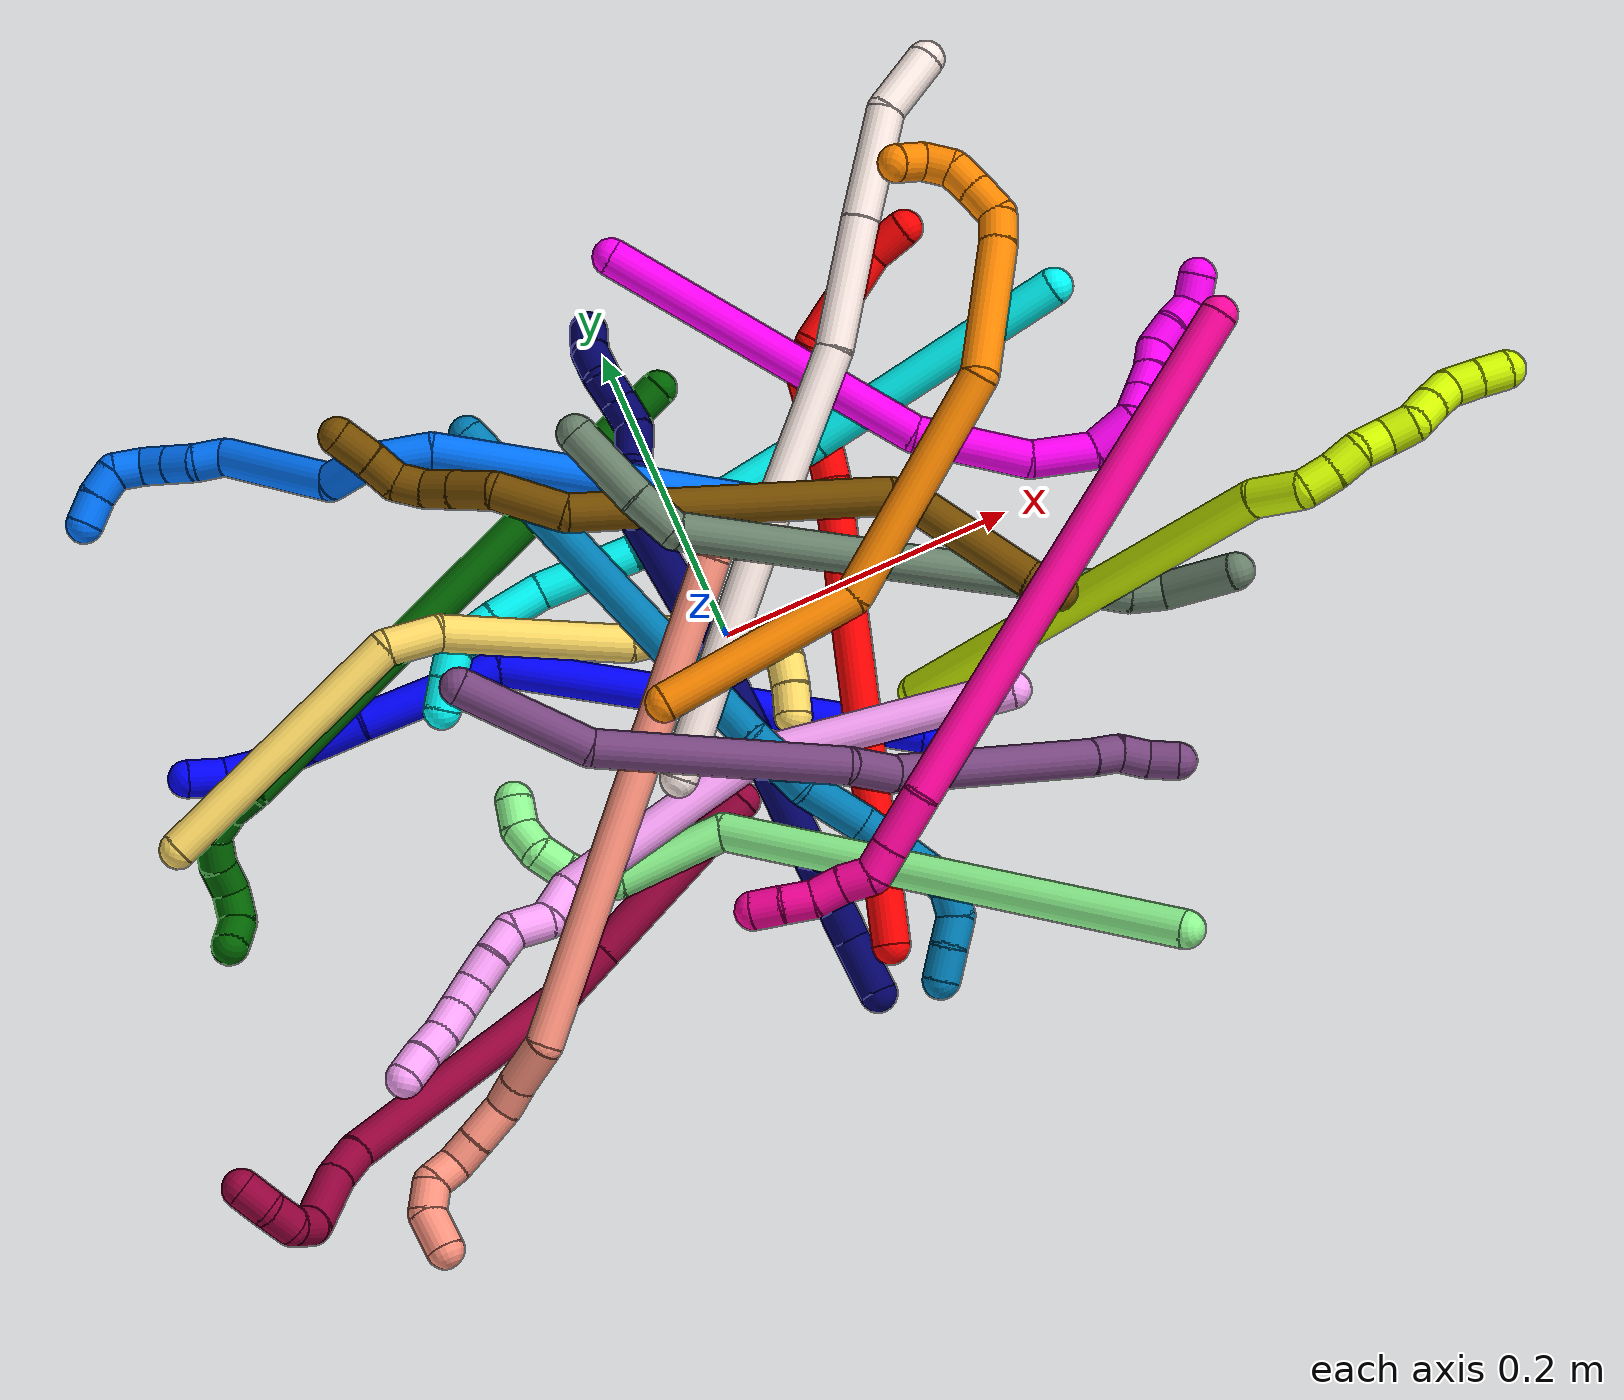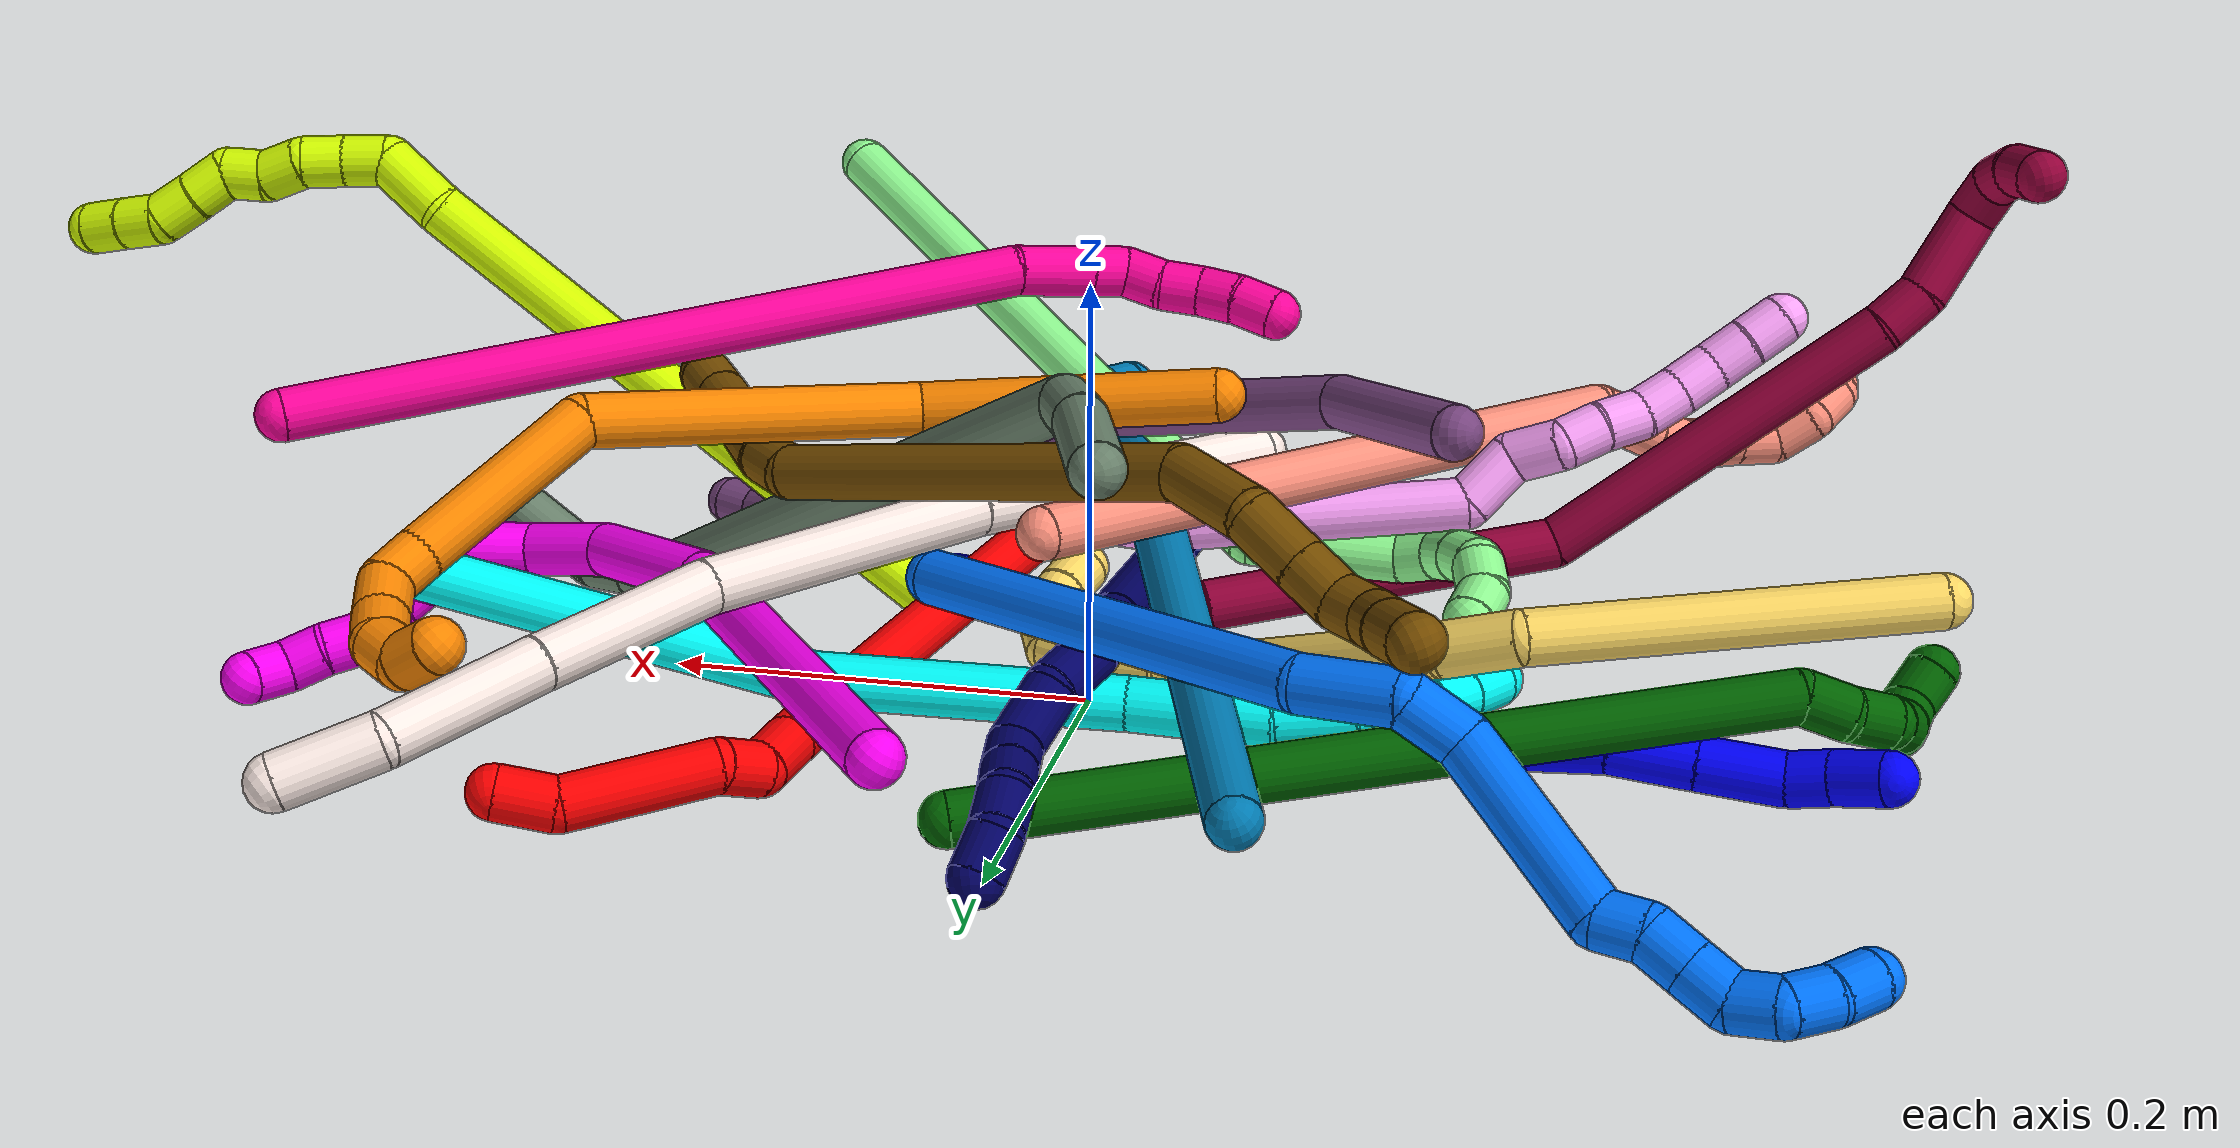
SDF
<sdf version="1.7">
 <world name="default">
  <plugin name="TubeGeneratorPlugin" filename="libtube_generator_plugin.so"/>
  <model name="photoneo_s_sensor">
   <static>1</static>
   <pose>0 0 2 1.57079 1.57079 3.14159</pose>
   <link name="link">
    <inertial><mass>0.1</mass></inertial>
    <sensor name="sensor" type="depth">
     <update_rate>30</update_rate>
     <camera>
      <horizontal_fov>1.22</horizontal_fov>
      <image><width>1920</width><height>1200</height><format>B8G8R8</format></image>
      <clip><near>0.1</near><far>4</far></clip>
      <depth_camera><output>points</output></depth_camera>
     </camera>
     <plugin name="camera_plugin" filename="libgazebo_ros_depth_camera.so">
      <baseline>0.2</baseline>
      <alwaysOn>1</alwaysOn>
      <updateRate>0.0</updateRate>
      <cameraName>camera_ir</cameraName>
      <imageTopicName>/camera/color/image_raw</imageTopicName>
      <cameraInfoTopicName>/camera/color/camera_info</cameraInfoTopicName>
      <depthImageTopicName>/camera/depth/image_raw</depthImageTopicName>
      <depthImageCameraInfoTopicName>/camera/depth/camera_info</depthImageCameraInfoTopicName>
      <pointCloudTopicName>/camera/depth/points</pointCloudTopicName>
      <frameName>fr_optical</frameName>
      <pointCloudCutoff>0.1</pointCloudCutoff>
      <pointCloudCutoffMax>2.0</pointCloudCutoffMax>
      <distortionK1>0</distortionK1>
      <distortionK2>0</distortionK2>
      <distortionK3>0</distortionK3>
      <distortionT1>0</distortionT1>
      <distortionT2>0</distortionT2>
      <CxPrime>0</CxPrime>
      <Cx>0</Cx>
      <Cy>0</Cy>
      <focalLength>0</focalLength>
      <hackBaseline>0</hackBaseline>
     </plugin>
    </sensor>
   </link>
  </model>
  <gravity>0 0 -9.8</gravity>
  <magnetic_field>6e-06 2.3e-05 -4.2e-05</magnetic_field>
  <atmosphere type="adiabatic"/>
  <physics name="default_physics" default="0" type="ode">
   <max_step_size>0.003</max_step_size>
   <real_time_factor>1</real_time_factor>
   <real_time_update_rate>1000</real_time_update_rate>
   <max_contacts>10000</max_contacts>
   <ode>
    <solver>
     <type>quick</type>
     <iters>100</iters>
     <sor>1.3</sor>
     <use_dynamic_moi_rescaling>0</use_dynamic_moi_rescaling>
    </solver>
    <constraints>
     <contact_max_correcting_vel>0</contact_max_correcting_vel>
     <contact_surface_layer>0.001</contact_surface_layer>
     <cfm>0</cfm>
     <erp>0.2</erp>
    </constraints>
   </ode>
  </physics>
  <scene><ambient>0.4 0.4 0.4 1</ambient><background>0.7 0.7 0.7 1</background><shadows>0</shadows></scene>
  <audio><device>default</device></audio>
  <spherical_coordinates>
   <surface_model>EARTH_WGS84</surface_model>
   <latitude_deg>0</latitude_deg>
   <longitude_deg>0</longitude_deg>
   <elevation>0</elevation>
   <heading_deg>0</heading_deg>
  </spherical_coordinates>
  <model name="bin">
   <static>1</static>
   <link name="bottom">
    <collision name="collision-bottom">
     <pose>0 0 -0.01 0 -0 0</pose>
     <geometry><box><size>0.8 0.6 0.02</size></box></geometry>
     <surface>
      <friction><ode><mu>100</mu><mu2>100</mu2></ode></friction>
      <contact><collide_bitmask>65535</collide_bitmask></contact>
     </surface>
    </collision>
   </link>
   <link name="west_wall">
    <collision name="collision-west_wall">
     <pose>-0.41 0 0.1 0 -0 0</pose>
     <geometry><box><size>0.02 0.6 0.2</size></box></geometry>
     <surface>
      <friction><ode><mu>100</mu><mu2>100</mu2></ode></friction>
      <contact><collide_bitmask>65535</collide_bitmask></contact>
     </surface>
    </collision>
   </link>
   <link name="east_wall">
    <collision name="collision-east_wall">
     <pose>0.41 0 0.1 0 -0 0</pose>
     <geometry><box><size>0.02 0.6 0.2</size></box></geometry>
     <surface>
      <friction><ode><mu>100</mu><mu2>100</mu2></ode></friction>
      <contact><collide_bitmask>65535</collide_bitmask></contact>
     </surface>
    </collision>
   </link>
   <link name="south_wall">
    <collision name="collision-south_wall">
     <pose>0 -0.31 0.1 0 -0 0</pose>
     <geometry><box><size>0.8 0.02 0.2</size></box></geometry>
     <surface>
      <friction><ode><mu>100</mu><mu2>100</mu2></ode></friction>
      <contact><collide_bitmask>65535</collide_bitmask></contact>
     </surface>
    </collision>
   </link>
   <link name="north_wall">
    <collision name="collision-north_wall">
     <pose>0 0.31 0.1 0 -0 0</pose>
     <geometry><box><size>0.8 0.02 0.2</size></box></geometry>
     <surface>
      <friction><ode><mu>100</mu><mu2>100</mu2></ode></friction>
      <contact><collide_bitmask>65535</collide_bitmask></contact>
     </surface>
    </collision>
   </link>
  </model>
  <model name="1">
   <static>0</static>
   <link name="1">
    <collision name="collision-cylinder-e_1_1_4">
     <pose>-0.089953 0.033095 -0.102638 -2.82968 -0.695203 2.32269</pose>
     <geometry><cylinder><radius>0.0125</radius><length>0.280866</length></cylinder></geometry>
     <surface>
      <friction><ode><mu>1.16</mu><mu2>1.16</mu2><slip1>0</slip1><slip2>0</slip2></ode></friction>
      <contact><ode><kp>1e+06</kp><kd>1</kd><max_vel>0</max_vel><min_depth>0.001</min_depth></ode></contact>
     </surface>
    </collision>
    <visual name="visual-cylinder-e_1_1_4">
     <pose>-0.089953 0.033095 -0.102638 -2.82968 -0.695203 2.32269</pose>
     <geometry><cylinder><radius>0.0125</radius><length>0.280866</length></cylinder></geometry>
     <material><ambient>0 0 1 1</ambient></material>
    </visual>
    <collision name="collision-cylinder-e_2_4_5">
     <pose>-0.217499 0.092152 -0.220171 -2.09164 -0.898374 1.38825</pose>
     <geometry><cylinder><radius>0.0125</radius><length>0.096107</length></cylinder></geometry>
     <surface>
      <friction><ode><mu>1.16</mu><mu2>1.16</mu2><slip1>0</slip1><slip2>0</slip2></ode></friction>
      <contact><ode><kp>1e+06</kp><kd>1</kd><max_vel>0</max_vel><min_depth>0.001</min_depth></ode></contact>
     </surface>
    </collision>
    <visual name="visual-cylinder-e_2_4_5">
     <pose>-0.217499 0.092152 -0.220171 -2.09164 -0.898374 1.38825</pose>
     <geometry><cylinder><radius>0.0125</radius><length>0.096107</length></cylinder></geometry>
     <material><ambient>0 0 1 1</ambient></material>
    </visual>
    <collision name="collision-cylinder-e_3_5_6">
     <pose>-0.272067 0.125997 -0.240055 -2.13517 -1.06829 1.64261</pose>
     <geometry><cylinder><radius>0.0125</radius><length>0.038739</length></cylinder></geometry>
     <surface>
      <friction><ode><mu>1.16</mu><mu2>1.16</mu2><slip1>0</slip1><slip2>0</slip2></ode></friction>
      <contact><ode><kp>1e+06</kp><kd>1</kd><max_vel>0</max_vel><min_depth>0.001</min_depth></ode></contact>
     </surface>
    </collision>
    <visual name="visual-cylinder-e_3_5_6">
     <pose>-0.272067 0.125997 -0.240055 -2.13517 -1.06829 1.64261</pose>
     <geometry><cylinder><radius>0.0125</radius><length>0.038739</length></cylinder></geometry>
     <material><ambient>0 0 1 1</ambient></material>
    </visual>
    <collision name="collision-cylinder-e_4_6_7">
     <pose>-0.306168 0.142029 -0.249932 -2.11099 -1.06421 1.60958</pose>
     <geometry><cylinder><radius>0.0125</radius><length>0.039171</length></cylinder></geometry>
     <surface>
      <friction><ode><mu>1.16</mu><mu2>1.16</mu2><slip1>0</slip1><slip2>0</slip2></ode></friction>
      <contact><ode><kp>1e+06</kp><kd>1</kd><max_vel>0</max_vel><min_depth>0.001</min_depth></ode></contact>
     </surface>
    </collision>
    <visual name="visual-cylinder-e_4_6_7">
     <pose>-0.306168 0.142029 -0.249932 -2.11099 -1.06421 1.60958</pose>
     <geometry><cylinder><radius>0.0125</radius><length>0.039171</length></cylinder></geometry>
     <material><ambient>0 0 1 1</ambient></material>
    </visual>
    <collision name="collision-cylinder-e_5_7_8">
     <pose>-0.330048 0.156191 -0.259514 -2.23375 -0.724807 1.32124</pose>
     <geometry><cylinder><radius>0.0125</radius><length>0.020378</length></cylinder></geometry>
     <surface>
      <friction><ode><mu>1.16</mu><mu2>1.16</mu2><slip1>0</slip1><slip2>0</slip2></ode></friction>
      <contact><ode><kp>1e+06</kp><kd>1</kd><max_vel>0</max_vel><min_depth>0.001</min_depth></ode></contact>
     </surface>
    </collision>
    <visual name="visual-cylinder-e_5_7_8">
     <pose>-0.330048 0.156191 -0.259514 -2.23375 -0.724807 1.32124</pose>
     <geometry><cylinder><radius>0.0125</radius><length>0.020378</length></cylinder></geometry>
     <material><ambient>0 0 1 1</ambient></material>
    </visual>
    <collision name="collision-cylinder-e_6_8_2">
     <pose>-0.344292 0.1685 -0.271777 -2.44764 -0.650235 1.50061</pose>
     <geometry><cylinder><radius>0.0125</radius><length>0.02474</length></cylinder></geometry>
     <surface>
      <friction><ode><mu>1.16</mu><mu2>1.16</mu2><slip1>0</slip1><slip2>0</slip2></ode></friction>
      <contact><ode><kp>1e+06</kp><kd>1</kd><max_vel>0</max_vel><min_depth>0.001</min_depth></ode></contact>
     </surface>
    </collision>
    <visual name="visual-cylinder-e_6_8_2">
     <pose>-0.344292 0.1685 -0.271777 -2.44764 -0.650235 1.50061</pose>
     <geometry><cylinder><radius>0.0125</radius><length>0.02474</length></cylinder></geometry>
     <material><ambient>0 0 1 1</ambient></material>
    </visual>
    <collision name="collision-sphere-2">
     <pose>-0.35178 0.174797 -0.279345 0 -0 0</pose>
     <geometry><sphere><radius>0.0125</radius></sphere></geometry>
     <surface>
      <friction><ode><mu>1.16</mu><mu2>1.16</mu2><slip1>0</slip1><slip2>0</slip2></ode></friction>
      <contact><ode><kp>1e+06</kp><kd>1</kd><max_vel>0</max_vel><min_depth>0.001</min_depth></ode></contact>
     </surface>
    </collision>
    <visual name="visual-sphere-2">
     <pose>-0.35178 0.174797 -0.279345 0 -0 0</pose>
     <geometry><sphere><radius>0.0125</radius></sphere></geometry>
     <material><ambient>0 0 1 1</ambient></material>
    </visual>
    <collision name="collision-sphere-4">
     <pose>-0.179906 0.06619 -0.205276 0 -0 0</pose>
     <geometry><sphere><radius>0.0125</radius></sphere></geometry>
     <surface>
      <friction><ode><mu>1.16</mu><mu2>1.16</mu2><slip1>0</slip1><slip2>0</slip2></ode></friction>
      <contact><ode><kp>1e+06</kp><kd>1</kd><max_vel>0</max_vel><min_depth>0.001</min_depth></ode></contact>
     </surface>
    </collision>
    <visual name="visual-sphere-4">
     <pose>-0.179906 0.06619 -0.205276 0 -0 0</pose>
     <geometry><sphere><radius>0.0125</radius></sphere></geometry>
     <material><ambient>0 0 1 1</ambient></material>
    </visual>
    <collision name="collision-sphere-1">
     <geometry><sphere><radius>0.0125</radius></sphere></geometry>
     <surface>
      <friction><ode><mu>1.16</mu><mu2>1.16</mu2><slip1>0</slip1><slip2>0</slip2></ode></friction>
      <contact><ode><kp>1e+06</kp><kd>1</kd><max_vel>0</max_vel><min_depth>0.001</min_depth></ode></contact>
     </surface>
    </collision>
    <visual name="visual-sphere-1">
     <geometry><sphere><radius>0.0125</radius></sphere></geometry>
     <material><ambient>0 0 1 1</ambient></material>
    </visual>
    <collision name="collision-sphere-8">
     <pose>-0.336803 0.162203 -0.264208 0 -0 0</pose>
     <geometry><sphere><radius>0.0125</radius></sphere></geometry>
     <surface>
      <friction><ode><mu>1.16</mu><mu2>1.16</mu2><slip1>0</slip1><slip2>0</slip2></ode></friction>
      <contact><ode><kp>1e+06</kp><kd>1</kd><max_vel>0</max_vel><min_depth>0.001</min_depth></ode></contact>
     </surface>
    </collision>
    <visual name="visual-sphere-8">
     <pose>-0.336803 0.162203 -0.264208 0 -0 0</pose>
     <geometry><sphere><radius>0.0125</radius></sphere></geometry>
     <material><ambient>0 0 1 1</ambient></material>
    </visual>
    <collision name="collision-sphere-5">
     <pose>-0.255092 0.118115 -0.235065 0 -0 0</pose>
     <geometry><sphere><radius>0.0125</radius></sphere></geometry>
     <surface>
      <friction><ode><mu>1.16</mu><mu2>1.16</mu2><slip1>0</slip1><slip2>0</slip2></ode></friction>
      <contact><ode><kp>1e+06</kp><kd>1</kd><max_vel>0</max_vel><min_depth>0.001</min_depth></ode></contact>
     </surface>
    </collision>
    <visual name="visual-sphere-5">
     <pose>-0.255092 0.118115 -0.235065 0 -0 0</pose>
     <geometry><sphere><radius>0.0125</radius></sphere></geometry>
     <material><ambient>0 0 1 1</ambient></material>
    </visual>
    <collision name="collision-sphere-6">
     <pose>-0.289042 0.133879 -0.245045 0 -0 0</pose>
     <geometry><sphere><radius>0.0125</radius></sphere></geometry>
     <surface>
      <friction><ode><mu>1.16</mu><mu2>1.16</mu2><slip1>0</slip1><slip2>0</slip2></ode></friction>
      <contact><ode><kp>1e+06</kp><kd>1</kd><max_vel>0</max_vel><min_depth>0.001</min_depth></ode></contact>
     </surface>
    </collision>
    <visual name="visual-sphere-6">
     <pose>-0.289042 0.133879 -0.245045 0 -0 0</pose>
     <geometry><sphere><radius>0.0125</radius></sphere></geometry>
     <material><ambient>0 0 1 1</ambient></material>
    </visual>
    <collision name="collision-sphere-7">
     <pose>-0.323293 0.150179 -0.254819 0 -0 0</pose>
     <geometry><sphere><radius>0.0125</radius></sphere></geometry>
     <surface>
      <friction><ode><mu>1.16</mu><mu2>1.16</mu2><slip1>0</slip1><slip2>0</slip2></ode></friction>
      <contact><ode><kp>1e+06</kp><kd>1</kd><max_vel>0</max_vel><min_depth>0.001</min_depth></ode></contact>
     </surface>
    </collision>
    <visual name="visual-sphere-7">
     <pose>-0.323293 0.150179 -0.254819 0 -0 0</pose>
     <geometry><sphere><radius>0.0125</radius></sphere></geometry>
     <material><ambient>0 0 1 1</ambient></material>
    </visual>
    <inertial>
     <pose>-0.167887 0.071895 -0.162178 0 -0 0</pose>
     <mass>0.5</mass>
     <inertia>
      <ixx>0.000106</ixx>
      <ixy>0</ixy>
      <ixz>0</ixz>
      <iyy>0.002642</iyy>
      <iyz>0</iyz>
      <izz>0.000755</izz>
     </inertia>
    </inertial>
   </link>
   <pose>0.091762 -0.111055 0.012077 1.858 -0.58859 0.115646</pose>
  </model>
  <model name="2">
   <static>0</static>
   <link name="2">
    <collision name="collision-cylinder-e_1_1_4">
     <pose>0.031861 0.079482 -0.128216 -2.58666 0.208144 -0.703006</pose>
     <geometry><cylinder><radius>0.0125</radius><length>0.308362</length></cylinder></geometry>
     <surface>
      <friction><ode><mu>1.16</mu><mu2>1.16</mu2><slip1>0</slip1><slip2>0</slip2></ode></friction>
      <contact><ode><kp>1e+06</kp><kd>1</kd><max_vel>0</max_vel><min_depth>0.001</min_depth></ode></contact>
     </surface>
    </collision>
    <visual name="visual-cylinder-e_1_1_4">
     <pose>0.031861 0.079482 -0.128216 -2.58666 0.208144 -0.703006</pose>
     <geometry><cylinder><radius>0.0125</radius><length>0.308362</length></cylinder></geometry>
     <material><ambient>1 0 0 1</ambient></material>
    </visual>
    <collision name="collision-cylinder-e_2_4_5">
     <pose>0.065648 0.169476 -0.274517 -2.61505 0.091858 -0.337799</pose>
     <geometry><cylinder><radius>0.0125</radius><length>0.042014</length></cylinder></geometry>
     <surface>
      <friction><ode><mu>1.16</mu><mu2>1.16</mu2><slip1>0</slip1><slip2>0</slip2></ode></friction>
      <contact><ode><kp>1e+06</kp><kd>1</kd><max_vel>0</max_vel><min_depth>0.001</min_depth></ode></contact>
     </surface>
    </collision>
    <visual name="visual-cylinder-e_2_4_5">
     <pose>0.065648 0.169476 -0.274517 -2.61505 0.091858 -0.337799</pose>
     <geometry><cylinder><radius>0.0125</radius><length>0.042014</length></cylinder></geometry>
     <material><ambient>1 0 0 1</ambient></material>
    </visual>
    <collision name="collision-cylinder-e_3_5_6">
     <pose>0.068086 0.187019 -0.305416 -2.63981 0.034945 -0.136154</pose>
     <geometry><cylinder><radius>0.0125</radius><length>0.029249</length></cylinder></geometry>
     <surface>
      <friction><ode><mu>1.16</mu><mu2>1.16</mu2><slip1>0</slip1><slip2>0</slip2></ode></friction>
      <contact><ode><kp>1e+06</kp><kd>1</kd><max_vel>0</max_vel><min_depth>0.001</min_depth></ode></contact>
     </surface>
    </collision>
    <visual name="visual-cylinder-e_3_5_6">
     <pose>0.068086 0.187019 -0.305416 -2.63981 0.034945 -0.136154</pose>
     <geometry><cylinder><radius>0.0125</radius><length>0.029249</length></cylinder></geometry>
     <material><ambient>1 0 0 1</ambient></material>
    </visual>
    <collision name="collision-cylinder-e_4_6_7">
     <pose>0.069934 0.204233 -0.322584 -1.97481 0.120145 -0.181749</pose>
     <geometry><cylinder><radius>0.0125</radius><length>0.022312</length></cylinder></geometry>
     <surface>
      <friction><ode><mu>1.16</mu><mu2>1.16</mu2><slip1>0</slip1><slip2>0</slip2></ode></friction>
      <contact><ode><kp>1e+06</kp><kd>1</kd><max_vel>0</max_vel><min_depth>0.001</min_depth></ode></contact>
     </surface>
    </collision>
    <visual name="visual-cylinder-e_4_6_7">
     <pose>0.069934 0.204233 -0.322584 -1.97481 0.120145 -0.181749</pose>
     <geometry><cylinder><radius>0.0125</radius><length>0.022312</length></cylinder></geometry>
     <material><ambient>1 0 0 1</ambient></material>
    </visual>
    <collision name="collision-cylinder-e_5_7_8">
     <pose>0.092484 0.240317 -0.338347 -1.98571 0.64318 -0.94449</pose>
     <geometry><cylinder><radius>0.0125</radius><length>0.070738</length></cylinder></geometry>
     <surface>
      <friction><ode><mu>1.16</mu><mu2>1.16</mu2><slip1>0</slip1><slip2>0</slip2></ode></friction>
      <contact><ode><kp>1e+06</kp><kd>1</kd><max_vel>0</max_vel><min_depth>0.001</min_depth></ode></contact>
     </surface>
    </collision>
    <visual name="visual-cylinder-e_5_7_8">
     <pose>0.092484 0.240317 -0.338347 -1.98571 0.64318 -0.94449</pose>
     <geometry><cylinder><radius>0.0125</radius><length>0.070738</length></cylinder></geometry>
     <material><ambient>1 0 0 1</ambient></material>
    </visual>
    <collision name="collision-cylinder-e_6_8_2">
     <pose>0.120108 0.278213 -0.348464 -1.46357 0.488544 -0.440458</pose>
     <geometry><cylinder><radius>0.0125</radius><length>0.027325</length></cylinder></geometry>
     <surface>
      <friction><ode><mu>1.16</mu><mu2>1.16</mu2><slip1>0</slip1><slip2>0</slip2></ode></friction>
      <contact><ode><kp>1e+06</kp><kd>1</kd><max_vel>0</max_vel><min_depth>0.001</min_depth></ode></contact>
     </surface>
    </collision>
    <visual name="visual-cylinder-e_6_8_2">
     <pose>0.120108 0.278213 -0.348464 -1.46357 0.488544 -0.440458</pose>
     <geometry><cylinder><radius>0.0125</radius><length>0.027325</length></cylinder></geometry>
     <material><ambient>1 0 0 1</ambient></material>
    </visual>
    <collision name="collision-sphere-2">
     <pose>0.126521 0.290207 -0.347173 0 -0 0</pose>
     <geometry><sphere><radius>0.0125</radius></sphere></geometry>
     <surface>
      <friction><ode><mu>1.16</mu><mu2>1.16</mu2><slip1>0</slip1><slip2>0</slip2></ode></friction>
      <contact><ode><kp>1e+06</kp><kd>1</kd><max_vel>0</max_vel><min_depth>0.001</min_depth></ode></contact>
     </surface>
    </collision>
    <visual name="visual-sphere-2">
     <pose>0.126521 0.290207 -0.347173 0 -0 0</pose>
     <geometry><sphere><radius>0.0125</radius></sphere></geometry>
     <material><ambient>1 0 0 1</ambient></material>
    </visual>
    <collision name="collision-sphere-4">
     <pose>0.063721 0.158964 -0.256432 0 -0 0</pose>
     <geometry><sphere><radius>0.0125</radius></sphere></geometry>
     <surface>
      <friction><ode><mu>1.16</mu><mu2>1.16</mu2><slip1>0</slip1><slip2>0</slip2></ode></friction>
      <contact><ode><kp>1e+06</kp><kd>1</kd><max_vel>0</max_vel><min_depth>0.001</min_depth></ode></contact>
     </surface>
    </collision>
    <visual name="visual-sphere-4">
     <pose>0.063721 0.158964 -0.256432 0 -0 0</pose>
     <geometry><sphere><radius>0.0125</radius></sphere></geometry>
     <material><ambient>1 0 0 1</ambient></material>
    </visual>
    <collision name="collision-sphere-1">
     <geometry><sphere><radius>0.0125</radius></sphere></geometry>
     <surface>
      <friction><ode><mu>1.16</mu><mu2>1.16</mu2><slip1>0</slip1><slip2>0</slip2></ode></friction>
      <contact><ode><kp>1e+06</kp><kd>1</kd><max_vel>0</max_vel><min_depth>0.001</min_depth></ode></contact>
     </surface>
    </collision>
    <visual name="visual-sphere-1">
     <geometry><sphere><radius>0.0125</radius></sphere></geometry>
     <material><ambient>1 0 0 1</ambient></material>
    </visual>
    <collision name="collision-sphere-8">
     <pose>0.113696 0.266218 -0.349755 0 -0 0</pose>
     <geometry><sphere><radius>0.0125</radius></sphere></geometry>
     <surface>
      <friction><ode><mu>1.16</mu><mu2>1.16</mu2><slip1>0</slip1><slip2>0</slip2></ode></friction>
      <contact><ode><kp>1e+06</kp><kd>1</kd><max_vel>0</max_vel><min_depth>0.001</min_depth></ode></contact>
     </surface>
    </collision>
    <visual name="visual-sphere-8">
     <pose>0.113696 0.266218 -0.349755 0 -0 0</pose>
     <geometry><sphere><radius>0.0125</radius></sphere></geometry>
     <material><ambient>1 0 0 1</ambient></material>
    </visual>
    <collision name="collision-sphere-5">
     <pose>0.067575 0.179989 -0.292602 0 -0 0</pose>
     <geometry><sphere><radius>0.0125</radius></sphere></geometry>
     <surface>
      <friction><ode><mu>1.16</mu><mu2>1.16</mu2><slip1>0</slip1><slip2>0</slip2></ode></friction>
      <contact><ode><kp>1e+06</kp><kd>1</kd><max_vel>0</max_vel><min_depth>0.001</min_depth></ode></contact>
     </surface>
    </collision>
    <visual name="visual-sphere-5">
     <pose>0.067575 0.179989 -0.292602 0 -0 0</pose>
     <geometry><sphere><radius>0.0125</radius></sphere></geometry>
     <material><ambient>1 0 0 1</ambient></material>
    </visual>
    <collision name="collision-sphere-6">
     <pose>0.068597 0.194049 -0.31823 0 -0 0</pose>
     <geometry><sphere><radius>0.0125</radius></sphere></geometry>
     <surface>
      <friction><ode><mu>1.16</mu><mu2>1.16</mu2><slip1>0</slip1><slip2>0</slip2></ode></friction>
      <contact><ode><kp>1e+06</kp><kd>1</kd><max_vel>0</max_vel><min_depth>0.001</min_depth></ode></contact>
     </surface>
    </collision>
    <visual name="visual-sphere-6">
     <pose>0.068597 0.194049 -0.31823 0 -0 0</pose>
     <geometry><sphere><radius>0.0125</radius></sphere></geometry>
     <material><ambient>1 0 0 1</ambient></material>
    </visual>
    <collision name="collision-sphere-7">
     <pose>0.071271 0.214416 -0.326938 0 -0 0</pose>
     <geometry><sphere><radius>0.0125</radius></sphere></geometry>
     <surface>
      <friction><ode><mu>1.16</mu><mu2>1.16</mu2><slip1>0</slip1><slip2>0</slip2></ode></friction>
      <contact><ode><kp>1e+06</kp><kd>1</kd><max_vel>0</max_vel><min_depth>0.001</min_depth></ode></contact>
     </surface>
    </collision>
    <visual name="visual-sphere-7">
     <pose>0.071271 0.214416 -0.326938 0 -0 0</pose>
     <geometry><sphere><radius>0.0125</radius></sphere></geometry>
     <material><ambient>1 0 0 1</ambient></material>
    </visual>
    <inertial>
     <pose>0.051917 0.132516 -0.201314 0 -0 0</pose>
     <mass>0.5</mass>
     <inertia>
      <ixx>0.000294</ixx>
      <ixy>0</ixy>
      <ixz>0</ixz>
      <iyy>-0.002977</iyy>
      <iyz>0</iyz>
      <izz>-0.001855</izz>
     </inertia>
    </inertial>
   </link>
   <pose>0.016191 -0.227602 0.054486 1.05165 0.807233 -0.120804</pose>
  </model>
  <model name="3">
   <static>0</static>
   <link name="3">
    <collision name="collision-cylinder-e_1_1_4">
     <pose>-0.07893 -0.010625 -0.047513 2.9216 -1.01809 -2.75086</pose>
     <geometry><cylinder><radius>0.0125</radius><length>0.185475</length></cylinder></geometry>
     <surface>
      <friction><ode><mu>1.16</mu><mu2>1.16</mu2><slip1>0</slip1><slip2>0</slip2></ode></friction>
      <contact><ode><kp>1e+06</kp><kd>1</kd><max_vel>0</max_vel><min_depth>0.001</min_depth></ode></contact>
     </surface>
    </collision>
    <visual name="visual-cylinder-e_1_1_4">
     <pose>-0.07893 -0.010625 -0.047513 2.9216 -1.01809 -2.75086</pose>
     <geometry><cylinder><radius>0.0125</radius><length>0.185475</length></cylinder></geometry>
     <material><ambient>0.003922 1 0.996078 1</ambient></material>
    </visual>
    <collision name="collision-cylinder-e_2_4_5">
     <pose>-0.218143 -0.042217 -0.124054 2.51603 -1.0348 -2.10811</pose>
     <geometry><cylinder><radius>0.0125</radius><length>0.140234</length></cylinder></geometry>
     <surface>
      <friction><ode><mu>1.16</mu><mu2>1.16</mu2><slip1>0</slip1><slip2>0</slip2></ode></friction>
      <contact><ode><kp>1e+06</kp><kd>1</kd><max_vel>0</max_vel><min_depth>0.001</min_depth></ode></contact>
     </surface>
    </collision>
    <visual name="visual-cylinder-e_2_4_5">
     <pose>-0.218143 -0.042217 -0.124054 2.51603 -1.0348 -2.10811</pose>
     <geometry><cylinder><radius>0.0125</radius><length>0.140234</length></cylinder></geometry>
     <material><ambient>0.003922 1 0.996078 1</ambient></material>
    </visual>
    <collision name="collision-cylinder-e_3_5_6">
     <pose>-0.308805 -0.071844 -0.161922 2.36656 -1.18395 -2.0505</pose>
     <geometry><cylinder><radius>0.0125</radius><length>0.065603</length></cylinder></geometry>
     <surface>
      <friction><ode><mu>1.16</mu><mu2>1.16</mu2><slip1>0</slip1><slip2>0</slip2></ode></friction>
      <contact><ode><kp>1e+06</kp><kd>1</kd><max_vel>0</max_vel><min_depth>0.001</min_depth></ode></contact>
     </surface>
    </collision>
    <visual name="visual-cylinder-e_3_5_6">
     <pose>-0.308805 -0.071844 -0.161922 2.36656 -1.18395 -2.0505</pose>
     <geometry><cylinder><radius>0.0125</radius><length>0.065603</length></cylinder></geometry>
     <material><ambient>0.003922 1 0.996078 1</ambient></material>
    </visual>
    <collision name="collision-cylinder-e_4_6_7">
     <pose>-0.354097 -0.088186 -0.176738 2.23187 -0.992611 -1.6725</pose>
     <geometry><cylinder><radius>0.0125</radius><length>0.035617</length></cylinder></geometry>
     <surface>
      <friction><ode><mu>1.16</mu><mu2>1.16</mu2><slip1>0</slip1><slip2>0</slip2></ode></friction>
      <contact><ode><kp>1e+06</kp><kd>1</kd><max_vel>0</max_vel><min_depth>0.001</min_depth></ode></contact>
     </surface>
    </collision>
    <visual name="visual-cylinder-e_4_6_7">
     <pose>-0.354097 -0.088186 -0.176738 2.23187 -0.992611 -1.6725</pose>
     <geometry><cylinder><radius>0.0125</radius><length>0.035617</length></cylinder></geometry>
     <material><ambient>0.003922 1 0.996078 1</ambient></material>
    </visual>
    <collision name="collision-cylinder-e_5_7_8">
     <pose>-0.381291 -0.103823 -0.188708 2.21655 -0.889319 -1.52546</pose>
     <geometry><cylinder><radius>0.0125</radius><length>0.031625</length></cylinder></geometry>
     <surface>
      <friction><ode><mu>1.16</mu><mu2>1.16</mu2><slip1>0</slip1><slip2>0</slip2></ode></friction>
      <contact><ode><kp>1e+06</kp><kd>1</kd><max_vel>0</max_vel><min_depth>0.001</min_depth></ode></contact>
     </surface>
    </collision>
    <visual name="visual-cylinder-e_5_7_8">
     <pose>-0.381291 -0.103823 -0.188708 2.21655 -0.889319 -1.52546</pose>
     <geometry><cylinder><radius>0.0125</radius><length>0.031625</length></cylinder></geometry>
     <material><ambient>0.003922 1 0.996078 1</ambient></material>
    </visual>
    <collision name="collision-cylinder-e_6_8_9">
     <pose>-0.395968 -0.116784 -0.20327 2.61283 -0.236929 -0.828433</pose>
     <geometry><cylinder><radius>0.0125</radius><length>0.020415</length></cylinder></geometry>
     <surface>
      <friction><ode><mu>1.16</mu><mu2>1.16</mu2><slip1>0</slip1><slip2>0</slip2></ode></friction>
      <contact><ode><kp>1e+06</kp><kd>1</kd><max_vel>0</max_vel><min_depth>0.001</min_depth></ode></contact>
     </surface>
    </collision>
    <visual name="visual-cylinder-e_6_8_9">
     <pose>-0.395968 -0.116784 -0.20327 2.61283 -0.236929 -0.828433</pose>
     <geometry><cylinder><radius>0.0125</radius><length>0.020415</length></cylinder></geometry>
     <material><ambient>0.003922 1 0.996078 1</ambient></material>
    </visual>
    <collision name="collision-cylinder-e_7_9_2">
     <pose>-0.400466 -0.127248 -0.220575 2.58323 -0.20129 -0.677397</pose>
     <geometry><cylinder><radius>0.0125</radius><length>0.02103</length></cylinder></geometry>
     <surface>
      <friction><ode><mu>1.16</mu><mu2>1.16</mu2><slip1>0</slip1><slip2>0</slip2></ode></friction>
      <contact><ode><kp>1e+06</kp><kd>1</kd><max_vel>0</max_vel><min_depth>0.001</min_depth></ode></contact>
     </surface>
    </collision>
    <visual name="visual-cylinder-e_7_9_2">
     <pose>-0.400466 -0.127248 -0.220575 2.58323 -0.20129 -0.677397</pose>
     <geometry><cylinder><radius>0.0125</radius><length>0.02103</length></cylinder></geometry>
     <material><ambient>0.003922 1 0.996078 1</ambient></material>
    </visual>
    <collision name="collision-sphere-2">
     <pose>-0.402569 -0.132706 -0.229313 0 -0 0</pose>
     <geometry><sphere><radius>0.0125</radius></sphere></geometry>
     <surface>
      <friction><ode><mu>1.16</mu><mu2>1.16</mu2><slip1>0</slip1><slip2>0</slip2></ode></friction>
      <contact><ode><kp>1e+06</kp><kd>1</kd><max_vel>0</max_vel><min_depth>0.001</min_depth></ode></contact>
     </surface>
    </collision>
    <visual name="visual-sphere-2">
     <pose>-0.402569 -0.132706 -0.229313 0 -0 0</pose>
     <geometry><sphere><radius>0.0125</radius></sphere></geometry>
     <material><ambient>0.003922 1 0.996078 1</ambient></material>
    </visual>
    <collision name="collision-sphere-9">
     <pose>-0.398364 -0.121789 -0.211837 0 -0 0</pose>
     <geometry><sphere><radius>0.0125</radius></sphere></geometry>
     <surface>
      <friction><ode><mu>1.16</mu><mu2>1.16</mu2><slip1>0</slip1><slip2>0</slip2></ode></friction>
      <contact><ode><kp>1e+06</kp><kd>1</kd><max_vel>0</max_vel><min_depth>0.001</min_depth></ode></contact>
     </surface>
    </collision>
    <visual name="visual-sphere-9">
     <pose>-0.398364 -0.121789 -0.211837 0 -0 0</pose>
     <geometry><sphere><radius>0.0125</radius></sphere></geometry>
     <material><ambient>0.003922 1 0.996078 1</ambient></material>
    </visual>
    <collision name="collision-sphere-4">
     <pose>-0.157859 -0.021249 -0.095026 0 -0 0</pose>
     <geometry><sphere><radius>0.0125</radius></sphere></geometry>
     <surface>
      <friction><ode><mu>1.16</mu><mu2>1.16</mu2><slip1>0</slip1><slip2>0</slip2></ode></friction>
      <contact><ode><kp>1e+06</kp><kd>1</kd><max_vel>0</max_vel><min_depth>0.001</min_depth></ode></contact>
     </surface>
    </collision>
    <visual name="visual-sphere-4">
     <pose>-0.157859 -0.021249 -0.095026 0 -0 0</pose>
     <geometry><sphere><radius>0.0125</radius></sphere></geometry>
     <material><ambient>0.003922 1 0.996078 1</ambient></material>
    </visual>
    <collision name="collision-sphere-1">
     <geometry><sphere><radius>0.0125</radius></sphere></geometry>
     <surface>
      <friction><ode><mu>1.16</mu><mu2>1.16</mu2><slip1>0</slip1><slip2>0</slip2></ode></friction>
      <contact><ode><kp>1e+06</kp><kd>1</kd><max_vel>0</max_vel><min_depth>0.001</min_depth></ode></contact>
     </surface>
    </collision>
    <visual name="visual-sphere-1">
     <geometry><sphere><radius>0.0125</radius></sphere></geometry>
     <material><ambient>0.003922 1 0.996078 1</ambient></material>
    </visual>
    <collision name="collision-sphere-8">
     <pose>-0.393572 -0.111779 -0.194703 0 -0 0</pose>
     <geometry><sphere><radius>0.0125</radius></sphere></geometry>
     <surface>
      <friction><ode><mu>1.16</mu><mu2>1.16</mu2><slip1>0</slip1><slip2>0</slip2></ode></friction>
      <contact><ode><kp>1e+06</kp><kd>1</kd><max_vel>0</max_vel><min_depth>0.001</min_depth></ode></contact>
     </surface>
    </collision>
    <visual name="visual-sphere-8">
     <pose>-0.393572 -0.111779 -0.194703 0 -0 0</pose>
     <geometry><sphere><radius>0.0125</radius></sphere></geometry>
     <material><ambient>0.003922 1 0.996078 1</ambient></material>
    </visual>
    <collision name="collision-sphere-5">
     <pose>-0.278427 -0.063185 -0.153081 0 -0 0</pose>
     <geometry><sphere><radius>0.0125</radius></sphere></geometry>
     <surface>
      <friction><ode><mu>1.16</mu><mu2>1.16</mu2><slip1>0</slip1><slip2>0</slip2></ode></friction>
      <contact><ode><kp>1e+06</kp><kd>1</kd><max_vel>0</max_vel><min_depth>0.001</min_depth></ode></contact>
     </surface>
    </collision>
    <visual name="visual-sphere-5">
     <pose>-0.278427 -0.063185 -0.153081 0 -0 0</pose>
     <geometry><sphere><radius>0.0125</radius></sphere></geometry>
     <material><ambient>0.003922 1 0.996078 1</ambient></material>
    </visual>
    <collision name="collision-sphere-6">
     <pose>-0.339183 -0.080504 -0.170763 0 -0 0</pose>
     <geometry><sphere><radius>0.0125</radius></sphere></geometry>
     <surface>
      <friction><ode><mu>1.16</mu><mu2>1.16</mu2><slip1>0</slip1><slip2>0</slip2></ode></friction>
      <contact><ode><kp>1e+06</kp><kd>1</kd><max_vel>0</max_vel><min_depth>0.001</min_depth></ode></contact>
     </surface>
    </collision>
    <visual name="visual-sphere-6">
     <pose>-0.339183 -0.080504 -0.170763 0 -0 0</pose>
     <geometry><sphere><radius>0.0125</radius></sphere></geometry>
     <material><ambient>0.003922 1 0.996078 1</ambient></material>
    </visual>
    <collision name="collision-sphere-7">
     <pose>-0.369011 -0.095868 -0.182714 0 -0 0</pose>
     <geometry><sphere><radius>0.0125</radius></sphere></geometry>
     <surface>
      <friction><ode><mu>1.16</mu><mu2>1.16</mu2><slip1>0</slip1><slip2>0</slip2></ode></friction>
      <contact><ode><kp>1e+06</kp><kd>1</kd><max_vel>0</max_vel><min_depth>0.001</min_depth></ode></contact>
     </surface>
    </collision>
    <visual name="visual-sphere-7">
     <pose>-0.369011 -0.095868 -0.182714 0 -0 0</pose>
     <geometry><sphere><radius>0.0125</radius></sphere></geometry>
     <material><ambient>0.003922 1 0.996078 1</ambient></material>
    </visual>
    <inertial>
     <pose>-0.21333 -0.048177 -0.115766 0 -0 0</pose>
     <mass>0.5</mass>
     <inertia>
      <ixx>-0.000584</ixx>
      <ixy>0</ixy>
      <ixz>0</ixz>
      <iyy>0.000514</iyy>
      <iyz>0</iyz>
      <izz>0.00082</izz>
     </inertia>
    </inertial>
   </link>
   <pose>0.282708 0.118243 0.084535 -1.06201 -0.119739 -0.39834</pose>
  </model>
  <model name="4">
   <static>0</static>
   <link name="4">
    <collision name="collision-cylinder-e_1_1_4">
     <pose>-0.076758 0.009958 -0.037444 -2.88166 -1.10333 2.72304</pose>
     <geometry><cylinder><radius>0.0125</radius><length>0.171966</length></cylinder></geometry>
     <surface>
      <friction><ode><mu>1.16</mu><mu2>1.16</mu2><slip1>0</slip1><slip2>0</slip2></ode></friction>
      <contact><ode><kp>1e+06</kp><kd>1</kd><max_vel>0</max_vel><min_depth>0.001</min_depth></ode></contact>
     </surface>
    </collision>
    <visual name="visual-cylinder-e_1_1_4">
     <pose>-0.076758 0.009958 -0.037444 -2.88166 -1.10333 2.72304</pose>
     <geometry><cylinder><radius>0.0125</radius><length>0.171966</length></cylinder></geometry>
     <material><ambient>1 0.65098 0.996078 1</ambient></material>
    </visual>
    <collision name="collision-cylinder-e_2_4_5">
     <pose>-0.203613 0.02215 -0.128858 -3.10024 -0.747765 3.03627</pose>
     <geometry><cylinder><radius>0.0125</radius><length>0.147341</length></cylinder></geometry>
     <surface>
      <friction><ode><mu>1.16</mu><mu2>1.16</mu2><slip1>0</slip1><slip2>0</slip2></ode></friction>
      <contact><ode><kp>1e+06</kp><kd>1</kd><max_vel>0</max_vel><min_depth>0.001</min_depth></ode></contact>
     </surface>
    </collision>
    <visual name="visual-cylinder-e_2_4_5">
     <pose>-0.203613 0.02215 -0.128858 -3.10024 -0.747765 3.03627</pose>
     <geometry><cylinder><radius>0.0125</radius><length>0.147341</length></cylinder></geometry>
     <material><ambient>1 0.65098 0.996078 1</ambient></material>
    </visual>
    <collision name="collision-cylinder-e_3_5_6">
     <pose>-0.258124 0.015868 -0.194791 2.52301 -0.292076 -0.86276</pose>
     <geometry><cylinder><radius>0.0125</radius><length>0.030665</length></cylinder></geometry>
     <surface>
      <friction><ode><mu>1.16</mu><mu2>1.16</mu2><slip1>0</slip1><slip2>0</slip2></ode></friction>
      <contact><ode><kp>1e+06</kp><kd>1</kd><max_vel>0</max_vel><min_depth>0.001</min_depth></ode></contact>
     </surface>
    </collision>
    <visual name="visual-cylinder-e_3_5_6">
     <pose>-0.258124 0.015868 -0.194791 2.52301 -0.292076 -0.86276</pose>
     <geometry><cylinder><radius>0.0125</radius><length>0.030665</length></cylinder></geometry>
     <material><ambient>1 0.65098 0.996078 1</ambient></material>
    </visual>
    <collision name="collision-cylinder-e_4_6_7">
     <pose>-0.273324 0.003867 -0.212944 2.62869 -0.988267 -2.23558</pose>
     <geometry><cylinder><radius>0.0125</radius><length>0.025831</length></cylinder></geometry>
     <surface>
      <friction><ode><mu>1.16</mu><mu2>1.16</mu2><slip1>0</slip1><slip2>0</slip2></ode></friction>
      <contact><ode><kp>1e+06</kp><kd>1</kd><max_vel>0</max_vel><min_depth>0.001</min_depth></ode></contact>
     </surface>
    </collision>
    <visual name="visual-cylinder-e_4_6_7">
     <pose>-0.273324 0.003867 -0.212944 2.62869 -0.988267 -2.23558</pose>
     <geometry><cylinder><radius>0.0125</radius><length>0.025831</length></cylinder></geometry>
     <material><ambient>1 0.65098 0.996078 1</ambient></material>
    </visual>
    <collision name="collision-cylinder-e_5_7_8">
     <pose>-0.288219 -0.001769 -0.228152 2.90764 -0.417282 -2.12821</pose>
     <geometry><cylinder><radius>0.0125</radius><length>0.02028</length></cylinder></geometry>
     <surface>
      <friction><ode><mu>1.16</mu><mu2>1.16</mu2><slip1>0</slip1><slip2>0</slip2></ode></friction>
      <contact><ode><kp>1e+06</kp><kd>1</kd><max_vel>0</max_vel><min_depth>0.001</min_depth></ode></contact>
     </surface>
    </collision>
    <visual name="visual-cylinder-e_5_7_8">
     <pose>-0.288219 -0.001769 -0.228152 2.90764 -0.417282 -2.12821</pose>
     <geometry><cylinder><radius>0.0125</radius><length>0.02028</length></cylinder></geometry>
     <material><ambient>1 0.65098 0.996078 1</ambient></material>
    </visual>
    <collision name="collision-cylinder-e_6_8_9">
     <pose>-0.29633 -0.004602 -0.247085 3.07268 -0.38276 -2.78944</pose>
     <geometry><cylinder><radius>0.0125</radius><length>0.021429</length></cylinder></geometry>
     <surface>
      <friction><ode><mu>1.16</mu><mu2>1.16</mu2><slip1>0</slip1><slip2>0</slip2></ode></friction>
      <contact><ode><kp>1e+06</kp><kd>1</kd><max_vel>0</max_vel><min_depth>0.001</min_depth></ode></contact>
     </surface>
    </collision>
    <visual name="visual-cylinder-e_6_8_9">
     <pose>-0.29633 -0.004602 -0.247085 3.07268 -0.38276 -2.78944</pose>
     <geometry><cylinder><radius>0.0125</radius><length>0.021429</length></cylinder></geometry>
     <material><ambient>1 0.65098 0.996078 1</ambient></material>
    </visual>
    <collision name="collision-cylinder-e_7_9_10">
     <pose>-0.303759 -0.008525 -0.266349 2.80812 -0.333508 -1.57091</pose>
     <geometry><cylinder><radius>0.0125</radius><length>0.02094</length></cylinder></geometry>
     <surface>
      <friction><ode><mu>1.16</mu><mu2>1.16</mu2><slip1>0</slip1><slip2>0</slip2></ode></friction>
      <contact><ode><kp>1e+06</kp><kd>1</kd><max_vel>0</max_vel><min_depth>0.001</min_depth></ode></contact>
     </surface>
    </collision>
    <visual name="visual-cylinder-e_7_9_10">
     <pose>-0.303759 -0.008525 -0.266349 2.80812 -0.333508 -1.57091</pose>
     <geometry><cylinder><radius>0.0125</radius><length>0.02094</length></cylinder></geometry>
     <material><ambient>1 0.65098 0.996078 1</ambient></material>
    </visual>
    <collision name="collision-cylinder-e_8_10_11">
     <pose>-0.310645 -0.015603 -0.285001 2.75018 -0.330971 -1.40021</pose>
     <geometry><cylinder><radius>0.0125</radius><length>0.021285</length></cylinder></geometry>
     <surface>
      <friction><ode><mu>1.16</mu><mu2>1.16</mu2><slip1>0</slip1><slip2>0</slip2></ode></friction>
      <contact><ode><kp>1e+06</kp><kd>1</kd><max_vel>0</max_vel><min_depth>0.001</min_depth></ode></contact>
     </surface>
    </collision>
    <visual name="visual-cylinder-e_8_10_11">
     <pose>-0.310645 -0.015603 -0.285001 2.75018 -0.330971 -1.40021</pose>
     <geometry><cylinder><radius>0.0125</radius><length>0.021285</length></cylinder></geometry>
     <material><ambient>1 0.65098 0.996078 1</ambient></material>
    </visual>
    <collision name="collision-cylinder-e_9_11_12">
     <pose>-0.318578 -0.02393 -0.302158 2.62242 -0.459423 -1.44385</pose>
     <geometry><cylinder><radius>0.0125</radius><length>0.020184</length></cylinder></geometry>
     <surface>
      <friction><ode><mu>1.16</mu><mu2>1.16</mu2><slip1>0</slip1><slip2>0</slip2></ode></friction>
      <contact><ode><kp>1e+06</kp><kd>1</kd><max_vel>0</max_vel><min_depth>0.001</min_depth></ode></contact>
     </surface>
    </collision>
    <visual name="visual-cylinder-e_9_11_12">
     <pose>-0.318578 -0.02393 -0.302158 2.62242 -0.459423 -1.44385</pose>
     <geometry><cylinder><radius>0.0125</radius><length>0.020184</length></cylinder></geometry>
     <material><ambient>1 0.65098 0.996078 1</ambient></material>
    </visual>
    <collision name="collision-cylinder-e_10_12_2">
     <pose>-0.326852 -0.032466 -0.318377 2.69098 -0.388023 -1.4174</pose>
     <geometry><cylinder><radius>0.0125</radius><length>0.02008</length></cylinder></geometry>
     <surface>
      <friction><ode><mu>1.16</mu><mu2>1.16</mu2><slip1>0</slip1><slip2>0</slip2></ode></friction>
      <contact><ode><kp>1e+06</kp><kd>1</kd><max_vel>0</max_vel><min_depth>0.001</min_depth></ode></contact>
     </surface>
    </collision>
    <visual name="visual-cylinder-e_10_12_2">
     <pose>-0.326852 -0.032466 -0.318377 2.69098 -0.388023 -1.4174</pose>
     <geometry><cylinder><radius>0.0125</radius><length>0.02008</length></cylinder></geometry>
     <material><ambient>1 0.65098 0.996078 1</ambient></material>
    </visual>
    <collision name="collision-sphere-2">
     <pose>-0.330651 -0.036513 -0.326743 0 -0 0</pose>
     <geometry><sphere><radius>0.0125</radius></sphere></geometry>
     <surface>
      <friction><ode><mu>1.16</mu><mu2>1.16</mu2><slip1>0</slip1><slip2>0</slip2></ode></friction>
      <contact><ode><kp>1e+06</kp><kd>1</kd><max_vel>0</max_vel><min_depth>0.001</min_depth></ode></contact>
     </surface>
    </collision>
    <visual name="visual-sphere-2">
     <pose>-0.330651 -0.036513 -0.326743 0 -0 0</pose>
     <geometry><sphere><radius>0.0125</radius></sphere></geometry>
     <material><ambient>1 0.65098 0.996078 1</ambient></material>
    </visual>
    <collision name="collision-sphere-12">
     <pose>-0.323053 -0.028418 -0.310011 0 -0 0</pose>
     <geometry><sphere><radius>0.0125</radius></sphere></geometry>
     <surface>
      <friction><ode><mu>1.16</mu><mu2>1.16</mu2><slip1>0</slip1><slip2>0</slip2></ode></friction>
      <contact><ode><kp>1e+06</kp><kd>1</kd><max_vel>0</max_vel><min_depth>0.001</min_depth></ode></contact>
     </surface>
    </collision>
    <visual name="visual-sphere-12">
     <pose>-0.323053 -0.028418 -0.310011 0 -0 0</pose>
     <geometry><sphere><radius>0.0125</radius></sphere></geometry>
     <material><ambient>1 0.65098 0.996078 1</ambient></material>
    </visual>
    <collision name="collision-sphere-11">
     <pose>-0.314103 -0.019442 -0.294304 0 -0 0</pose>
     <geometry><sphere><radius>0.0125</radius></sphere></geometry>
     <surface>
      <friction><ode><mu>1.16</mu><mu2>1.16</mu2><slip1>0</slip1><slip2>0</slip2></ode></friction>
      <contact><ode><kp>1e+06</kp><kd>1</kd><max_vel>0</max_vel><min_depth>0.001</min_depth></ode></contact>
     </surface>
    </collision>
    <visual name="visual-sphere-11">
     <pose>-0.314103 -0.019442 -0.294304 0 -0 0</pose>
     <geometry><sphere><radius>0.0125</radius></sphere></geometry>
     <material><ambient>1 0.65098 0.996078 1</ambient></material>
    </visual>
    <collision name="collision-sphere-10">
     <pose>-0.307186 -0.011763 -0.275697 0 -0 0</pose>
     <geometry><sphere><radius>0.0125</radius></sphere></geometry>
     <surface>
      <friction><ode><mu>1.16</mu><mu2>1.16</mu2><slip1>0</slip1><slip2>0</slip2></ode></friction>
      <contact><ode><kp>1e+06</kp><kd>1</kd><max_vel>0</max_vel><min_depth>0.001</min_depth></ode></contact>
     </surface>
    </collision>
    <visual name="visual-sphere-10">
     <pose>-0.307186 -0.011763 -0.275697 0 -0 0</pose>
     <geometry><sphere><radius>0.0125</radius></sphere></geometry>
     <material><ambient>1 0.65098 0.996078 1</ambient></material>
    </visual>
    <collision name="collision-sphere-9">
     <pose>-0.300332 -0.005287 -0.257001 0 -0 0</pose>
     <geometry><sphere><radius>0.0125</radius></sphere></geometry>
     <surface>
      <friction><ode><mu>1.16</mu><mu2>1.16</mu2><slip1>0</slip1><slip2>0</slip2></ode></friction>
      <contact><ode><kp>1e+06</kp><kd>1</kd><max_vel>0</max_vel><min_depth>0.001</min_depth></ode></contact>
     </surface>
    </collision>
    <visual name="visual-sphere-9">
     <pose>-0.300332 -0.005287 -0.257001 0 -0 0</pose>
     <geometry><sphere><radius>0.0125</radius></sphere></geometry>
     <material><ambient>1 0.65098 0.996078 1</ambient></material>
    </visual>
    <collision name="collision-sphere-4">
     <pose>-0.153517 0.019917 -0.074889 0 -0 0</pose>
     <geometry><sphere><radius>0.0125</radius></sphere></geometry>
     <surface>
      <friction><ode><mu>1.16</mu><mu2>1.16</mu2><slip1>0</slip1><slip2>0</slip2></ode></friction>
      <contact><ode><kp>1e+06</kp><kd>1</kd><max_vel>0</max_vel><min_depth>0.001</min_depth></ode></contact>
     </surface>
    </collision>
    <visual name="visual-sphere-4">
     <pose>-0.153517 0.019917 -0.074889 0 -0 0</pose>
     <geometry><sphere><radius>0.0125</radius></sphere></geometry>
     <material><ambient>1 0.65098 0.996078 1</ambient></material>
    </visual>
    <collision name="collision-sphere-1">
     <geometry><sphere><radius>0.0125</radius></sphere></geometry>
     <surface>
      <friction><ode><mu>1.16</mu><mu2>1.16</mu2><slip1>0</slip1><slip2>0</slip2></ode></friction>
      <contact><ode><kp>1e+06</kp><kd>1</kd><max_vel>0</max_vel><min_depth>0.001</min_depth></ode></contact>
     </surface>
    </collision>
    <visual name="visual-sphere-1">
     <geometry><sphere><radius>0.0125</radius></sphere></geometry>
     <material><ambient>1 0.65098 0.996078 1</ambient></material>
    </visual>
    <collision name="collision-sphere-8">
     <pose>-0.292328 -0.003918 -0.23717 0 -0 0</pose>
     <geometry><sphere><radius>0.0125</radius></sphere></geometry>
     <surface>
      <friction><ode><mu>1.16</mu><mu2>1.16</mu2><slip1>0</slip1><slip2>0</slip2></ode></friction>
      <contact><ode><kp>1e+06</kp><kd>1</kd><max_vel>0</max_vel><min_depth>0.001</min_depth></ode></contact>
     </surface>
    </collision>
    <visual name="visual-sphere-8">
     <pose>-0.292328 -0.003918 -0.23717 0 -0 0</pose>
     <geometry><sphere><radius>0.0125</radius></sphere></geometry>
     <material><ambient>1 0.65098 0.996078 1</ambient></material>
    </visual>
    <collision name="collision-sphere-5">
     <pose>-0.253709 0.024383 -0.182828 0 -0 0</pose>
     <geometry><sphere><radius>0.0125</radius></sphere></geometry>
     <surface>
      <friction><ode><mu>1.16</mu><mu2>1.16</mu2><slip1>0</slip1><slip2>0</slip2></ode></friction>
      <contact><ode><kp>1e+06</kp><kd>1</kd><max_vel>0</max_vel><min_depth>0.001</min_depth></ode></contact>
     </surface>
    </collision>
    <visual name="visual-sphere-5">
     <pose>-0.253709 0.024383 -0.182828 0 -0 0</pose>
     <geometry><sphere><radius>0.0125</radius></sphere></geometry>
     <material><ambient>1 0.65098 0.996078 1</ambient></material>
    </visual>
    <collision name="collision-sphere-6">
     <pose>-0.262539 0.007353 -0.206753 0 -0 0</pose>
     <geometry><sphere><radius>0.0125</radius></sphere></geometry>
     <surface>
      <friction><ode><mu>1.16</mu><mu2>1.16</mu2><slip1>0</slip1><slip2>0</slip2></ode></friction>
      <contact><ode><kp>1e+06</kp><kd>1</kd><max_vel>0</max_vel><min_depth>0.001</min_depth></ode></contact>
     </surface>
    </collision>
    <visual name="visual-sphere-6">
     <pose>-0.262539 0.007353 -0.206753 0 -0 0</pose>
     <geometry><sphere><radius>0.0125</radius></sphere></geometry>
     <material><ambient>1 0.65098 0.996078 1</ambient></material>
    </visual>
    <collision name="collision-sphere-7">
     <pose>-0.284109 0.00038 -0.219135 0 -0 0</pose>
     <geometry><sphere><radius>0.0125</radius></sphere></geometry>
     <surface>
      <friction><ode><mu>1.16</mu><mu2>1.16</mu2><slip1>0</slip1><slip2>0</slip2></ode></friction>
      <contact><ode><kp>1e+06</kp><kd>1</kd><max_vel>0</max_vel><min_depth>0.001</min_depth></ode></contact>
     </surface>
    </collision>
    <visual name="visual-sphere-7">
     <pose>-0.284109 0.00038 -0.219135 0 -0 0</pose>
     <geometry><sphere><radius>0.0125</radius></sphere></geometry>
     <material><ambient>1 0.65098 0.996078 1</ambient></material>
    </visual>
    <inertial>
     <pose>-0.192674 0.007565 -0.141912 0 -0 0</pose>
     <mass>0.5</mass>
     <inertia>
      <ixx>-0.000313</ixx>
      <ixy>0</ixy>
      <ixz>0</ixz>
      <iyy>0.000781</iyy>
      <iyz>0</iyz>
      <izz>0.000498</izz>
     </inertia>
    </inertial>
   </link>
   <pose>0.154364 -0.107976 0.062671 -1.6875 0.051055 -0.623779</pose>
  </model>
  <model name="5">
   <static>0</static>
   <link name="5">
    <collision name="collision-cylinder-e_1_1_4">
     <pose>0.069428 0.036761 -0.048498 -2.493 0.851104 -1.86529</pose>
     <geometry><cylinder><radius>0.0125</radius><length>0.184647</length></cylinder></geometry>
     <surface>
      <friction><ode><mu>1.16</mu><mu2>1.16</mu2><slip1>0</slip1><slip2>0</slip2></ode></friction>
      <contact><ode><kp>1e+06</kp><kd>1</kd><max_vel>0</max_vel><min_depth>0.001</min_depth></ode></contact>
     </surface>
    </collision>
    <visual name="visual-cylinder-e_1_1_4">
     <pose>0.069428 0.036761 -0.048498 -2.493 0.851104 -1.86529</pose>
     <geometry><cylinder><radius>0.0125</radius><length>0.184647</length></cylinder></geometry>
     <material><ambient>1 0.858824 0.4 1</ambient></material>
    </visual>
    <collision name="collision-cylinder-e_2_4_5">
     <pose>0.147449 0.07552 -0.113034 -3.01758 0.488652 -2.65346</pose>
     <geometry><cylinder><radius>0.0125</radius><length>0.036609</length></cylinder></geometry>
     <surface>
      <friction><ode><mu>1.16</mu><mu2>1.16</mu2><slip1>0</slip1><slip2>0</slip2></ode></friction>
      <contact><ode><kp>1e+06</kp><kd>1</kd><max_vel>0</max_vel><min_depth>0.001</min_depth></ode></contact>
     </surface>
    </collision>
    <visual name="visual-cylinder-e_2_4_5">
     <pose>0.147449 0.07552 -0.113034 -3.01758 0.488652 -2.65346</pose>
     <geometry><cylinder><radius>0.0125</radius><length>0.036609</length></cylinder></geometry>
     <material><ambient>1 0.858824 0.4 1</ambient></material>
    </visual>
    <collision name="collision-cylinder-e_3_5_6">
     <pose>0.17445 0.06833 -0.19036 2.99277 0.288733 2.19391</pose>
     <geometry><cylinder><radius>0.0125</radius><length>0.129298</length></cylinder></geometry>
     <surface>
      <friction><ode><mu>1.16</mu><mu2>1.16</mu2><slip1>0</slip1><slip2>0</slip2></ode></friction>
      <contact><ode><kp>1e+06</kp><kd>1</kd><max_vel>0</max_vel><min_depth>0.001</min_depth></ode></contact>
     </surface>
    </collision>
    <visual name="visual-cylinder-e_3_5_6">
     <pose>0.17445 0.06833 -0.19036 2.99277 0.288733 2.19391</pose>
     <geometry><cylinder><radius>0.0125</radius><length>0.129298</length></cylinder></geometry>
     <material><ambient>1 0.858824 0.4 1</ambient></material>
    </visual>
    <collision name="collision-cylinder-e_4_6_7">
     <pose>0.199181 0.059407 -0.261474 -3.11459 0.571635 -3.04978</pose>
     <geometry><cylinder><radius>0.0125</radius><length>0.023376</length></cylinder></geometry>
     <surface>
      <friction><ode><mu>1.16</mu><mu2>1.16</mu2><slip1>0</slip1><slip2>0</slip2></ode></friction>
      <contact><ode><kp>1e+06</kp><kd>1</kd><max_vel>0</max_vel><min_depth>0.001</min_depth></ode></contact>
     </surface>
    </collision>
    <visual name="visual-cylinder-e_4_6_7">
     <pose>0.199181 0.059407 -0.261474 -3.11459 0.571635 -3.04978</pose>
     <geometry><cylinder><radius>0.0125</radius><length>0.023376</length></cylinder></geometry>
     <material><ambient>1 0.858824 0.4 1</ambient></material>
    </visual>
    <collision name="collision-cylinder-e_5_7_8">
     <pose>0.211092 0.057743 -0.281292 2.95087 0.502154 2.42771</pose>
     <geometry><cylinder><radius>0.0125</radius><length>0.02322</length></cylinder></geometry>
     <surface>
      <friction><ode><mu>1.16</mu><mu2>1.16</mu2><slip1>0</slip1><slip2>0</slip2></ode></friction>
      <contact><ode><kp>1e+06</kp><kd>1</kd><max_vel>0</max_vel><min_depth>0.001</min_depth></ode></contact>
     </surface>
    </collision>
    <visual name="visual-cylinder-e_5_7_8">
     <pose>0.211092 0.057743 -0.281292 2.95087 0.502154 2.42771</pose>
     <geometry><cylinder><radius>0.0125</radius><length>0.02322</length></cylinder></geometry>
     <material><ambient>1 0.858824 0.4 1</ambient></material>
    </visual>
    <collision name="collision-cylinder-e_6_8_9">
     <pose>0.226078 0.048495 -0.308769 2.74518 0.460286 1.72425</pose>
     <geometry><cylinder><radius>0.0125</radius><length>0.042314</length></cylinder></geometry>
     <surface>
      <friction><ode><mu>1.16</mu><mu2>1.16</mu2><slip1>0</slip1><slip2>0</slip2></ode></friction>
      <contact><ode><kp>1e+06</kp><kd>1</kd><max_vel>0</max_vel><min_depth>0.001</min_depth></ode></contact>
     </surface>
    </collision>
    <visual name="visual-cylinder-e_6_8_9">
     <pose>0.226078 0.048495 -0.308769 2.74518 0.460286 1.72425</pose>
     <geometry><cylinder><radius>0.0125</radius><length>0.042314</length></cylinder></geometry>
     <material><ambient>1 0.858824 0.4 1</ambient></material>
    </visual>
    <collision name="collision-cylinder-e_7_9_10">
     <pose>0.238784 0.032104 -0.329635 1.92747 0.329199 0.469483</pose>
     <geometry><cylinder><radius>0.0125</radius><length>0.020462</length></cylinder></geometry>
     <surface>
      <friction><ode><mu>1.16</mu><mu2>1.16</mu2><slip1>0</slip1><slip2>0</slip2></ode></friction>
      <contact><ode><kp>1e+06</kp><kd>1</kd><max_vel>0</max_vel><min_depth>0.001</min_depth></ode></contact>
     </surface>
    </collision>
    <visual name="visual-cylinder-e_7_9_10">
     <pose>0.238784 0.032104 -0.329635 1.92747 0.329199 0.469483</pose>
     <geometry><cylinder><radius>0.0125</radius><length>0.020462</length></cylinder></geometry>
     <material><ambient>1 0.858824 0.4 1</ambient></material>
    </visual>
    <collision name="collision-cylinder-e_8_10_11">
     <pose>0.239998 0.013229 -0.333154 1.58493 -0.210335 -0.213307</pose>
     <geometry><cylinder><radius>0.0125</radius><length>0.02005</length></cylinder></geometry>
     <surface>
      <friction><ode><mu>1.16</mu><mu2>1.16</mu2><slip1>0</slip1><slip2>0</slip2></ode></friction>
      <contact><ode><kp>1e+06</kp><kd>1</kd><max_vel>0</max_vel><min_depth>0.001</min_depth></ode></contact>
     </surface>
    </collision>
    <visual name="visual-cylinder-e_8_10_11">
     <pose>0.239998 0.013229 -0.333154 1.58493 -0.210335 -0.213307</pose>
     <geometry><cylinder><radius>0.0125</radius><length>0.02005</length></cylinder></geometry>
     <material><ambient>1 0.858824 0.4 1</ambient></material>
    </visual>
    <collision name="collision-cylinder-e_9_11_2">
     <pose>0.234775 -0.006083 -0.333144 1.55516 -0.318008 -0.313155</pose>
     <geometry><cylinder><radius>0.0125</radius><length>0.020024</length></cylinder></geometry>
     <surface>
      <friction><ode><mu>1.16</mu><mu2>1.16</mu2><slip1>0</slip1><slip2>0</slip2></ode></friction>
      <contact><ode><kp>1e+06</kp><kd>1</kd><max_vel>0</max_vel><min_depth>0.001</min_depth></ode></contact>
     </surface>
    </collision>
    <visual name="visual-cylinder-e_9_11_2">
     <pose>0.234775 -0.006083 -0.333144 1.55516 -0.318008 -0.313155</pose>
     <geometry><cylinder><radius>0.0125</radius><length>0.020024</length></cylinder></geometry>
     <material><ambient>1 0.858824 0.4 1</ambient></material>
    </visual>
    <collision name="collision-sphere-2">
     <pose>0.231644 -0.015592 -0.332995 0 -0 0</pose>
     <geometry><sphere><radius>0.0125</radius></sphere></geometry>
     <surface>
      <friction><ode><mu>1.16</mu><mu2>1.16</mu2><slip1>0</slip1><slip2>0</slip2></ode></friction>
      <contact><ode><kp>1e+06</kp><kd>1</kd><max_vel>0</max_vel><min_depth>0.001</min_depth></ode></contact>
     </surface>
    </collision>
    <visual name="visual-sphere-2">
     <pose>0.231644 -0.015592 -0.332995 0 -0 0</pose>
     <geometry><sphere><radius>0.0125</radius></sphere></geometry>
     <material><ambient>1 0.858824 0.4 1</ambient></material>
    </visual>
    <collision name="collision-sphere-11">
     <pose>0.237905 0.003426 -0.333293 0 -0 0</pose>
     <geometry><sphere><radius>0.0125</radius></sphere></geometry>
     <surface>
      <friction><ode><mu>1.16</mu><mu2>1.16</mu2><slip1>0</slip1><slip2>0</slip2></ode></friction>
      <contact><ode><kp>1e+06</kp><kd>1</kd><max_vel>0</max_vel><min_depth>0.001</min_depth></ode></contact>
     </surface>
    </collision>
    <visual name="visual-sphere-11">
     <pose>0.237905 0.003426 -0.333293 0 -0 0</pose>
     <geometry><sphere><radius>0.0125</radius></sphere></geometry>
     <material><ambient>1 0.858824 0.4 1</ambient></material>
    </visual>
    <collision name="collision-sphere-10">
     <pose>0.242092 0.023032 -0.333016 0 -0 0</pose>
     <geometry><sphere><radius>0.0125</radius></sphere></geometry>
     <surface>
      <friction><ode><mu>1.16</mu><mu2>1.16</mu2><slip1>0</slip1><slip2>0</slip2></ode></friction>
      <contact><ode><kp>1e+06</kp><kd>1</kd><max_vel>0</max_vel><min_depth>0.001</min_depth></ode></contact>
     </surface>
    </collision>
    <visual name="visual-sphere-10">
     <pose>0.242092 0.023032 -0.333016 0 -0 0</pose>
     <geometry><sphere><radius>0.0125</radius></sphere></geometry>
     <material><ambient>1 0.858824 0.4 1</ambient></material>
    </visual>
    <collision name="collision-sphere-9">
     <pose>0.235477 0.041176 -0.326255 0 -0 0</pose>
     <geometry><sphere><radius>0.0125</radius></sphere></geometry>
     <surface>
      <friction><ode><mu>1.16</mu><mu2>1.16</mu2><slip1>0</slip1><slip2>0</slip2></ode></friction>
      <contact><ode><kp>1e+06</kp><kd>1</kd><max_vel>0</max_vel><min_depth>0.001</min_depth></ode></contact>
     </surface>
    </collision>
    <visual name="visual-sphere-9">
     <pose>0.235477 0.041176 -0.326255 0 -0 0</pose>
     <geometry><sphere><radius>0.0125</radius></sphere></geometry>
     <material><ambient>1 0.858824 0.4 1</ambient></material>
    </visual>
    <collision name="collision-sphere-4">
     <pose>0.138856 0.073521 -0.096995 0 -0 0</pose>
     <geometry><sphere><radius>0.0125</radius></sphere></geometry>
     <surface>
      <friction><ode><mu>1.16</mu><mu2>1.16</mu2><slip1>0</slip1><slip2>0</slip2></ode></friction>
      <contact><ode><kp>1e+06</kp><kd>1</kd><max_vel>0</max_vel><min_depth>0.001</min_depth></ode></contact>
     </surface>
    </collision>
    <visual name="visual-sphere-4">
     <pose>0.138856 0.073521 -0.096995 0 -0 0</pose>
     <geometry><sphere><radius>0.0125</radius></sphere></geometry>
     <material><ambient>1 0.858824 0.4 1</ambient></material>
    </visual>
    <collision name="collision-sphere-1">
     <geometry><sphere><radius>0.0125</radius></sphere></geometry>
     <surface>
      <friction><ode><mu>1.16</mu><mu2>1.16</mu2><slip1>0</slip1><slip2>0</slip2></ode></friction>
      <contact><ode><kp>1e+06</kp><kd>1</kd><max_vel>0</max_vel><min_depth>0.001</min_depth></ode></contact>
     </surface>
    </collision>
    <visual name="visual-sphere-1">
     <geometry><sphere><radius>0.0125</radius></sphere></geometry>
     <material><ambient>1 0.858824 0.4 1</ambient></material>
    </visual>
    <collision name="collision-sphere-8">
     <pose>0.21668 0.055814 -0.291284 0 -0 0</pose>
     <geometry><sphere><radius>0.0125</radius></sphere></geometry>
     <surface>
      <friction><ode><mu>1.16</mu><mu2>1.16</mu2><slip1>0</slip1><slip2>0</slip2></ode></friction>
      <contact><ode><kp>1e+06</kp><kd>1</kd><max_vel>0</max_vel><min_depth>0.001</min_depth></ode></contact>
     </surface>
    </collision>
    <visual name="visual-sphere-8">
     <pose>0.21668 0.055814 -0.291284 0 -0 0</pose>
     <geometry><sphere><radius>0.0125</radius></sphere></geometry>
     <material><ambient>1 0.858824 0.4 1</ambient></material>
    </visual>
    <collision name="collision-sphere-5">
     <pose>0.156042 0.077519 -0.129072 0 -0 0</pose>
     <geometry><sphere><radius>0.0125</radius></sphere></geometry>
     <surface>
      <friction><ode><mu>1.16</mu><mu2>1.16</mu2><slip1>0</slip1><slip2>0</slip2></ode></friction>
      <contact><ode><kp>1e+06</kp><kd>1</kd><max_vel>0</max_vel><min_depth>0.001</min_depth></ode></contact>
     </surface>
    </collision>
    <visual name="visual-sphere-5">
     <pose>0.156042 0.077519 -0.129072 0 -0 0</pose>
     <geometry><sphere><radius>0.0125</radius></sphere></geometry>
     <material><ambient>1 0.858824 0.4 1</ambient></material>
    </visual>
    <collision name="collision-sphere-6">
     <pose>0.192858 0.059141 -0.251647 0 -0 0</pose>
     <geometry><sphere><radius>0.0125</radius></sphere></geometry>
     <surface>
      <friction><ode><mu>1.16</mu><mu2>1.16</mu2><slip1>0</slip1><slip2>0</slip2></ode></friction>
      <contact><ode><kp>1e+06</kp><kd>1</kd><max_vel>0</max_vel><min_depth>0.001</min_depth></ode></contact>
     </surface>
    </collision>
    <visual name="visual-sphere-6">
     <pose>0.192858 0.059141 -0.251647 0 -0 0</pose>
     <geometry><sphere><radius>0.0125</radius></sphere></geometry>
     <material><ambient>1 0.858824 0.4 1</ambient></material>
    </visual>
    <collision name="collision-sphere-7">
     <pose>0.205504 0.059672 -0.2713 0 -0 0</pose>
     <geometry><sphere><radius>0.0125</radius></sphere></geometry>
     <surface>
      <friction><ode><mu>1.16</mu><mu2>1.16</mu2><slip1>0</slip1><slip2>0</slip2></ode></friction>
      <contact><ode><kp>1e+06</kp><kd>1</kd><max_vel>0</max_vel><min_depth>0.001</min_depth></ode></contact>
     </surface>
    </collision>
    <visual name="visual-sphere-7">
     <pose>0.205504 0.059672 -0.2713 0 -0 0</pose>
     <geometry><sphere><radius>0.0125</radius></sphere></geometry>
     <material><ambient>1 0.858824 0.4 1</ambient></material>
    </visual>
    <inertial>
     <pose>0.148593 0.047938 -0.167022 0 -0 0</pose>
     <mass>0.5</mass>
     <inertia>
      <ixx>-0.000377</ixx>
      <ixy>0</ixy>
      <ixz>0</ixz>
      <iyy>0.000291</iyy>
      <iyz>0</iyz>
      <izz>-0.000665</izz>
     </inertia>
    </inertial>
   </link>
   <pose>-0.376824 0.013978 0.088391 -0.682686 -0.679341 0.383518</pose>
  </model>
  <model name="6">
   <static>0</static>
   <link name="6">
    <collision name="collision-cylinder-e_1_1_4">
     <pose>-0.144102 -0.014913 0.116569 0.127241 -0.886657 -0.060484</pose>
     <geometry><cylinder><radius>0.0125</radius><length>0.371892</length></cylinder></geometry>
     <surface>
      <friction><ode><mu>1.16</mu><mu2>1.16</mu2><slip1>0</slip1><slip2>0</slip2></ode></friction>
      <contact><ode><kp>1e+06</kp><kd>1</kd><max_vel>0</max_vel><min_depth>0.001</min_depth></ode></contact>
     </surface>
    </collision>
    <visual name="visual-cylinder-e_1_1_4">
     <pose>-0.144102 -0.014913 0.116569 0.127241 -0.886657 -0.060484</pose>
     <geometry><cylinder><radius>0.0125</radius><length>0.371892</length></cylinder></geometry>
     <material><ambient>0 0.392157 0.003922 1</ambient></material>
    </visual>
    <collision name="collision-cylinder-e_2_4_5">
     <pose>-0.292976 -0.032499 0.24343 0.254107 -0.421891 -0.054693</pose>
     <geometry><cylinder><radius>0.0125</radius><length>0.023311</length></cylinder></geometry>
     <surface>
      <friction><ode><mu>1.16</mu><mu2>1.16</mu2><slip1>0</slip1><slip2>0</slip2></ode></friction>
      <contact><ode><kp>1e+06</kp><kd>1</kd><max_vel>0</max_vel><min_depth>0.001</min_depth></ode></contact>
     </surface>
    </collision>
    <visual name="visual-cylinder-e_2_4_5">
     <pose>-0.292976 -0.032499 0.24343 0.254107 -0.421891 -0.054693</pose>
     <geometry><cylinder><radius>0.0125</radius><length>0.023311</length></cylinder></geometry>
     <material><ambient>0 0.392157 0.003922 1</ambient></material>
    </visual>
    <collision name="collision-cylinder-e_3_5_6">
     <pose>-0.30249 -0.034657 0.262899 -0.056086 -0.476268 0.013618</pose>
     <geometry><cylinder><radius>0.0125</radius><length>0.020685</length></cylinder></geometry>
     <surface>
      <friction><ode><mu>1.16</mu><mu2>1.16</mu2><slip1>0</slip1><slip2>0</slip2></ode></friction>
      <contact><ode><kp>1e+06</kp><kd>1</kd><max_vel>0</max_vel><min_depth>0.001</min_depth></ode></contact>
     </surface>
    </collision>
    <visual name="visual-cylinder-e_3_5_6">
     <pose>-0.30249 -0.034657 0.262899 -0.056086 -0.476268 0.013618</pose>
     <geometry><cylinder><radius>0.0125</radius><length>0.020685</length></cylinder></geometry>
     <material><ambient>0 0.392157 0.003922 1</ambient></material>
    </visual>
    <collision name="collision-cylinder-e_4_6_7">
     <pose>-0.30847 -0.027289 0.280246 -0.697874 -0.115619 0.042106</pose>
     <geometry><cylinder><radius>0.0125</radius><length>0.02147</length></cylinder></geometry>
     <surface>
      <friction><ode><mu>1.16</mu><mu2>1.16</mu2><slip1>0</slip1><slip2>0</slip2></ode></friction>
      <contact><ode><kp>1e+06</kp><kd>1</kd><max_vel>0</max_vel><min_depth>0.001</min_depth></ode></contact>
     </surface>
    </collision>
    <visual name="visual-cylinder-e_4_6_7">
     <pose>-0.30847 -0.027289 0.280246 -0.697874 -0.115619 0.042106</pose>
     <geometry><cylinder><radius>0.0125</radius><length>0.02147</length></cylinder></geometry>
     <material><ambient>0 0.392157 0.003922 1</ambient></material>
    </visual>
    <collision name="collision-cylinder-e_5_7_8">
     <pose>-0.308908 -0.012445 0.295192 -0.86759 0.076273 -0.035345</pose>
     <geometry><cylinder><radius>0.0125</radius><length>0.021016</length></cylinder></geometry>
     <surface>
      <friction><ode><mu>1.16</mu><mu2>1.16</mu2><slip1>0</slip1><slip2>0</slip2></ode></friction>
      <contact><ode><kp>1e+06</kp><kd>1</kd><max_vel>0</max_vel><min_depth>0.001</min_depth></ode></contact>
     </surface>
    </collision>
    <visual name="visual-cylinder-e_5_7_8">
     <pose>-0.308908 -0.012445 0.295192 -0.86759 0.076273 -0.035345</pose>
     <geometry><cylinder><radius>0.0125</radius><length>0.021016</length></cylinder></geometry>
     <material><ambient>0 0.392157 0.003922 1</ambient></material>
    </visual>
    <collision name="collision-cylinder-e_6_8_9">
     <pose>-0.313091 0.00405 0.305658 -1.16128 -0.493336 0.327443</pose>
     <geometry><cylinder><radius>0.0125</radius><length>0.021049</length></cylinder></geometry>
     <surface>
      <friction><ode><mu>1.16</mu><mu2>1.16</mu2><slip1>0</slip1><slip2>0</slip2></ode></friction>
      <contact><ode><kp>1e+06</kp><kd>1</kd><max_vel>0</max_vel><min_depth>0.001</min_depth></ode></contact>
     </surface>
    </collision>
    <visual name="visual-cylinder-e_6_8_9">
     <pose>-0.313091 0.00405 0.305658 -1.16128 -0.493336 0.327443</pose>
     <geometry><cylinder><radius>0.0125</radius><length>0.021049</length></cylinder></geometry>
     <material><ambient>0 0.392157 0.003922 1</ambient></material>
    </visual>
    <collision name="collision-cylinder-e_7_9_2">
     <pose>-0.327577 0.016462 0.3099 -1.4308 -1.17706 1.05112</pose>
     <geometry><cylinder><radius>0.0125</radius><length>0.020577</length></cylinder></geometry>
     <surface>
      <friction><ode><mu>1.16</mu><mu2>1.16</mu2><slip1>0</slip1><slip2>0</slip2></ode></friction>
      <contact><ode><kp>1e+06</kp><kd>1</kd><max_vel>0</max_vel><min_depth>0.001</min_depth></ode></contact>
     </surface>
    </collision>
    <visual name="visual-cylinder-e_7_9_2">
     <pose>-0.327577 0.016462 0.3099 -1.4308 -1.17706 1.05112</pose>
     <geometry><cylinder><radius>0.0125</radius><length>0.020577</length></cylinder></geometry>
     <material><ambient>0 0.392157 0.003922 1</ambient></material>
    </visual>
    <collision name="collision-sphere-2">
     <pose>-0.337078 0.02037 0.31045 0 -0 0</pose>
     <geometry><sphere><radius>0.0125</radius></sphere></geometry>
     <surface>
      <friction><ode><mu>1.16</mu><mu2>1.16</mu2><slip1>0</slip1><slip2>0</slip2></ode></friction>
      <contact><ode><kp>1e+06</kp><kd>1</kd><max_vel>0</max_vel><min_depth>0.001</min_depth></ode></contact>
     </surface>
    </collision>
    <visual name="visual-sphere-2">
     <pose>-0.337078 0.02037 0.31045 0 -0 0</pose>
     <geometry><sphere><radius>0.0125</radius></sphere></geometry>
     <material><ambient>0 0.392157 0.003922 1</ambient></material>
    </visual>
    <collision name="collision-sphere-9">
     <pose>-0.318075 0.012553 0.309349 0 -0 0</pose>
     <geometry><sphere><radius>0.0125</radius></sphere></geometry>
     <surface>
      <friction><ode><mu>1.16</mu><mu2>1.16</mu2><slip1>0</slip1><slip2>0</slip2></ode></friction>
      <contact><ode><kp>1e+06</kp><kd>1</kd><max_vel>0</max_vel><min_depth>0.001</min_depth></ode></contact>
     </surface>
    </collision>
    <visual name="visual-sphere-9">
     <pose>-0.318075 0.012553 0.309349 0 -0 0</pose>
     <geometry><sphere><radius>0.0125</radius></sphere></geometry>
     <material><ambient>0 0.392157 0.003922 1</ambient></material>
    </visual>
    <collision name="collision-sphere-4">
     <pose>-0.288203 -0.029826 0.233138 0 -0 0</pose>
     <geometry><sphere><radius>0.0125</radius></sphere></geometry>
     <surface>
      <friction><ode><mu>1.16</mu><mu2>1.16</mu2><slip1>0</slip1><slip2>0</slip2></ode></friction>
      <contact><ode><kp>1e+06</kp><kd>1</kd><max_vel>0</max_vel><min_depth>0.001</min_depth></ode></contact>
     </surface>
    </collision>
    <visual name="visual-sphere-4">
     <pose>-0.288203 -0.029826 0.233138 0 -0 0</pose>
     <geometry><sphere><radius>0.0125</radius></sphere></geometry>
     <material><ambient>0 0.392157 0.003922 1</ambient></material>
    </visual>
    <collision name="collision-sphere-1">
     <geometry><sphere><radius>0.0125</radius></sphere></geometry>
     <surface>
      <friction><ode><mu>1.16</mu><mu2>1.16</mu2><slip1>0</slip1><slip2>0</slip2></ode></friction>
      <contact><ode><kp>1e+06</kp><kd>1</kd><max_vel>0</max_vel><min_depth>0.001</min_depth></ode></contact>
     </surface>
    </collision>
    <visual name="visual-sphere-1">
     <geometry><sphere><radius>0.0125</radius></sphere></geometry>
     <material><ambient>0 0.392157 0.003922 1</ambient></material>
    </visual>
    <collision name="collision-sphere-8">
     <pose>-0.308107 -0.004453 0.301967 0 -0 0</pose>
     <geometry><sphere><radius>0.0125</radius></sphere></geometry>
     <surface>
      <friction><ode><mu>1.16</mu><mu2>1.16</mu2><slip1>0</slip1><slip2>0</slip2></ode></friction>
      <contact><ode><kp>1e+06</kp><kd>1</kd><max_vel>0</max_vel><min_depth>0.001</min_depth></ode></contact>
     </surface>
    </collision>
    <visual name="visual-sphere-8">
     <pose>-0.308107 -0.004453 0.301967 0 -0 0</pose>
     <geometry><sphere><radius>0.0125</radius></sphere></geometry>
     <material><ambient>0 0.392157 0.003922 1</ambient></material>
    </visual>
    <collision name="collision-sphere-5">
     <pose>-0.297748 -0.035172 0.253722 0 -0 0</pose>
     <geometry><sphere><radius>0.0125</radius></sphere></geometry>
     <surface>
      <friction><ode><mu>1.16</mu><mu2>1.16</mu2><slip1>0</slip1><slip2>0</slip2></ode></friction>
      <contact><ode><kp>1e+06</kp><kd>1</kd><max_vel>0</max_vel><min_depth>0.001</min_depth></ode></contact>
     </surface>
    </collision>
    <visual name="visual-sphere-5">
     <pose>-0.297748 -0.035172 0.253722 0 -0 0</pose>
     <geometry><sphere><radius>0.0125</radius></sphere></geometry>
     <material><ambient>0 0.392157 0.003922 1</ambient></material>
    </visual>
    <collision name="collision-sphere-6">
     <pose>-0.307232 -0.034141 0.272076 0 -0 0</pose>
     <geometry><sphere><radius>0.0125</radius></sphere></geometry>
     <surface>
      <friction><ode><mu>1.16</mu><mu2>1.16</mu2><slip1>0</slip1><slip2>0</slip2></ode></friction>
      <contact><ode><kp>1e+06</kp><kd>1</kd><max_vel>0</max_vel><min_depth>0.001</min_depth></ode></contact>
     </surface>
    </collision>
    <visual name="visual-sphere-6">
     <pose>-0.307232 -0.034141 0.272076 0 -0 0</pose>
     <geometry><sphere><radius>0.0125</radius></sphere></geometry>
     <material><ambient>0 0.392157 0.003922 1</ambient></material>
    </visual>
    <collision name="collision-sphere-7">
     <pose>-0.309708 -0.020437 0.288416 0 -0 0</pose>
     <geometry><sphere><radius>0.0125</radius></sphere></geometry>
     <surface>
      <friction><ode><mu>1.16</mu><mu2>1.16</mu2><slip1>0</slip1><slip2>0</slip2></ode></friction>
      <contact><ode><kp>1e+06</kp><kd>1</kd><max_vel>0</max_vel><min_depth>0.001</min_depth></ode></contact>
     </surface>
    </collision>
    <visual name="visual-sphere-7">
     <pose>-0.309708 -0.020437 0.288416 0 -0 0</pose>
     <geometry><sphere><radius>0.0125</radius></sphere></geometry>
     <material><ambient>0 0.392157 0.003922 1</ambient></material>
    </visual>
    <inertial>
     <pose>-0.186245 -0.014888 0.15899 0 -0 0</pose>
     <mass>0.5</mass>
     <inertia>
      <ixx>0.002531</ixx>
      <ixy>0</ixy>
      <ixz>0</ixz>
      <iyy>0.00413</iyy>
      <iyz>0</iyz>
      <izz>0.003702</izz>
     </inertia>
    </inertial>
   </link>
   <pose>0.024101 0.166191 0.011786 3.04409 0.775253 0.393245</pose>
  </model>
  <model name="7">
   <static>0</static>
   <link name="7">
    <collision name="collision-cylinder-e_1_1_4">
     <pose>-0.014025 0.006054 -0.013213 -2.71194 -0.767553 2.15077</pose>
     <geometry><cylinder><radius>0.0125</radius><length>0.040395</length></cylinder></geometry>
     <surface>
      <friction><ode><mu>1.16</mu><mu2>1.16</mu2><slip1>0</slip1><slip2>0</slip2></ode></friction>
      <contact><ode><kp>1e+06</kp><kd>1</kd><max_vel>0</max_vel><min_depth>0.001</min_depth></ode></contact>
     </surface>
    </collision>
    <visual name="visual-cylinder-e_1_1_4">
     <pose>-0.014025 0.006054 -0.013213 -2.71194 -0.767553 2.15077</pose>
     <geometry><cylinder><radius>0.0125</radius><length>0.040395</length></cylinder></geometry>
     <material><ambient>0.003922 0 0.403922 1</ambient></material>
    </visual>
    <collision name="collision-cylinder-e_2_4_5">
     <pose>-0.12831 0.04983 -0.067595 -2.39987 -1.06266 1.97254</pose>
     <geometry><cylinder><radius>0.0125</radius><length>0.22952</length></cylinder></geometry>
     <surface>
      <friction><ode><mu>1.16</mu><mu2>1.16</mu2><slip1>0</slip1><slip2>0</slip2></ode></friction>
      <contact><ode><kp>1e+06</kp><kd>1</kd><max_vel>0</max_vel><min_depth>0.001</min_depth></ode></contact>
     </surface>
    </collision>
    <visual name="visual-cylinder-e_2_4_5">
     <pose>-0.12831 0.04983 -0.067595 -2.39987 -1.06266 1.97254</pose>
     <geometry><cylinder><radius>0.0125</radius><length>0.22952</length></cylinder></geometry>
     <material><ambient>0.003922 0 0.403922 1</ambient></material>
    </visual>
    <collision name="collision-cylinder-e_3_5_6">
     <pose>-0.267683 0.098372 -0.122362 -2.46948 -1.15267 2.1553</pose>
     <geometry><cylinder><radius>0.0125</radius><length>0.085601</length></cylinder></geometry>
     <surface>
      <friction><ode><mu>1.16</mu><mu2>1.16</mu2><slip1>0</slip1><slip2>0</slip2></ode></friction>
      <contact><ode><kp>1e+06</kp><kd>1</kd><max_vel>0</max_vel><min_depth>0.001</min_depth></ode></contact>
     </surface>
    </collision>
    <visual name="visual-cylinder-e_3_5_6">
     <pose>-0.267683 0.098372 -0.122362 -2.46948 -1.15267 2.1553</pose>
     <geometry><cylinder><radius>0.0125</radius><length>0.085601</length></cylinder></geometry>
     <material><ambient>0.003922 0 0.403922 1</ambient></material>
    </visual>
    <collision name="collision-cylinder-e_4_6_7">
     <pose>-0.314335 0.119633 -0.144971 -2.28278 -0.50027 1.01785</pose>
     <geometry><cylinder><radius>0.0125</radius><length>0.031433</length></cylinder></geometry>
     <surface>
      <friction><ode><mu>1.16</mu><mu2>1.16</mu2><slip1>0</slip1><slip2>0</slip2></ode></friction>
      <contact><ode><kp>1e+06</kp><kd>1</kd><max_vel>0</max_vel><min_depth>0.001</min_depth></ode></contact>
     </surface>
    </collision>
    <visual name="visual-cylinder-e_4_6_7">
     <pose>-0.314335 0.119633 -0.144971 -2.28278 -0.50027 1.01785</pose>
     <geometry><cylinder><radius>0.0125</radius><length>0.031433</length></cylinder></geometry>
     <material><ambient>0.003922 0 0.403922 1</ambient></material>
    </visual>
    <collision name="collision-cylinder-e_5_7_8">
     <pose>-0.324829 0.138848 -0.166432 -2.52765 -0.191624 0.588743</pose>
     <geometry><cylinder><radius>0.0125</radius><length>0.031033</length></cylinder></geometry>
     <surface>
      <friction><ode><mu>1.16</mu><mu2>1.16</mu2><slip1>0</slip1><slip2>0</slip2></ode></friction>
      <contact><ode><kp>1e+06</kp><kd>1</kd><max_vel>0</max_vel><min_depth>0.001</min_depth></ode></contact>
     </surface>
    </collision>
    <visual name="visual-cylinder-e_5_7_8">
     <pose>-0.324829 0.138848 -0.166432 -2.52765 -0.191624 0.588743</pose>
     <geometry><cylinder><radius>0.0125</radius><length>0.031033</length></cylinder></geometry>
     <material><ambient>0.003922 0 0.403922 1</ambient></material>
    </visual>
    <collision name="collision-cylinder-e_6_8_9">
     <pose>-0.335716 0.149986 -0.1849 -2.76745 -0.886949 2.38322</pose>
     <geometry><cylinder><radius>0.0125</radius><length>0.020467</length></cylinder></geometry>
     <surface>
      <friction><ode><mu>1.16</mu><mu2>1.16</mu2><slip1>0</slip1><slip2>0</slip2></ode></friction>
      <contact><ode><kp>1e+06</kp><kd>1</kd><max_vel>0</max_vel><min_depth>0.001</min_depth></ode></contact>
     </surface>
    </collision>
    <visual name="visual-cylinder-e_6_8_9">
     <pose>-0.335716 0.149986 -0.1849 -2.76745 -0.886949 2.38322</pose>
     <geometry><cylinder><radius>0.0125</radius><length>0.020467</length></cylinder></geometry>
     <material><ambient>0.003922 0 0.403922 1</ambient></material>
    </visual>
    <collision name="collision-cylinder-e_7_9_10">
     <pose>-0.351704 0.1543 -0.196896 -2.82613 -0.907984 2.51144</pose>
     <geometry><cylinder><radius>0.0125</radius><length>0.020438</length></cylinder></geometry>
     <surface>
      <friction><ode><mu>1.16</mu><mu2>1.16</mu2><slip1>0</slip1><slip2>0</slip2></ode></friction>
      <contact><ode><kp>1e+06</kp><kd>1</kd><max_vel>0</max_vel><min_depth>0.001</min_depth></ode></contact>
     </surface>
    </collision>
    <visual name="visual-cylinder-e_7_9_10">
     <pose>-0.351704 0.1543 -0.196896 -2.82613 -0.907984 2.51144</pose>
     <geometry><cylinder><radius>0.0125</radius><length>0.020438</length></cylinder></geometry>
     <material><ambient>0.003922 0 0.403922 1</ambient></material>
    </visual>
    <collision name="collision-cylinder-e_8_10_11">
     <pose>-0.364805 0.159208 -0.211113 -2.79704 -0.522927 1.98848</pose>
     <geometry><cylinder><radius>0.0125</radius><length>0.020207</length></cylinder></geometry>
     <surface>
      <friction><ode><mu>1.16</mu><mu2>1.16</mu2><slip1>0</slip1><slip2>0</slip2></ode></friction>
      <contact><ode><kp>1e+06</kp><kd>1</kd><max_vel>0</max_vel><min_depth>0.001</min_depth></ode></contact>
     </surface>
    </collision>
    <visual name="visual-cylinder-e_8_10_11">
     <pose>-0.364805 0.159208 -0.211113 -2.79704 -0.522927 1.98848</pose>
     <geometry><cylinder><radius>0.0125</radius><length>0.020207</length></cylinder></geometry>
     <material><ambient>0.003922 0 0.403922 1</ambient></material>
    </visual>
    <collision name="collision-cylinder-e_9_11_2">
     <pose>-0.371052 0.166751 -0.228668 -2.68409 -0.115163 0.485413</pose>
     <geometry><cylinder><radius>0.0125</radius><length>0.020908</length></cylinder></geometry>
     <surface>
      <friction><ode><mu>1.16</mu><mu2>1.16</mu2><slip1>0</slip1><slip2>0</slip2></ode></friction>
      <contact><ode><kp>1e+06</kp><kd>1</kd><max_vel>0</max_vel><min_depth>0.001</min_depth></ode></contact>
     </surface>
    </collision>
    <visual name="visual-cylinder-e_9_11_2">
     <pose>-0.371052 0.166751 -0.228668 -2.68409 -0.115163 0.485413</pose>
     <geometry><cylinder><radius>0.0125</radius><length>0.020908</length></cylinder></geometry>
     <material><ambient>0.003922 0 0.403922 1</ambient></material>
    </visual>
    <collision name="collision-sphere-2">
     <pose>-0.372253 0.171338 -0.237985 0 -0 0</pose>
     <geometry><sphere><radius>0.0125</radius></sphere></geometry>
     <surface>
      <friction><ode><mu>1.16</mu><mu2>1.16</mu2><slip1>0</slip1><slip2>0</slip2></ode></friction>
      <contact><ode><kp>1e+06</kp><kd>1</kd><max_vel>0</max_vel><min_depth>0.001</min_depth></ode></contact>
     </surface>
    </collision>
    <visual name="visual-sphere-2">
     <pose>-0.372253 0.171338 -0.237985 0 -0 0</pose>
     <geometry><sphere><radius>0.0125</radius></sphere></geometry>
     <material><ambient>0.003922 0 0.403922 1</ambient></material>
    </visual>
    <collision name="collision-sphere-11">
     <pose>-0.369851 0.162164 -0.219351 0 -0 0</pose>
     <geometry><sphere><radius>0.0125</radius></sphere></geometry>
     <surface>
      <friction><ode><mu>1.16</mu><mu2>1.16</mu2><slip1>0</slip1><slip2>0</slip2></ode></friction>
      <contact><ode><kp>1e+06</kp><kd>1</kd><max_vel>0</max_vel><min_depth>0.001</min_depth></ode></contact>
     </surface>
    </collision>
    <visual name="visual-sphere-11">
     <pose>-0.369851 0.162164 -0.219351 0 -0 0</pose>
     <geometry><sphere><radius>0.0125</radius></sphere></geometry>
     <material><ambient>0.003922 0 0.403922 1</ambient></material>
    </visual>
    <collision name="collision-sphere-10">
     <pose>-0.359759 0.156251 -0.202874 0 -0 0</pose>
     <geometry><sphere><radius>0.0125</radius></sphere></geometry>
     <surface>
      <friction><ode><mu>1.16</mu><mu2>1.16</mu2><slip1>0</slip1><slip2>0</slip2></ode></friction>
      <contact><ode><kp>1e+06</kp><kd>1</kd><max_vel>0</max_vel><min_depth>0.001</min_depth></ode></contact>
     </surface>
    </collision>
    <visual name="visual-sphere-10">
     <pose>-0.359759 0.156251 -0.202874 0 -0 0</pose>
     <geometry><sphere><radius>0.0125</radius></sphere></geometry>
     <material><ambient>0.003922 0 0.403922 1</ambient></material>
    </visual>
    <collision name="collision-sphere-9">
     <pose>-0.343649 0.152349 -0.190918 0 -0 0</pose>
     <geometry><sphere><radius>0.0125</radius></sphere></geometry>
     <surface>
      <friction><ode><mu>1.16</mu><mu2>1.16</mu2><slip1>0</slip1><slip2>0</slip2></ode></friction>
      <contact><ode><kp>1e+06</kp><kd>1</kd><max_vel>0</max_vel><min_depth>0.001</min_depth></ode></contact>
     </surface>
    </collision>
    <visual name="visual-sphere-9">
     <pose>-0.343649 0.152349 -0.190918 0 -0 0</pose>
     <geometry><sphere><radius>0.0125</radius></sphere></geometry>
     <material><ambient>0.003922 0 0.403922 1</ambient></material>
    </visual>
    <collision name="collision-sphere-4">
     <pose>-0.028049 0.012109 -0.026426 0 -0 0</pose>
     <geometry><sphere><radius>0.0125</radius></sphere></geometry>
     <surface>
      <friction><ode><mu>1.16</mu><mu2>1.16</mu2><slip1>0</slip1><slip2>0</slip2></ode></friction>
      <contact><ode><kp>1e+06</kp><kd>1</kd><max_vel>0</max_vel><min_depth>0.001</min_depth></ode></contact>
     </surface>
    </collision>
    <visual name="visual-sphere-4">
     <pose>-0.028049 0.012109 -0.026426 0 -0 0</pose>
     <geometry><sphere><radius>0.0125</radius></sphere></geometry>
     <material><ambient>0.003922 0 0.403922 1</ambient></material>
    </visual>
    <collision name="collision-sphere-1">
     <geometry><sphere><radius>0.0125</radius></sphere></geometry>
     <surface>
      <friction><ode><mu>1.16</mu><mu2>1.16</mu2><slip1>0</slip1><slip2>0</slip2></ode></friction>
      <contact><ode><kp>1e+06</kp><kd>1</kd><max_vel>0</max_vel><min_depth>0.001</min_depth></ode></contact>
     </surface>
    </collision>
    <visual name="visual-sphere-1">
     <geometry><sphere><radius>0.0125</radius></sphere></geometry>
     <material><ambient>0.003922 0 0.403922 1</ambient></material>
    </visual>
    <collision name="collision-sphere-8">
     <pose>-0.327784 0.147624 -0.178882 0 -0 0</pose>
     <geometry><sphere><radius>0.0125</radius></sphere></geometry>
     <surface>
      <friction><ode><mu>1.16</mu><mu2>1.16</mu2><slip1>0</slip1><slip2>0</slip2></ode></friction>
      <contact><ode><kp>1e+06</kp><kd>1</kd><max_vel>0</max_vel><min_depth>0.001</min_depth></ode></contact>
     </surface>
    </collision>
    <visual name="visual-sphere-8">
     <pose>-0.327784 0.147624 -0.178882 0 -0 0</pose>
     <geometry><sphere><radius>0.0125</radius></sphere></geometry>
     <material><ambient>0.003922 0 0.403922 1</ambient></material>
    </visual>
    <collision name="collision-sphere-5">
     <pose>-0.22857 0.087551 -0.108763 0 -0 0</pose>
     <geometry><sphere><radius>0.0125</radius></sphere></geometry>
     <surface>
      <friction><ode><mu>1.16</mu><mu2>1.16</mu2><slip1>0</slip1><slip2>0</slip2></ode></friction>
      <contact><ode><kp>1e+06</kp><kd>1</kd><max_vel>0</max_vel><min_depth>0.001</min_depth></ode></contact>
     </surface>
    </collision>
    <visual name="visual-sphere-5">
     <pose>-0.22857 0.087551 -0.108763 0 -0 0</pose>
     <geometry><sphere><radius>0.0125</radius></sphere></geometry>
     <material><ambient>0.003922 0 0.403922 1</ambient></material>
    </visual>
    <collision name="collision-sphere-6">
     <pose>-0.306796 0.109192 -0.135962 0 -0 0</pose>
     <geometry><sphere><radius>0.0125</radius></sphere></geometry>
     <surface>
      <friction><ode><mu>1.16</mu><mu2>1.16</mu2><slip1>0</slip1><slip2>0</slip2></ode></friction>
      <contact><ode><kp>1e+06</kp><kd>1</kd><max_vel>0</max_vel><min_depth>0.001</min_depth></ode></contact>
     </surface>
    </collision>
    <visual name="visual-sphere-6">
     <pose>-0.306796 0.109192 -0.135962 0 -0 0</pose>
     <geometry><sphere><radius>0.0125</radius></sphere></geometry>
     <material><ambient>0.003922 0 0.403922 1</ambient></material>
    </visual>
    <collision name="collision-sphere-7">
     <pose>-0.321874 0.130073 -0.153981 0 -0 0</pose>
     <geometry><sphere><radius>0.0125</radius></sphere></geometry>
     <surface>
      <friction><ode><mu>1.16</mu><mu2>1.16</mu2><slip1>0</slip1><slip2>0</slip2></ode></friction>
      <contact><ode><kp>1e+06</kp><kd>1</kd><max_vel>0</max_vel><min_depth>0.001</min_depth></ode></contact>
     </surface>
    </collision>
    <visual name="visual-sphere-7">
     <pose>-0.321874 0.130073 -0.153981 0 -0 0</pose>
     <geometry><sphere><radius>0.0125</radius></sphere></geometry>
     <material><ambient>0.003922 0 0.403922 1</ambient></material>
    </visual>
    <inertial>
     <pose>-0.204158 0.082196 -0.106199 0 -0 0</pose>
     <mass>0.5</mass>
     <inertia><ixx>0.000253</ixx><ixy>0</ixy><ixz>0</ixz><iyy>0.0014</iyy><iyz>0</iyz><izz>0.000574</izz></inertia>
    </inertial>
   </link>
   <pose>-0.003815 -0.254057 0.019609 0.033091 0.541114 -1.18627</pose>
  </model>
  <model name="8">
   <static>0</static>
   <link name="8">
    <collision name="collision-cylinder-e_1_1_4">
     <pose>0.002923 -0.005856 0.066531 0.087793 0.043738 0.001921</pose>
     <geometry><cylinder><radius>0.0125</radius><length>0.133705</length></cylinder></geometry>
     <surface>
      <friction><ode><mu>1.16</mu><mu2>1.16</mu2><slip1>0</slip1><slip2>0</slip2></ode></friction>
      <contact><ode><kp>1e+06</kp><kd>1</kd><max_vel>0</max_vel><min_depth>0.001</min_depth></ode></contact>
     </surface>
    </collision>
    <visual name="visual-cylinder-e_1_1_4">
     <pose>0.002923 -0.005856 0.066531 0.087793 0.043738 0.001921</pose>
     <geometry><cylinder><radius>0.0125</radius><length>0.133705</length></cylinder></geometry>
     <material><ambient>0.584314 0 0.227451 1</ambient></material>
    </visual>
    <collision name="collision-cylinder-e_2_4_5">
     <pose>0.006891 -0.013622 0.154758 0.087818 0.047949 0.002107</pose>
     <geometry><cylinder><radius>0.0125</radius><length>0.043608</length></cylinder></geometry>
     <surface>
      <friction><ode><mu>1.16</mu><mu2>1.16</mu2><slip1>0</slip1><slip2>0</slip2></ode></friction>
      <contact><ode><kp>1e+06</kp><kd>1</kd><max_vel>0</max_vel><min_depth>0.001</min_depth></ode></contact>
     </surface>
    </collision>
    <visual name="visual-cylinder-e_2_4_5">
     <pose>0.006891 -0.013622 0.154758 0.087818 0.047949 0.002107</pose>
     <geometry><cylinder><radius>0.0125</radius><length>0.043608</length></cylinder></geometry>
     <material><ambient>0.584314 0 0.227451 1</ambient></material>
    </visual>
    <collision name="collision-cylinder-e_3_5_6">
     <pose>-0.036526 -0.019124 0.259616 0.043156 -0.490587 -0.010805</pose>
     <geometry><cylinder><radius>0.0125</radius><length>0.188742</length></cylinder></geometry>
     <surface>
      <friction><ode><mu>1.16</mu><mu2>1.16</mu2><slip1>0</slip1><slip2>0</slip2></ode></friction>
      <contact><ode><kp>1e+06</kp><kd>1</kd><max_vel>0</max_vel><min_depth>0.001</min_depth></ode></contact>
     </surface>
    </collision>
    <visual name="visual-cylinder-e_3_5_6">
     <pose>-0.036526 -0.019124 0.259616 0.043156 -0.490587 -0.010805</pose>
     <geometry><cylinder><radius>0.0125</radius><length>0.188742</length></cylinder></geometry>
     <material><ambient>0.584314 0 0.227451 1</ambient></material>
    </visual>
    <collision name="collision-cylinder-e_4_6_7">
     <pose>-0.086186 -0.020605 0.353897 -0.187531 -0.430571 0.041123</pose>
     <geometry><cylinder><radius>0.0125</radius><length>0.024906</length></cylinder></geometry>
     <surface>
      <friction><ode><mu>1.16</mu><mu2>1.16</mu2><slip1>0</slip1><slip2>0</slip2></ode></friction>
      <contact><ode><kp>1e+06</kp><kd>1</kd><max_vel>0</max_vel><min_depth>0.001</min_depth></ode></contact>
     </surface>
    </collision>
    <visual name="visual-cylinder-e_4_6_7">
     <pose>-0.086186 -0.020605 0.353897 -0.187531 -0.430571 0.041123</pose>
     <geometry><cylinder><radius>0.0125</radius><length>0.024906</length></cylinder></geometry>
     <material><ambient>0.584314 0 0.227451 1</ambient></material>
    </visual>
    <collision name="collision-cylinder-e_5_7_8">
     <pose>-0.103897 -0.009362 0.382081 -0.491371 -0.573872 0.147714</pose>
     <geometry><cylinder><radius>0.0125</radius><length>0.046099</length></cylinder></geometry>
     <surface>
      <friction><ode><mu>1.16</mu><mu2>1.16</mu2><slip1>0</slip1><slip2>0</slip2></ode></friction>
      <contact><ode><kp>1e+06</kp><kd>1</kd><max_vel>0</max_vel><min_depth>0.001</min_depth></ode></contact>
     </surface>
    </collision>
    <visual name="visual-cylinder-e_5_7_8">
     <pose>-0.103897 -0.009362 0.382081 -0.491371 -0.573872 0.147714</pose>
     <geometry><cylinder><radius>0.0125</radius><length>0.046099</length></cylinder></geometry>
     <material><ambient>0.584314 0 0.227451 1</ambient></material>
    </visual>
    <collision name="collision-cylinder-e_6_8_9">
     <pose>-0.125968 -0.001443 0.403874 0.25149 -1.0988 -0.154491</pose>
     <geometry><cylinder><radius>0.0125</radius><length>0.021463</length></cylinder></geometry>
     <surface>
      <friction><ode><mu>1.16</mu><mu2>1.16</mu2><slip1>0</slip1><slip2>0</slip2></ode></friction>
      <contact><ode><kp>1e+06</kp><kd>1</kd><max_vel>0</max_vel><min_depth>0.001</min_depth></ode></contact>
     </surface>
    </collision>
    <visual name="visual-cylinder-e_6_8_9">
     <pose>-0.125968 -0.001443 0.403874 0.25149 -1.0988 -0.154491</pose>
     <geometry><cylinder><radius>0.0125</radius><length>0.021463</length></cylinder></geometry>
     <material><ambient>0.584314 0 0.227451 1</ambient></material>
    </visual>
    <collision name="collision-cylinder-e_7_9_10">
     <pose>-0.143252 -0.009311 0.409511 1.43463 -0.855238 -0.756798</pose>
     <geometry><cylinder><radius>0.0125</radius><length>0.020474</length></cylinder></geometry>
     <surface>
      <friction><ode><mu>1.16</mu><mu2>1.16</mu2><slip1>0</slip1><slip2>0</slip2></ode></friction>
      <contact><ode><kp>1e+06</kp><kd>1</kd><max_vel>0</max_vel><min_depth>0.001</min_depth></ode></contact>
     </surface>
    </collision>
    <visual name="visual-cylinder-e_7_9_10">
     <pose>-0.143252 -0.009311 0.409511 1.43463 -0.855238 -0.756798</pose>
     <geometry><cylinder><radius>0.0125</radius><length>0.020474</length></cylinder></geometry>
     <material><ambient>0.584314 0 0.227451 1</ambient></material>
    </visual>
    <collision name="collision-cylinder-e_8_10_2">
     <pose>-0.155568 -0.025404 0.41076 1.53506 -0.452279 -0.436908</pose>
     <geometry><cylinder><radius>0.0125</radius><length>0.021004</length></cylinder></geometry>
     <surface>
      <friction><ode><mu>1.16</mu><mu2>1.16</mu2><slip1>0</slip1><slip2>0</slip2></ode></friction>
      <contact><ode><kp>1e+06</kp><kd>1</kd><max_vel>0</max_vel><min_depth>0.001</min_depth></ode></contact>
     </surface>
    </collision>
    <visual name="visual-cylinder-e_8_10_2">
     <pose>-0.155568 -0.025404 0.41076 1.53506 -0.452279 -0.436908</pose>
     <geometry><cylinder><radius>0.0125</radius><length>0.021004</length></cylinder></geometry>
     <material><ambient>0.584314 0 0.227451 1</ambient></material>
    </visual>
    <collision name="collision-sphere-2">
     <pose>-0.160158 -0.034844 0.411098 0 -0 0</pose>
     <geometry><sphere><radius>0.0125</radius></sphere></geometry>
     <surface>
      <friction><ode><mu>1.16</mu><mu2>1.16</mu2><slip1>0</slip1><slip2>0</slip2></ode></friction>
      <contact><ode><kp>1e+06</kp><kd>1</kd><max_vel>0</max_vel><min_depth>0.001</min_depth></ode></contact>
     </surface>
    </collision>
    <visual name="visual-sphere-2">
     <pose>-0.160158 -0.034844 0.411098 0 -0 0</pose>
     <geometry><sphere><radius>0.0125</radius></sphere></geometry>
     <material><ambient>0.584314 0 0.227451 1</ambient></material>
    </visual>
    <collision name="collision-sphere-10">
     <pose>-0.150978 -0.015964 0.410423 0 -0 0</pose>
     <geometry><sphere><radius>0.0125</radius></sphere></geometry>
     <surface>
      <friction><ode><mu>1.16</mu><mu2>1.16</mu2><slip1>0</slip1><slip2>0</slip2></ode></friction>
      <contact><ode><kp>1e+06</kp><kd>1</kd><max_vel>0</max_vel><min_depth>0.001</min_depth></ode></contact>
     </surface>
    </collision>
    <visual name="visual-sphere-10">
     <pose>-0.150978 -0.015964 0.410423 0 -0 0</pose>
     <geometry><sphere><radius>0.0125</radius></sphere></geometry>
     <material><ambient>0.584314 0 0.227451 1</ambient></material>
    </visual>
    <collision name="collision-sphere-9">
     <pose>-0.135526 -0.002657 0.408599 0 -0 0</pose>
     <geometry><sphere><radius>0.0125</radius></sphere></geometry>
     <surface>
      <friction><ode><mu>1.16</mu><mu2>1.16</mu2><slip1>0</slip1><slip2>0</slip2></ode></friction>
      <contact><ode><kp>1e+06</kp><kd>1</kd><max_vel>0</max_vel><min_depth>0.001</min_depth></ode></contact>
     </surface>
    </collision>
    <visual name="visual-sphere-9">
     <pose>-0.135526 -0.002657 0.408599 0 -0 0</pose>
     <geometry><sphere><radius>0.0125</radius></sphere></geometry>
     <material><ambient>0.584314 0 0.227451 1</ambient></material>
    </visual>
    <collision name="collision-sphere-4">
     <pose>0.005846 -0.011712 0.133063 0 -0 0</pose>
     <geometry><sphere><radius>0.0125</radius></sphere></geometry>
     <surface>
      <friction><ode><mu>1.16</mu><mu2>1.16</mu2><slip1>0</slip1><slip2>0</slip2></ode></friction>
      <contact><ode><kp>1e+06</kp><kd>1</kd><max_vel>0</max_vel><min_depth>0.001</min_depth></ode></contact>
     </surface>
    </collision>
    <visual name="visual-sphere-4">
     <pose>0.005846 -0.011712 0.133063 0 -0 0</pose>
     <geometry><sphere><radius>0.0125</radius></sphere></geometry>
     <material><ambient>0.584314 0 0.227451 1</ambient></material>
    </visual>
    <collision name="collision-sphere-1">
     <geometry><sphere><radius>0.0125</radius></sphere></geometry>
     <surface>
      <friction><ode><mu>1.16</mu><mu2>1.16</mu2><slip1>0</slip1><slip2>0</slip2></ode></friction>
      <contact><ode><kp>1e+06</kp><kd>1</kd><max_vel>0</max_vel><min_depth>0.001</min_depth></ode></contact>
     </surface>
    </collision>
    <visual name="visual-sphere-1">
     <geometry><sphere><radius>0.0125</radius></sphere></geometry>
     <material><ambient>0.584314 0 0.227451 1</ambient></material>
    </visual>
    <collision name="collision-sphere-8">
     <pose>-0.11641 -0.000229 0.399148 0 -0 0</pose>
     <geometry><sphere><radius>0.0125</radius></sphere></geometry>
     <surface>
      <friction><ode><mu>1.16</mu><mu2>1.16</mu2><slip1>0</slip1><slip2>0</slip2></ode></friction>
      <contact><ode><kp>1e+06</kp><kd>1</kd><max_vel>0</max_vel><min_depth>0.001</min_depth></ode></contact>
     </surface>
    </collision>
    <visual name="visual-sphere-8">
     <pose>-0.11641 -0.000229 0.399148 0 -0 0</pose>
     <geometry><sphere><radius>0.0125</radius></sphere></geometry>
     <material><ambient>0.584314 0 0.227451 1</ambient></material>
    </visual>
    <collision name="collision-sphere-5">
     <pose>0.007936 -0.015532 0.176452 0 -0 0</pose>
     <geometry><sphere><radius>0.0125</radius></sphere></geometry>
     <surface>
      <friction><ode><mu>1.16</mu><mu2>1.16</mu2><slip1>0</slip1><slip2>0</slip2></ode></friction>
      <contact><ode><kp>1e+06</kp><kd>1</kd><max_vel>0</max_vel><min_depth>0.001</min_depth></ode></contact>
     </surface>
    </collision>
    <visual name="visual-sphere-5">
     <pose>0.007936 -0.015532 0.176452 0 -0 0</pose>
     <geometry><sphere><radius>0.0125</radius></sphere></geometry>
     <material><ambient>0.584314 0 0.227451 1</ambient></material>
    </visual>
    <collision name="collision-sphere-6">
     <pose>-0.080988 -0.022715 0.342779 0 -0 0</pose>
     <geometry><sphere><radius>0.0125</radius></sphere></geometry>
     <surface>
      <friction><ode><mu>1.16</mu><mu2>1.16</mu2><slip1>0</slip1><slip2>0</slip2></ode></friction>
      <contact><ode><kp>1e+06</kp><kd>1</kd><max_vel>0</max_vel><min_depth>0.001</min_depth></ode></contact>
     </surface>
    </collision>
    <visual name="visual-sphere-6">
     <pose>-0.080988 -0.022715 0.342779 0 -0 0</pose>
     <geometry><sphere><radius>0.0125</radius></sphere></geometry>
     <material><ambient>0.584314 0 0.227451 1</ambient></material>
    </visual>
    <collision name="collision-sphere-7">
     <pose>-0.091384 -0.018495 0.365015 0 -0 0</pose>
     <geometry><sphere><radius>0.0125</radius></sphere></geometry>
     <surface>
      <friction><ode><mu>1.16</mu><mu2>1.16</mu2><slip1>0</slip1><slip2>0</slip2></ode></friction>
      <contact><ode><kp>1e+06</kp><kd>1</kd><max_vel>0</max_vel><min_depth>0.001</min_depth></ode></contact>
     </surface>
    </collision>
    <visual name="visual-sphere-7">
     <pose>-0.091384 -0.018495 0.365015 0 -0 0</pose>
     <geometry><sphere><radius>0.0125</radius></sphere></geometry>
     <material><ambient>0.584314 0 0.227451 1</ambient></material>
    </visual>
    <inertial>
     <pose>-0.044086 -0.013373 0.233505 0 -0 0</pose>
     <mass>0.5</mass>
     <inertia>
      <ixx>0.000709</ixx>
      <ixy>0</ixy>
      <ixz>0</ixz>
      <iyy>0.000786</iyy>
      <iyz>0</iyz>
      <izz>0.000338</izz>
     </inertia>
    </inertial>
   </link>
   <pose>-0.034754 -0.1029 0.011873 1.06847 1.16358 -1.56048</pose>
  </model>
  <model name="9">
   <static>0</static>
   <link name="9">
    <collision name="collision-cylinder-e_1_1_4">
     <pose>-0.014121 -0.13249 -0.036331 1.83844 -0.102425 -0.134209</pose>
     <geometry><cylinder><radius>0.0125</radius><length>0.27621</length></cylinder></geometry>
     <surface>
      <friction><ode><mu>1.16</mu><mu2>1.16</mu2><slip1>0</slip1><slip2>0</slip2></ode></friction>
      <contact><ode><kp>1e+06</kp><kd>1</kd><max_vel>0</max_vel><min_depth>0.001</min_depth></ode></contact>
     </surface>
    </collision>
    <visual name="visual-cylinder-e_1_1_4">
     <pose>-0.014121 -0.13249 -0.036331 1.83844 -0.102425 -0.134209</pose>
     <geometry><cylinder><radius>0.0125</radius><length>0.27621</length></cylinder></geometry>
     <material><ambient>0 0.490196 0.709804 1</ambient></material>
    </visual>
    <collision name="collision-cylinder-e_2_4_5">
     <pose>-0.02708 -0.285361 -0.084446 2.09501 0.049286 0.085392</pose>
     <geometry><cylinder><radius>0.0125</radius><length>0.047143</length></cylinder></geometry>
     <surface>
      <friction><ode><mu>1.16</mu><mu2>1.16</mu2><slip1>0</slip1><slip2>0</slip2></ode></friction>
      <contact><ode><kp>1e+06</kp><kd>1</kd><max_vel>0</max_vel><min_depth>0.001</min_depth></ode></contact>
     </surface>
    </collision>
    <visual name="visual-cylinder-e_2_4_5">
     <pose>-0.02708 -0.285361 -0.084446 2.09501 0.049286 0.085392</pose>
     <geometry><cylinder><radius>0.0125</radius><length>0.047143</length></cylinder></geometry>
     <material><ambient>0 0.490196 0.709804 1</ambient></material>
    </visual>
    <collision name="collision-cylinder-e_3_5_6">
     <pose>-0.019238 -0.322954 -0.109285 2.21973 0.299948 0.59076</pose>
     <geometry><cylinder><radius>0.0125</radius><length>0.045224</length></cylinder></geometry>
     <surface>
      <friction><ode><mu>1.16</mu><mu2>1.16</mu2><slip1>0</slip1><slip2>0</slip2></ode></friction>
      <contact><ode><kp>1e+06</kp><kd>1</kd><max_vel>0</max_vel><min_depth>0.001</min_depth></ode></contact>
     </surface>
    </collision>
    <visual name="visual-cylinder-e_3_5_6">
     <pose>-0.019238 -0.322954 -0.109285 2.21973 0.299948 0.59076</pose>
     <geometry><cylinder><radius>0.0125</radius><length>0.045224</length></cylinder></geometry>
     <material><ambient>0 0.490196 0.709804 1</ambient></material>
    </visual>
    <collision name="collision-cylinder-e_4_6_7">
     <pose>-0.008015 -0.371744 -0.134955 1.95085 0.132774 0.195678</pose>
     <geometry><cylinder><radius>0.0125</radius><length>0.068615</length></cylinder></geometry>
     <surface>
      <friction><ode><mu>1.16</mu><mu2>1.16</mu2><slip1>0</slip1><slip2>0</slip2></ode></friction>
      <contact><ode><kp>1e+06</kp><kd>1</kd><max_vel>0</max_vel><min_depth>0.001</min_depth></ode></contact>
     </surface>
    </collision>
    <visual name="visual-cylinder-e_4_6_7">
     <pose>-0.008015 -0.371744 -0.134955 1.95085 0.132774 0.195678</pose>
     <geometry><cylinder><radius>0.0125</radius><length>0.068615</length></cylinder></geometry>
     <material><ambient>0 0.490196 0.709804 1</ambient></material>
    </visual>
    <collision name="collision-cylinder-e_5_7_8">
     <pose>-0.00779 -0.410075 -0.153699 2.30788 -0.442139 -0.93932</pose>
     <geometry><cylinder><radius>0.0125</radius><length>0.020177</length></cylinder></geometry>
     <surface>
      <friction><ode><mu>1.16</mu><mu2>1.16</mu2><slip1>0</slip1><slip2>0</slip2></ode></friction>
      <contact><ode><kp>1e+06</kp><kd>1</kd><max_vel>0</max_vel><min_depth>0.001</min_depth></ode></contact>
     </surface>
    </collision>
    <visual name="visual-cylinder-e_5_7_8">
     <pose>-0.00779 -0.410075 -0.153699 2.30788 -0.442139 -0.93932</pose>
     <geometry><cylinder><radius>0.0125</radius><length>0.020177</length></cylinder></geometry>
     <material><ambient>0 0.490196 0.709804 1</ambient></material>
    </visual>
    <collision name="collision-cylinder-e_6_8_9">
     <pose>-0.020923 -0.420967 -0.163262 2.26319 -1.02295 -1.7478</pose>
     <geometry><cylinder><radius>0.0125</radius><length>0.020657</length></cylinder></geometry>
     <surface>
      <friction><ode><mu>1.16</mu><mu2>1.16</mu2><slip1>0</slip1><slip2>0</slip2></ode></friction>
      <contact><ode><kp>1e+06</kp><kd>1</kd><max_vel>0</max_vel><min_depth>0.001</min_depth></ode></contact>
     </surface>
    </collision>
    <visual name="visual-cylinder-e_6_8_9">
     <pose>-0.020923 -0.420967 -0.163262 2.26319 -1.02295 -1.7478</pose>
     <geometry><cylinder><radius>0.0125</radius><length>0.020657</length></cylinder></geometry>
     <material><ambient>0 0.490196 0.709804 1</ambient></material>
    </visual>
    <collision name="collision-cylinder-e_7_9_2">
     <pose>-0.03846 -0.428925 -0.172184 2.53376 -0.916793 -2.00925</pose>
     <geometry><cylinder><radius>0.0125</radius><length>0.021975</length></cylinder></geometry>
     <surface>
      <friction><ode><mu>1.16</mu><mu2>1.16</mu2><slip1>0</slip1><slip2>0</slip2></ode></friction>
      <contact><ode><kp>1e+06</kp><kd>1</kd><max_vel>0</max_vel><min_depth>0.001</min_depth></ode></contact>
     </surface>
    </collision>
    <visual name="visual-cylinder-e_7_9_2">
     <pose>-0.03846 -0.428925 -0.172184 2.53376 -0.916793 -2.00925</pose>
     <geometry><cylinder><radius>0.0125</radius><length>0.021975</length></cylinder></geometry>
     <material><ambient>0 0.490196 0.709804 1</ambient></material>
    </visual>
    <collision name="collision-sphere-2">
     <pose>-0.047181 -0.432743 -0.177671 0 -0 0</pose>
     <geometry><sphere><radius>0.0125</radius></sphere></geometry>
     <surface>
      <friction><ode><mu>1.16</mu><mu2>1.16</mu2><slip1>0</slip1><slip2>0</slip2></ode></friction>
      <contact><ode><kp>1e+06</kp><kd>1</kd><max_vel>0</max_vel><min_depth>0.001</min_depth></ode></contact>
     </surface>
    </collision>
    <visual name="visual-sphere-2">
     <pose>-0.047181 -0.432743 -0.177671 0 -0 0</pose>
     <geometry><sphere><radius>0.0125</radius></sphere></geometry>
     <material><ambient>0 0.490196 0.709804 1</ambient></material>
    </visual>
    <collision name="collision-sphere-9">
     <pose>-0.02974 -0.425108 -0.166696 0 -0 0</pose>
     <geometry><sphere><radius>0.0125</radius></sphere></geometry>
     <surface>
      <friction><ode><mu>1.16</mu><mu2>1.16</mu2><slip1>0</slip1><slip2>0</slip2></ode></friction>
      <contact><ode><kp>1e+06</kp><kd>1</kd><max_vel>0</max_vel><min_depth>0.001</min_depth></ode></contact>
     </surface>
    </collision>
    <visual name="visual-sphere-9">
     <pose>-0.02974 -0.425108 -0.166696 0 -0 0</pose>
     <geometry><sphere><radius>0.0125</radius></sphere></geometry>
     <material><ambient>0 0.490196 0.709804 1</ambient></material>
    </visual>
    <collision name="collision-sphere-4">
     <pose>-0.028241 -0.26498 -0.072662 0 -0 0</pose>
     <geometry><sphere><radius>0.0125</radius></sphere></geometry>
     <surface>
      <friction><ode><mu>1.16</mu><mu2>1.16</mu2><slip1>0</slip1><slip2>0</slip2></ode></friction>
      <contact><ode><kp>1e+06</kp><kd>1</kd><max_vel>0</max_vel><min_depth>0.001</min_depth></ode></contact>
     </surface>
    </collision>
    <visual name="visual-sphere-4">
     <pose>-0.028241 -0.26498 -0.072662 0 -0 0</pose>
     <geometry><sphere><radius>0.0125</radius></sphere></geometry>
     <material><ambient>0 0.490196 0.709804 1</ambient></material>
    </visual>
    <collision name="collision-sphere-1">
     <geometry><sphere><radius>0.0125</radius></sphere></geometry>
     <surface>
      <friction><ode><mu>1.16</mu><mu2>1.16</mu2><slip1>0</slip1><slip2>0</slip2></ode></friction>
      <contact><ode><kp>1e+06</kp><kd>1</kd><max_vel>0</max_vel><min_depth>0.001</min_depth></ode></contact>
     </surface>
    </collision>
    <visual name="visual-sphere-1">
     <geometry><sphere><radius>0.0125</radius></sphere></geometry>
     <material><ambient>0 0.490196 0.709804 1</ambient></material>
    </visual>
    <collision name="collision-sphere-8">
     <pose>-0.012106 -0.416826 -0.159828 0 -0 0</pose>
     <geometry><sphere><radius>0.0125</radius></sphere></geometry>
     <surface>
      <friction><ode><mu>1.16</mu><mu2>1.16</mu2><slip1>0</slip1><slip2>0</slip2></ode></friction>
      <contact><ode><kp>1e+06</kp><kd>1</kd><max_vel>0</max_vel><min_depth>0.001</min_depth></ode></contact>
     </surface>
    </collision>
    <visual name="visual-sphere-8">
     <pose>-0.012106 -0.416826 -0.159828 0 -0 0</pose>
     <geometry><sphere><radius>0.0125</radius></sphere></geometry>
     <material><ambient>0 0.490196 0.709804 1</ambient></material>
    </visual>
    <collision name="collision-sphere-5">
     <pose>-0.025919 -0.305743 -0.09623 0 -0 0</pose>
     <geometry><sphere><radius>0.0125</radius></sphere></geometry>
     <surface>
      <friction><ode><mu>1.16</mu><mu2>1.16</mu2><slip1>0</slip1><slip2>0</slip2></ode></friction>
      <contact><ode><kp>1e+06</kp><kd>1</kd><max_vel>0</max_vel><min_depth>0.001</min_depth></ode></contact>
     </surface>
    </collision>
    <visual name="visual-sphere-5">
     <pose>-0.025919 -0.305743 -0.09623 0 -0 0</pose>
     <geometry><sphere><radius>0.0125</radius></sphere></geometry>
     <material><ambient>0 0.490196 0.709804 1</ambient></material>
    </visual>
    <collision name="collision-sphere-6">
     <pose>-0.012557 -0.340165 -0.12234 0 -0 0</pose>
     <geometry><sphere><radius>0.0125</radius></sphere></geometry>
     <surface>
      <friction><ode><mu>1.16</mu><mu2>1.16</mu2><slip1>0</slip1><slip2>0</slip2></ode></friction>
      <contact><ode><kp>1e+06</kp><kd>1</kd><max_vel>0</max_vel><min_depth>0.001</min_depth></ode></contact>
     </surface>
    </collision>
    <visual name="visual-sphere-6">
     <pose>-0.012557 -0.340165 -0.12234 0 -0 0</pose>
     <geometry><sphere><radius>0.0125</radius></sphere></geometry>
     <material><ambient>0 0.490196 0.709804 1</ambient></material>
    </visual>
    <collision name="collision-sphere-7">
     <pose>-0.003473 -0.403323 -0.14757 0 -0 0</pose>
     <geometry><sphere><radius>0.0125</radius></sphere></geometry>
     <surface>
      <friction><ode><mu>1.16</mu><mu2>1.16</mu2><slip1>0</slip1><slip2>0</slip2></ode></friction>
      <contact><ode><kp>1e+06</kp><kd>1</kd><max_vel>0</max_vel><min_depth>0.001</min_depth></ode></contact>
     </surface>
    </collision>
    <visual name="visual-sphere-7">
     <pose>-0.003473 -0.403323 -0.14757 0 -0 0</pose>
     <geometry><sphere><radius>0.0125</radius></sphere></geometry>
     <material><ambient>0 0.490196 0.709804 1</ambient></material>
    </visual>
    <inertial>
     <pose>-0.016063 -0.233111 -0.076951 0 -0 0</pose>
     <mass>0.5</mass>
     <inertia>
      <ixx>0.001559</ixx>
      <ixy>0</ixy>
      <ixz>0</ixz>
      <iyy>-0.000716</iyy>
      <iyz>0</iyz>
      <izz>0.001904</izz>
     </inertia>
    </inertial>
   </link>
   <pose>-0.101707 0.187458 0.033949 -0.437611 0.348304 0.377551</pose>
  </model>
  <model name="10">
   <static>0</static>
   <link name="10">
    <collision name="collision-cylinder-e_1_1_4">
     <pose>0.081956 -0.073114 -0.0269 1.92334 0.810731 1.10295</pose>
     <geometry><cylinder><radius>0.0125</radius><length>0.226151</length></cylinder></geometry>
     <surface>
      <friction><ode><mu>1.16</mu><mu2>1.16</mu2><slip1>0</slip1><slip2>0</slip2></ode></friction>
      <contact><ode><kp>1e+06</kp><kd>1</kd><max_vel>0</max_vel><min_depth>0.001</min_depth></ode></contact>
     </surface>
    </collision>
    <visual name="visual-cylinder-e_1_1_4">
     <pose>0.081956 -0.073114 -0.0269 1.92334 0.810731 1.10295</pose>
     <geometry><cylinder><radius>0.0125</radius><length>0.226151</length></cylinder></geometry>
     <material><ambient>1 0 0.964706 1</ambient></material>
    </visual>
    <collision name="collision-cylinder-e_2_4_5">
     <pose>0.194216 -0.162171 -0.071549 2.40979 0.903831 1.8052</pose>
     <geometry><cylinder><radius>0.0125</radius><length>0.077138</length></cylinder></geometry>
     <surface>
      <friction><ode><mu>1.16</mu><mu2>1.16</mu2><slip1>0</slip1><slip2>0</slip2></ode></friction>
      <contact><ode><kp>1e+06</kp><kd>1</kd><max_vel>0</max_vel><min_depth>0.001</min_depth></ode></contact>
     </surface>
    </collision>
    <visual name="visual-cylinder-e_2_4_5">
     <pose>0.194216 -0.162171 -0.071549 2.40979 0.903831 1.8052</pose>
     <geometry><cylinder><radius>0.0125</radius><length>0.077138</length></cylinder></geometry>
     <material><ambient>1 0 0.964706 1</ambient></material>
    </visual>
    <collision name="collision-cylinder-e_3_5_6">
     <pose>0.240952 -0.180199 -0.102941 2.98991 0.872278 2.81835</pose>
     <geometry><cylinder><radius>0.0125</radius><length>0.042918</length></cylinder></geometry>
     <surface>
      <friction><ode><mu>1.16</mu><mu2>1.16</mu2><slip1>0</slip1><slip2>0</slip2></ode></friction>
      <contact><ode><kp>1e+06</kp><kd>1</kd><max_vel>0</max_vel><min_depth>0.001</min_depth></ode></contact>
     </surface>
    </collision>
    <visual name="visual-cylinder-e_3_5_6">
     <pose>0.240952 -0.180199 -0.102941 2.98991 0.872278 2.81835</pose>
     <geometry><cylinder><radius>0.0125</radius><length>0.042918</length></cylinder></geometry>
     <material><ambient>1 0 0.964706 1</ambient></material>
    </visual>
    <collision name="collision-cylinder-e_4_6_7">
     <pose>0.26891 -0.174741 -0.125369 -2.43219 0.783018 -1.67911</pose>
     <geometry><cylinder><radius>0.0125</radius><length>0.032675</length></cylinder></geometry>
     <surface>
      <friction><ode><mu>1.16</mu><mu2>1.16</mu2><slip1>0</slip1><slip2>0</slip2></ode></friction>
      <contact><ode><kp>1e+06</kp><kd>1</kd><max_vel>0</max_vel><min_depth>0.001</min_depth></ode></contact>
     </surface>
    </collision>
    <visual name="visual-cylinder-e_4_6_7">
     <pose>0.26891 -0.174741 -0.125369 -2.43219 0.783018 -1.67911</pose>
     <geometry><cylinder><radius>0.0125</radius><length>0.032675</length></cylinder></geometry>
     <material><ambient>1 0 0.964706 1</ambient></material>
    </visual>
    <collision name="collision-cylinder-e_5_7_8">
     <pose>0.280815 -0.161945 -0.143035 -2.60734 0.036765 -0.134156</pose>
     <geometry><cylinder><radius>0.0125</radius><length>0.020649</length></cylinder></geometry>
     <surface>
      <friction><ode><mu>1.16</mu><mu2>1.16</mu2><slip1>0</slip1><slip2>0</slip2></ode></friction>
      <contact><ode><kp>1e+06</kp><kd>1</kd><max_vel>0</max_vel><min_depth>0.001</min_depth></ode></contact>
     </surface>
    </collision>
    <visual name="visual-cylinder-e_5_7_8">
     <pose>0.280815 -0.161945 -0.143035 -2.60734 0.036765 -0.134156</pose>
     <geometry><cylinder><radius>0.0125</radius><length>0.020649</length></cylinder></geometry>
     <material><ambient>1 0 0.964706 1</ambient></material>
    </visual>
    <collision name="collision-cylinder-e_6_8_9">
     <pose>0.281588 -0.151465 -0.16056 -2.59789 0.038942 -0.139489</pose>
     <geometry><cylinder><radius>0.0125</radius><length>0.020221</length></cylinder></geometry>
     <surface>
      <friction><ode><mu>1.16</mu><mu2>1.16</mu2><slip1>0</slip1><slip2>0</slip2></ode></friction>
      <contact><ode><kp>1e+06</kp><kd>1</kd><max_vel>0</max_vel><min_depth>0.001</min_depth></ode></contact>
     </surface>
    </collision>
    <visual name="visual-cylinder-e_6_8_9">
     <pose>0.281588 -0.151465 -0.16056 -2.59789 0.038942 -0.139489</pose>
     <geometry><cylinder><radius>0.0125</radius><length>0.020221</length></cylinder></geometry>
     <material><ambient>1 0 0.964706 1</ambient></material>
    </visual>
    <collision name="collision-cylinder-e_7_9_10">
     <pose>0.280681 -0.140694 -0.177508 -2.55277 -0.129499 0.421329</pose>
     <geometry><cylinder><radius>0.0125</radius><length>0.020135</length></cylinder></geometry>
     <surface>
      <friction><ode><mu>1.16</mu><mu2>1.16</mu2><slip1>0</slip1><slip2>0</slip2></ode></friction>
      <contact><ode><kp>1e+06</kp><kd>1</kd><max_vel>0</max_vel><min_depth>0.001</min_depth></ode></contact>
     </surface>
    </collision>
    <visual name="visual-cylinder-e_7_9_10">
     <pose>0.280681 -0.140694 -0.177508 -2.55277 -0.129499 0.421329</pose>
     <geometry><cylinder><radius>0.0125</radius><length>0.020135</length></cylinder></geometry>
     <material><ambient>1 0 0.964706 1</ambient></material>
    </visual>
    <collision name="collision-cylinder-e_8_10_11">
     <pose>0.283683 -0.129492 -0.19292 -2.46942 0.442112 -1.1433</pose>
     <geometry><cylinder><radius>0.0125</radius><length>0.020107</length></cylinder></geometry>
     <surface>
      <friction><ode><mu>1.16</mu><mu2>1.16</mu2><slip1>0</slip1><slip2>0</slip2></ode></friction>
      <contact><ode><kp>1e+06</kp><kd>1</kd><max_vel>0</max_vel><min_depth>0.001</min_depth></ode></contact>
     </surface>
    </collision>
    <visual name="visual-cylinder-e_8_10_11">
     <pose>0.283683 -0.129492 -0.19292 -2.46942 0.442112 -1.1433</pose>
     <geometry><cylinder><radius>0.0125</radius><length>0.020107</length></cylinder></geometry>
     <material><ambient>1 0 0.964706 1</ambient></material>
    </visual>
    <collision name="collision-cylinder-e_9_11_12">
     <pose>0.291829 -0.119916 -0.20839 -2.7034 0.394602 -1.46313</pose>
     <geometry><cylinder><radius>0.0125</radius><length>0.020002</length></cylinder></geometry>
     <surface>
      <friction><ode><mu>1.16</mu><mu2>1.16</mu2><slip1>0</slip1><slip2>0</slip2></ode></friction>
      <contact><ode><kp>1e+06</kp><kd>1</kd><max_vel>0</max_vel><min_depth>0.001</min_depth></ode></contact>
     </surface>
    </collision>
    <visual name="visual-cylinder-e_9_11_12">
     <pose>0.291829 -0.119916 -0.20839 -2.7034 0.394602 -1.46313</pose>
     <geometry><cylinder><radius>0.0125</radius><length>0.020002</length></cylinder></geometry>
     <material><ambient>1 0 0.964706 1</ambient></material>
    </visual>
    <collision name="collision-cylinder-e_10_12_2">
     <pose>0.297699 -0.107232 -0.221121 -2.03332 0.203883 -0.327658</pose>
     <geometry><cylinder><radius>0.0125</radius><length>0.020006</length></cylinder></geometry>
     <surface>
      <friction><ode><mu>1.16</mu><mu2>1.16</mu2><slip1>0</slip1><slip2>0</slip2></ode></friction>
      <contact><ode><kp>1e+06</kp><kd>1</kd><max_vel>0</max_vel><min_depth>0.001</min_depth></ode></contact>
     </surface>
    </collision>
    <visual name="visual-cylinder-e_10_12_2">
     <pose>0.297699 -0.107232 -0.221121 -2.03332 0.203883 -0.327658</pose>
     <geometry><cylinder><radius>0.0125</radius><length>0.020006</length></cylinder></geometry>
     <material><ambient>1 0 0.964706 1</ambient></material>
    </visual>
    <collision name="collision-sphere-2">
     <pose>0.299724 -0.098465 -0.225492 0 -0 0</pose>
     <geometry><sphere><radius>0.0125</radius></sphere></geometry>
     <surface>
      <friction><ode><mu>1.16</mu><mu2>1.16</mu2><slip1>0</slip1><slip2>0</slip2></ode></friction>
      <contact><ode><kp>1e+06</kp><kd>1</kd><max_vel>0</max_vel><min_depth>0.001</min_depth></ode></contact>
     </surface>
    </collision>
    <visual name="visual-sphere-2">
     <pose>0.299724 -0.098465 -0.225492 0 -0 0</pose>
     <geometry><sphere><radius>0.0125</radius></sphere></geometry>
     <material><ambient>1 0 0.964706 1</ambient></material>
    </visual>
    <collision name="collision-sphere-12">
     <pose>0.295673 -0.115999 -0.21675 0 -0 0</pose>
     <geometry><sphere><radius>0.0125</radius></sphere></geometry>
     <surface>
      <friction><ode><mu>1.16</mu><mu2>1.16</mu2><slip1>0</slip1><slip2>0</slip2></ode></friction>
      <contact><ode><kp>1e+06</kp><kd>1</kd><max_vel>0</max_vel><min_depth>0.001</min_depth></ode></contact>
     </surface>
    </collision>
    <visual name="visual-sphere-12">
     <pose>0.295673 -0.115999 -0.21675 0 -0 0</pose>
     <geometry><sphere><radius>0.0125</radius></sphere></geometry>
     <material><ambient>1 0 0.964706 1</ambient></material>
    </visual>
    <collision name="collision-sphere-11">
     <pose>0.287984 -0.123833 -0.20003 0 -0 0</pose>
     <geometry><sphere><radius>0.0125</radius></sphere></geometry>
     <surface>
      <friction><ode><mu>1.16</mu><mu2>1.16</mu2><slip1>0</slip1><slip2>0</slip2></ode></friction>
      <contact><ode><kp>1e+06</kp><kd>1</kd><max_vel>0</max_vel><min_depth>0.001</min_depth></ode></contact>
     </surface>
    </collision>
    <visual name="visual-sphere-11">
     <pose>0.287984 -0.123833 -0.20003 0 -0 0</pose>
     <geometry><sphere><radius>0.0125</radius></sphere></geometry>
     <material><ambient>1 0 0.964706 1</ambient></material>
    </visual>
    <collision name="collision-sphere-10">
     <pose>0.279381 -0.13515 -0.18581 0 -0 0</pose>
     <geometry><sphere><radius>0.0125</radius></sphere></geometry>
     <surface>
      <friction><ode><mu>1.16</mu><mu2>1.16</mu2><slip1>0</slip1><slip2>0</slip2></ode></friction>
      <contact><ode><kp>1e+06</kp><kd>1</kd><max_vel>0</max_vel><min_depth>0.001</min_depth></ode></contact>
     </surface>
    </collision>
    <visual name="visual-sphere-10">
     <pose>0.279381 -0.13515 -0.18581 0 -0 0</pose>
     <geometry><sphere><radius>0.0125</radius></sphere></geometry>
     <material><ambient>1 0 0.964706 1</ambient></material>
    </visual>
    <collision name="collision-sphere-9">
     <pose>0.281981 -0.146239 -0.169206 0 -0 0</pose>
     <geometry><sphere><radius>0.0125</radius></sphere></geometry>
     <surface>
      <friction><ode><mu>1.16</mu><mu2>1.16</mu2><slip1>0</slip1><slip2>0</slip2></ode></friction>
      <contact><ode><kp>1e+06</kp><kd>1</kd><max_vel>0</max_vel><min_depth>0.001</min_depth></ode></contact>
     </surface>
    </collision>
    <visual name="visual-sphere-9">
     <pose>0.281981 -0.146239 -0.169206 0 -0 0</pose>
     <geometry><sphere><radius>0.0125</radius></sphere></geometry>
     <material><ambient>1 0 0.964706 1</ambient></material>
    </visual>
    <collision name="collision-sphere-4">
     <pose>0.163912 -0.146228 -0.053799 0 -0 0</pose>
     <geometry><sphere><radius>0.0125</radius></sphere></geometry>
     <surface>
      <friction><ode><mu>1.16</mu><mu2>1.16</mu2><slip1>0</slip1><slip2>0</slip2></ode></friction>
      <contact><ode><kp>1e+06</kp><kd>1</kd><max_vel>0</max_vel><min_depth>0.001</min_depth></ode></contact>
     </surface>
    </collision>
    <visual name="visual-sphere-4">
     <pose>0.163912 -0.146228 -0.053799 0 -0 0</pose>
     <geometry><sphere><radius>0.0125</radius></sphere></geometry>
     <material><ambient>1 0 0.964706 1</ambient></material>
    </visual>
    <collision name="collision-sphere-1">
     <geometry><sphere><radius>0.0125</radius></sphere></geometry>
     <surface>
      <friction><ode><mu>1.16</mu><mu2>1.16</mu2><slip1>0</slip1><slip2>0</slip2></ode></friction>
      <contact><ode><kp>1e+06</kp><kd>1</kd><max_vel>0</max_vel><min_depth>0.001</min_depth></ode></contact>
     </surface>
    </collision>
    <visual name="visual-sphere-1">
     <geometry><sphere><radius>0.0125</radius></sphere></geometry>
     <material><ambient>1 0 0.964706 1</ambient></material>
    </visual>
    <collision name="collision-sphere-8">
     <pose>0.281194 -0.156691 -0.151914 0 -0 0</pose>
     <geometry><sphere><radius>0.0125</radius></sphere></geometry>
     <surface>
      <friction><ode><mu>1.16</mu><mu2>1.16</mu2><slip1>0</slip1><slip2>0</slip2></ode></friction>
      <contact><ode><kp>1e+06</kp><kd>1</kd><max_vel>0</max_vel><min_depth>0.001</min_depth></ode></contact>
     </surface>
    </collision>
    <visual name="visual-sphere-8">
     <pose>0.281194 -0.156691 -0.151914 0 -0 0</pose>
     <geometry><sphere><radius>0.0125</radius></sphere></geometry>
     <material><ambient>1 0 0.964706 1</ambient></material>
    </visual>
    <collision name="collision-sphere-5">
     <pose>0.224519 -0.178113 -0.0893 0 -0 0</pose>
     <geometry><sphere><radius>0.0125</radius></sphere></geometry>
     <surface>
      <friction><ode><mu>1.16</mu><mu2>1.16</mu2><slip1>0</slip1><slip2>0</slip2></ode></friction>
      <contact><ode><kp>1e+06</kp><kd>1</kd><max_vel>0</max_vel><min_depth>0.001</min_depth></ode></contact>
     </surface>
    </collision>
    <visual name="visual-sphere-5">
     <pose>0.224519 -0.178113 -0.0893 0 -0 0</pose>
     <geometry><sphere><radius>0.0125</radius></sphere></geometry>
     <material><ambient>1 0 0.964706 1</ambient></material>
    </visual>
    <collision name="collision-sphere-6">
     <pose>0.257386 -0.182284 -0.116583 0 -0 0</pose>
     <geometry><sphere><radius>0.0125</radius></sphere></geometry>
     <surface>
      <friction><ode><mu>1.16</mu><mu2>1.16</mu2><slip1>0</slip1><slip2>0</slip2></ode></friction>
      <contact><ode><kp>1e+06</kp><kd>1</kd><max_vel>0</max_vel><min_depth>0.001</min_depth></ode></contact>
     </surface>
    </collision>
    <visual name="visual-sphere-6">
     <pose>0.257386 -0.182284 -0.116583 0 -0 0</pose>
     <geometry><sphere><radius>0.0125</radius></sphere></geometry>
     <material><ambient>1 0 0.964706 1</ambient></material>
    </visual>
    <collision name="collision-sphere-7">
     <pose>0.280435 -0.167198 -0.134155 0 -0 0</pose>
     <geometry><sphere><radius>0.0125</radius></sphere></geometry>
     <surface>
      <friction><ode><mu>1.16</mu><mu2>1.16</mu2><slip1>0</slip1><slip2>0</slip2></ode></friction>
      <contact><ode><kp>1e+06</kp><kd>1</kd><max_vel>0</max_vel><min_depth>0.001</min_depth></ode></contact>
     </surface>
    </collision>
    <visual name="visual-sphere-7">
     <pose>0.280435 -0.167198 -0.134155 0 -0 0</pose>
     <geometry><sphere><radius>0.0125</radius></sphere></geometry>
     <material><ambient>1 0 0.964706 1</ambient></material>
    </visual>
    <inertial>
     <pose>0.174568 -0.117749 -0.084724 0 -0 0</pose>
     <mass>0.5</mass>
     <inertia>
      <ixx>0.00094</ixx>
      <ixy>0</ixy>
      <ixz>0</ixz>
      <iyy>0.001085</iyy>
      <iyz>0</iyz>
      <izz>-0.000126</izz>
     </inertia>
    </inertial>
   </link>
   <pose>0.030195 0.251446 0.075528 0.330111 -0.522552 -0.380185</pose>
  </model>
  <model name="11">
   <static>0</static>
   <link name="11">
    <collision name="collision-cylinder-e_1_1_4">
     <pose>0.038353 0.004725 0.068564 -0.0688 0.509004 -0.017904</pose>
     <geometry><cylinder><radius>0.0125</radius><length>0.157408</length></cylinder></geometry>
     <surface>
      <friction><ode><mu>1.16</mu><mu2>1.16</mu2><slip1>0</slip1><slip2>0</slip2></ode></friction>
      <contact><ode><kp>1e+06</kp><kd>1</kd><max_vel>0</max_vel><min_depth>0.001</min_depth></ode></contact>
     </surface>
    </collision>
    <visual name="visual-cylinder-e_1_1_4">
     <pose>0.038353 0.004725 0.068564 -0.0688 0.509004 -0.017904</pose>
     <geometry><cylinder><radius>0.0125</radius><length>0.157408</length></cylinder></geometry>
     <material><ambient>1 0.933333 0.909804 1</ambient></material>
    </visual>
    <collision name="collision-cylinder-e_2_4_5">
     <pose>0.103647 0.013499 0.198737 -0.065642 0.411437 -0.013702</pose>
     <geometry><cylinder><radius>0.0125</radius><length>0.134727</length></cylinder></geometry>
     <surface>
      <friction><ode><mu>1.16</mu><mu2>1.16</mu2><slip1>0</slip1><slip2>0</slip2></ode></friction>
      <contact><ode><kp>1e+06</kp><kd>1</kd><max_vel>0</max_vel><min_depth>0.001</min_depth></ode></contact>
     </surface>
    </collision>
    <visual name="visual-cylinder-e_2_4_5">
     <pose>0.103647 0.013499 0.198737 -0.065642 0.411437 -0.013702</pose>
     <geometry><cylinder><radius>0.0125</radius><length>0.134727</length></cylinder></geometry>
     <material><ambient>1 0.933333 0.909804 1</ambient></material>
    </visual>
    <collision name="collision-cylinder-e_3_5_6">
     <pose>0.147459 0.012649 0.30018 0.122401 0.39796 0.024712</pose>
     <geometry><cylinder><radius>0.0125</radius><length>0.087073</length></cylinder></geometry>
     <surface>
      <friction><ode><mu>1.16</mu><mu2>1.16</mu2><slip1>0</slip1><slip2>0</slip2></ode></friction>
      <contact><ode><kp>1e+06</kp><kd>1</kd><max_vel>0</max_vel><min_depth>0.001</min_depth></ode></contact>
     </surface>
    </collision>
    <visual name="visual-cylinder-e_3_5_6">
     <pose>0.147459 0.012649 0.30018 0.122401 0.39796 0.024712</pose>
     <geometry><cylinder><radius>0.0125</radius><length>0.087073</length></cylinder></geometry>
     <material><ambient>1 0.933333 0.909804 1</ambient></material>
    </visual>
    <collision name="collision-cylinder-e_4_6_7">
     <pose>0.177314 0.003932 0.375195 0.108064 0.351629 0.019216</pose>
     <geometry><cylinder><radius>0.0125</radius><length>0.075387</length></cylinder></geometry>
     <surface>
      <friction><ode><mu>1.16</mu><mu2>1.16</mu2><slip1>0</slip1><slip2>0</slip2></ode></friction>
      <contact><ode><kp>1e+06</kp><kd>1</kd><max_vel>0</max_vel><min_depth>0.001</min_depth></ode></contact>
     </surface>
    </collision>
    <visual name="visual-cylinder-e_4_6_7">
     <pose>0.177314 0.003932 0.375195 0.108064 0.351629 0.019216</pose>
     <geometry><cylinder><radius>0.0125</radius><length>0.075387</length></cylinder></geometry>
     <material><ambient>1 0.933333 0.909804 1</ambient></material>
    </visual>
    <collision name="collision-cylinder-e_5_7_2">
     <pose>0.19273 0.005596 0.432272 -0.245272 0.107376 -0.013247</pose>
     <geometry><cylinder><radius>0.0125</radius><length>0.045405</length></cylinder></geometry>
     <surface>
      <friction><ode><mu>1.16</mu><mu2>1.16</mu2><slip1>0</slip1><slip2>0</slip2></ode></friction>
      <contact><ode><kp>1e+06</kp><kd>1</kd><max_vel>0</max_vel><min_depth>0.001</min_depth></ode></contact>
     </surface>
    </collision>
    <visual name="visual-cylinder-e_5_7_2">
     <pose>0.19273 0.005596 0.432272 -0.245272 0.107376 -0.013247</pose>
     <geometry><cylinder><radius>0.0125</radius><length>0.045405</length></cylinder></geometry>
     <material><ambient>1 0.933333 0.909804 1</ambient></material>
    </visual>
    <collision name="collision-sphere-2">
     <pose>0.195163 0.011077 0.454168 0 -0 0</pose>
     <geometry><sphere><radius>0.0125</radius></sphere></geometry>
     <surface>
      <friction><ode><mu>1.16</mu><mu2>1.16</mu2><slip1>0</slip1><slip2>0</slip2></ode></friction>
      <contact><ode><kp>1e+06</kp><kd>1</kd><max_vel>0</max_vel><min_depth>0.001</min_depth></ode></contact>
     </surface>
    </collision>
    <visual name="visual-sphere-2">
     <pose>0.195163 0.011077 0.454168 0 -0 0</pose>
     <geometry><sphere><radius>0.0125</radius></sphere></geometry>
     <material><ambient>1 0.933333 0.909804 1</ambient></material>
    </visual>
    <collision name="collision-sphere-7">
     <pose>0.190297 0.000116 0.410376 0 -0 0</pose>
     <geometry><sphere><radius>0.0125</radius></sphere></geometry>
     <surface>
      <friction><ode><mu>1.16</mu><mu2>1.16</mu2><slip1>0</slip1><slip2>0</slip2></ode></friction>
      <contact><ode><kp>1e+06</kp><kd>1</kd><max_vel>0</max_vel><min_depth>0.001</min_depth></ode></contact>
     </surface>
    </collision>
    <visual name="visual-sphere-7">
     <pose>0.190297 0.000116 0.410376 0 -0 0</pose>
     <geometry><sphere><radius>0.0125</radius></sphere></geometry>
     <material><ambient>1 0.933333 0.909804 1</ambient></material>
    </visual>
    <collision name="collision-sphere-6">
     <pose>0.164332 0.007749 0.340014 0 -0 0</pose>
     <geometry><sphere><radius>0.0125</radius></sphere></geometry>
     <surface>
      <friction><ode><mu>1.16</mu><mu2>1.16</mu2><slip1>0</slip1><slip2>0</slip2></ode></friction>
      <contact><ode><kp>1e+06</kp><kd>1</kd><max_vel>0</max_vel><min_depth>0.001</min_depth></ode></contact>
     </surface>
    </collision>
    <visual name="visual-sphere-6">
     <pose>0.164332 0.007749 0.340014 0 -0 0</pose>
     <geometry><sphere><radius>0.0125</radius></sphere></geometry>
     <material><ambient>1 0.933333 0.909804 1</ambient></material>
    </visual>
    <collision name="collision-sphere-5">
     <pose>0.130587 0.017549 0.260346 0 -0 0</pose>
     <geometry><sphere><radius>0.0125</radius></sphere></geometry>
     <surface>
      <friction><ode><mu>1.16</mu><mu2>1.16</mu2><slip1>0</slip1><slip2>0</slip2></ode></friction>
      <contact><ode><kp>1e+06</kp><kd>1</kd><max_vel>0</max_vel><min_depth>0.001</min_depth></ode></contact>
     </surface>
    </collision>
    <visual name="visual-sphere-5">
     <pose>0.130587 0.017549 0.260346 0 -0 0</pose>
     <geometry><sphere><radius>0.0125</radius></sphere></geometry>
     <material><ambient>1 0.933333 0.909804 1</ambient></material>
    </visual>
    <collision name="collision-sphere-1">
     <geometry><sphere><radius>0.0125</radius></sphere></geometry>
     <surface>
      <friction><ode><mu>1.16</mu><mu2>1.16</mu2><slip1>0</slip1><slip2>0</slip2></ode></friction>
      <contact><ode><kp>1e+06</kp><kd>1</kd><max_vel>0</max_vel><min_depth>0.001</min_depth></ode></contact>
     </surface>
    </collision>
    <visual name="visual-sphere-1">
     <geometry><sphere><radius>0.0125</radius></sphere></geometry>
     <material><ambient>1 0.933333 0.909804 1</ambient></material>
    </visual>
    <collision name="collision-sphere-4">
     <pose>0.076706 0.009449 0.137129 0 -0 0</pose>
     <geometry><sphere><radius>0.0125</radius></sphere></geometry>
     <surface>
      <friction><ode><mu>1.16</mu><mu2>1.16</mu2><slip1>0</slip1><slip2>0</slip2></ode></friction>
      <contact><ode><kp>1e+06</kp><kd>1</kd><max_vel>0</max_vel><min_depth>0.001</min_depth></ode></contact>
     </surface>
    </collision>
    <visual name="visual-sphere-4">
     <pose>0.076706 0.009449 0.137129 0 -0 0</pose>
     <geometry><sphere><radius>0.0125</radius></sphere></geometry>
     <material><ambient>1 0.933333 0.909804 1</ambient></material>
    </visual>
    <inertial>
     <pose>0.109918 0.008429 0.223235 0 -0 0</pose>
     <mass>0.5</mass>
     <inertia>
      <ixx>0.00059</ixx>
      <ixy>0</ixy>
      <ixz>0</ixz>
      <iyy>0.00064</iyy>
      <iyz>0</iyz>
      <izz>-0.000271</izz>
     </inertia>
    </inertial>
   </link>
   <pose>-0.06486 -0.073687 0.103165 2.56266 -0.980439 1.37782</pose>
  </model>
  <model name="12">
   <static>0</static>
   <link name="12">
    <collision name="collision-cylinder-e_1_1_4">
     <pose>-0.009031 0.004688 -0.001016 -1.78414 -1.08258 1.28106</pose>
     <geometry><cylinder><radius>0.0125</radius><length>0.020452</length></cylinder></geometry>
     <surface>
      <friction><ode><mu>1.16</mu><mu2>1.16</mu2><slip1>0</slip1><slip2>0</slip2></ode></friction>
      <contact><ode><kp>1e+06</kp><kd>1</kd><max_vel>0</max_vel><min_depth>0.001</min_depth></ode></contact>
     </surface>
    </collision>
    <visual name="visual-cylinder-e_1_1_4">
     <pose>-0.009031 0.004688 -0.001016 -1.78414 -1.08258 1.28106</pose>
     <geometry><cylinder><radius>0.0125</radius><length>0.020452</length></cylinder></geometry>
     <material><ambient>0.466667 0.301961 0 1</ambient></material>
    </visual>
    <collision name="collision-cylinder-e_2_4_5">
     <pose>-0.056456 0.020178 -0.002693 -1.63202 -1.29604 1.35546</pose>
     <geometry><cylinder><radius>0.0125</radius><length>0.07978</length></cylinder></geometry>
     <surface>
      <friction><ode><mu>1.16</mu><mu2>1.16</mu2><slip1>0</slip1><slip2>0</slip2></ode></friction>
      <contact><ode><kp>1e+06</kp><kd>1</kd><max_vel>0</max_vel><min_depth>0.001</min_depth></ode></contact>
     </surface>
    </collision>
    <visual name="visual-cylinder-e_2_4_5">
     <pose>-0.056456 0.020178 -0.002693 -1.63202 -1.29604 1.35546</pose>
     <geometry><cylinder><radius>0.0125</radius><length>0.07978</length></cylinder></geometry>
     <material><ambient>0.466667 0.301961 0 1</ambient></material>
    </visual>
    <collision name="collision-cylinder-e_3_5_6">
     <pose>-0.106057 0.034224 -0.006202 -2.29116 -1.20326 1.97539</pose>
     <geometry><cylinder><radius>0.0125</radius><length>0.024019</length></cylinder></geometry>
     <surface>
      <friction><ode><mu>1.16</mu><mu2>1.16</mu2><slip1>0</slip1><slip2>0</slip2></ode></friction>
      <contact><ode><kp>1e+06</kp><kd>1</kd><max_vel>0</max_vel><min_depth>0.001</min_depth></ode></contact>
     </surface>
    </collision>
    <visual name="visual-cylinder-e_3_5_6">
     <pose>-0.106057 0.034224 -0.006202 -2.29116 -1.20326 1.97539</pose>
     <geometry><cylinder><radius>0.0125</radius><length>0.024019</length></cylinder></geometry>
     <material><ambient>0.466667 0.301961 0 1</ambient></material>
    </visual>
    <collision name="collision-cylinder-e_4_6_7">
     <pose>-0.194381 0.054012 -0.077411 -2.90413 -0.831353 2.61368</pose>
     <geometry><cylinder><radius>0.0125</radius><length>0.208751</length></cylinder></geometry>
     <surface>
      <friction><ode><mu>1.16</mu><mu2>1.16</mu2><slip1>0</slip1><slip2>0</slip2></ode></friction>
      <contact><ode><kp>1e+06</kp><kd>1</kd><max_vel>0</max_vel><min_depth>0.001</min_depth></ode></contact>
     </surface>
    </collision>
    <visual name="visual-cylinder-e_4_6_7">
     <pose>-0.194381 0.054012 -0.077411 -2.90413 -0.831353 2.61368</pose>
     <geometry><cylinder><radius>0.0125</radius><length>0.208751</length></cylinder></geometry>
     <material><ambient>0.466667 0.301961 0 1</ambient></material>
    </visual>
    <collision name="collision-cylinder-e_5_7_8">
     <pose>-0.292691 0.07953 -0.152168 -2.18998 -1.09137 1.73415</pose>
     <geometry><cylinder><radius>0.0125</radius><length>0.047771</length></cylinder></geometry>
     <surface>
      <friction><ode><mu>1.16</mu><mu2>1.16</mu2><slip1>0</slip1><slip2>0</slip2></ode></friction>
      <contact><ode><kp>1e+06</kp><kd>1</kd><max_vel>0</max_vel><min_depth>0.001</min_depth></ode></contact>
     </surface>
    </collision>
    <visual name="visual-cylinder-e_5_7_8">
     <pose>-0.292691 0.07953 -0.152168 -2.18998 -1.09137 1.73415</pose>
     <geometry><cylinder><radius>0.0125</radius><length>0.047771</length></cylinder></geometry>
     <material><ambient>0.466667 0.301961 0 1</ambient></material>
    </visual>
    <collision name="collision-cylinder-e_6_8_9">
     <pose>-0.322916 0.099696 -0.162987 -1.9472 -0.643797 0.911905</pose>
     <geometry><cylinder><radius>0.0125</radius><length>0.030097</length></cylinder></geometry>
     <surface>
      <friction><ode><mu>1.16</mu><mu2>1.16</mu2><slip1>0</slip1><slip2>0</slip2></ode></friction>
      <contact><ode><kp>1e+06</kp><kd>1</kd><max_vel>0</max_vel><min_depth>0.001</min_depth></ode></contact>
     </surface>
    </collision>
    <visual name="visual-cylinder-e_6_8_9">
     <pose>-0.322916 0.099696 -0.162987 -1.9472 -0.643797 0.911905</pose>
     <geometry><cylinder><radius>0.0125</radius><length>0.030097</length></cylinder></geometry>
     <material><ambient>0.466667 0.301961 0 1</ambient></material>
    </visual>
    <collision name="collision-cylinder-e_7_9_10">
     <pose>-0.33858 0.119177 -0.170697 -1.94831 -0.639515 0.907203</pose>
     <geometry><cylinder><radius>0.0125</radius><length>0.022222</length></cylinder></geometry>
     <surface>
      <friction><ode><mu>1.16</mu><mu2>1.16</mu2><slip1>0</slip1><slip2>0</slip2></ode></friction>
      <contact><ode><kp>1e+06</kp><kd>1</kd><max_vel>0</max_vel><min_depth>0.001</min_depth></ode></contact>
     </surface>
    </collision>
    <visual name="visual-cylinder-e_7_9_10">
     <pose>-0.33858 0.119177 -0.170697 -1.94831 -0.639515 0.907203</pose>
     <geometry><cylinder><radius>0.0125</radius><length>0.022222</length></cylinder></geometry>
     <material><ambient>0.466667 0.301961 0 1</ambient></material>
    </visual>
    <collision name="collision-cylinder-e_8_10_11">
     <pose>-0.35391 0.131157 -0.177415 -2.31962 -1.04564 1.84669</pose>
     <geometry><cylinder><radius>0.0125</radius><length>0.020106</length></cylinder></geometry>
     <surface>
      <friction><ode><mu>1.16</mu><mu2>1.16</mu2><slip1>0</slip1><slip2>0</slip2></ode></friction>
      <contact><ode><kp>1e+06</kp><kd>1</kd><max_vel>0</max_vel><min_depth>0.001</min_depth></ode></contact>
     </surface>
    </collision>
    <visual name="visual-cylinder-e_8_10_11">
     <pose>-0.35391 0.131157 -0.177415 -2.31962 -1.04564 1.84669</pose>
     <geometry><cylinder><radius>0.0125</radius><length>0.020106</length></cylinder></geometry>
     <material><ambient>0.466667 0.301961 0 1</ambient></material>
    </visual>
    <collision name="collision-cylinder-e_9_11_12">
     <pose>-0.373345 0.134769 -0.180623 0.34324 -1.54879 -0.335911</pose>
     <geometry><cylinder><radius>0.0125</radius><length>0.021477</length></cylinder></geometry>
     <surface>
      <friction><ode><mu>1.16</mu><mu2>1.16</mu2><slip1>0</slip1><slip2>0</slip2></ode></friction>
      <contact><ode><kp>1e+06</kp><kd>1</kd><max_vel>0</max_vel><min_depth>0.001</min_depth></ode></contact>
     </surface>
    </collision>
    <visual name="visual-cylinder-e_9_11_12">
     <pose>-0.373345 0.134769 -0.180623 0.34324 -1.54879 -0.335911</pose>
     <geometry><cylinder><radius>0.0125</radius><length>0.021477</length></cylinder></geometry>
     <material><ambient>0.466667 0.301961 0 1</ambient></material>
    </visual>
    <collision name="collision-cylinder-e_10_12_2">
     <pose>-0.396716 0.135253 -0.180997 -2.38403 -1.506 2.33842</pose>
     <geometry><cylinder><radius>0.0125</radius><length>0.025325</length></cylinder></geometry>
     <surface>
      <friction><ode><mu>1.16</mu><mu2>1.16</mu2><slip1>0</slip1><slip2>0</slip2></ode></friction>
      <contact><ode><kp>1e+06</kp><kd>1</kd><max_vel>0</max_vel><min_depth>0.001</min_depth></ode></contact>
     </surface>
    </collision>
    <visual name="visual-cylinder-e_10_12_2">
     <pose>-0.396716 0.135253 -0.180997 -2.38403 -1.506 2.33842</pose>
     <geometry><cylinder><radius>0.0125</radius><length>0.025325</length></cylinder></geometry>
     <material><ambient>0.466667 0.301961 0 1</ambient></material>
    </visual>
    <collision name="collision-sphere-2">
     <pose>-0.409352 0.135816 -0.181592 0 -0 0</pose>
     <geometry><sphere><radius>0.0125</radius></sphere></geometry>
     <surface>
      <friction><ode><mu>1.16</mu><mu2>1.16</mu2><slip1>0</slip1><slip2>0</slip2></ode></friction>
      <contact><ode><kp>1e+06</kp><kd>1</kd><max_vel>0</max_vel><min_depth>0.001</min_depth></ode></contact>
     </surface>
    </collision>
    <visual name="visual-sphere-2">
     <pose>-0.409352 0.135816 -0.181592 0 -0 0</pose>
     <geometry><sphere><radius>0.0125</radius></sphere></geometry>
     <material><ambient>0.466667 0.301961 0 1</ambient></material>
    </visual>
    <collision name="collision-sphere-12">
     <pose>-0.384081 0.13469 -0.180401 0 -0 0</pose>
     <geometry><sphere><radius>0.0125</radius></sphere></geometry>
     <surface>
      <friction><ode><mu>1.16</mu><mu2>1.16</mu2><slip1>0</slip1><slip2>0</slip2></ode></friction>
      <contact><ode><kp>1e+06</kp><kd>1</kd><max_vel>0</max_vel><min_depth>0.001</min_depth></ode></contact>
     </surface>
    </collision>
    <visual name="visual-sphere-12">
     <pose>-0.384081 0.13469 -0.180401 0 -0 0</pose>
     <geometry><sphere><radius>0.0125</radius></sphere></geometry>
     <material><ambient>0.466667 0.301961 0 1</ambient></material>
    </visual>
    <collision name="collision-sphere-11">
     <pose>-0.362608 0.134849 -0.180846 0 -0 0</pose>
     <geometry><sphere><radius>0.0125</radius></sphere></geometry>
     <surface>
      <friction><ode><mu>1.16</mu><mu2>1.16</mu2><slip1>0</slip1><slip2>0</slip2></ode></friction>
      <contact><ode><kp>1e+06</kp><kd>1</kd><max_vel>0</max_vel><min_depth>0.001</min_depth></ode></contact>
     </surface>
    </collision>
    <visual name="visual-sphere-11">
     <pose>-0.362608 0.134849 -0.180846 0 -0 0</pose>
     <geometry><sphere><radius>0.0125</radius></sphere></geometry>
     <material><ambient>0.466667 0.301961 0 1</ambient></material>
    </visual>
    <collision name="collision-sphere-10">
     <pose>-0.345211 0.127465 -0.173984 0 -0 0</pose>
     <geometry><sphere><radius>0.0125</radius></sphere></geometry>
     <surface>
      <friction><ode><mu>1.16</mu><mu2>1.16</mu2><slip1>0</slip1><slip2>0</slip2></ode></friction>
      <contact><ode><kp>1e+06</kp><kd>1</kd><max_vel>0</max_vel><min_depth>0.001</min_depth></ode></contact>
     </surface>
    </collision>
    <visual name="visual-sphere-10">
     <pose>-0.345211 0.127465 -0.173984 0 -0 0</pose>
     <geometry><sphere><radius>0.0125</radius></sphere></geometry>
     <material><ambient>0.466667 0.301961 0 1</ambient></material>
    </visual>
    <collision name="collision-sphere-9">
     <pose>-0.331949 0.11089 -0.167411 0 -0 0</pose>
     <geometry><sphere><radius>0.0125</radius></sphere></geometry>
     <surface>
      <friction><ode><mu>1.16</mu><mu2>1.16</mu2><slip1>0</slip1><slip2>0</slip2></ode></friction>
      <contact><ode><kp>1e+06</kp><kd>1</kd><max_vel>0</max_vel><min_depth>0.001</min_depth></ode></contact>
     </surface>
    </collision>
    <visual name="visual-sphere-9">
     <pose>-0.331949 0.11089 -0.167411 0 -0 0</pose>
     <geometry><sphere><radius>0.0125</radius></sphere></geometry>
     <material><ambient>0.466667 0.301961 0 1</ambient></material>
    </visual>
    <collision name="collision-sphere-4">
     <pose>-0.018062 0.009375 -0.002031 0 -0 0</pose>
     <geometry><sphere><radius>0.0125</radius></sphere></geometry>
     <surface>
      <friction><ode><mu>1.16</mu><mu2>1.16</mu2><slip1>0</slip1><slip2>0</slip2></ode></friction>
      <contact><ode><kp>1e+06</kp><kd>1</kd><max_vel>0</max_vel><min_depth>0.001</min_depth></ode></contact>
     </surface>
    </collision>
    <visual name="visual-sphere-4">
     <pose>-0.018062 0.009375 -0.002031 0 -0 0</pose>
     <geometry><sphere><radius>0.0125</radius></sphere></geometry>
     <material><ambient>0.466667 0.301961 0 1</ambient></material>
    </visual>
    <collision name="collision-sphere-1">
     <geometry><sphere><radius>0.0125</radius></sphere></geometry>
     <surface>
      <friction><ode><mu>1.16</mu><mu2>1.16</mu2><slip1>0</slip1><slip2>0</slip2></ode></friction>
      <contact><ode><kp>1e+06</kp><kd>1</kd><max_vel>0</max_vel><min_depth>0.001</min_depth></ode></contact>
     </surface>
    </collision>
    <visual name="visual-sphere-1">
     <geometry><sphere><radius>0.0125</radius></sphere></geometry>
     <material><ambient>0.466667 0.301961 0 1</ambient></material>
    </visual>
    <collision name="collision-sphere-8">
     <pose>-0.313883 0.088502 -0.158562 0 -0 0</pose>
     <geometry><sphere><radius>0.0125</radius></sphere></geometry>
     <surface>
      <friction><ode><mu>1.16</mu><mu2>1.16</mu2><slip1>0</slip1><slip2>0</slip2></ode></friction>
      <contact><ode><kp>1e+06</kp><kd>1</kd><max_vel>0</max_vel><min_depth>0.001</min_depth></ode></contact>
     </surface>
    </collision>
    <visual name="visual-sphere-8">
     <pose>-0.313883 0.088502 -0.158562 0 -0 0</pose>
     <geometry><sphere><radius>0.0125</radius></sphere></geometry>
     <material><ambient>0.466667 0.301961 0 1</ambient></material>
    </visual>
    <collision name="collision-sphere-5">
     <pose>-0.094849 0.03098 -0.003356 0 -0 0</pose>
     <geometry><sphere><radius>0.0125</radius></sphere></geometry>
     <surface>
      <friction><ode><mu>1.16</mu><mu2>1.16</mu2><slip1>0</slip1><slip2>0</slip2></ode></friction>
      <contact><ode><kp>1e+06</kp><kd>1</kd><max_vel>0</max_vel><min_depth>0.001</min_depth></ode></contact>
     </surface>
    </collision>
    <visual name="visual-sphere-5">
     <pose>-0.094849 0.03098 -0.003356 0 -0 0</pose>
     <geometry><sphere><radius>0.0125</radius></sphere></geometry>
     <material><ambient>0.466667 0.301961 0 1</ambient></material>
    </visual>
    <collision name="collision-sphere-6">
     <pose>-0.117264 0.037467 -0.009049 0 -0 0</pose>
     <geometry><sphere><radius>0.0125</radius></sphere></geometry>
     <surface>
      <friction><ode><mu>1.16</mu><mu2>1.16</mu2><slip1>0</slip1><slip2>0</slip2></ode></friction>
      <contact><ode><kp>1e+06</kp><kd>1</kd><max_vel>0</max_vel><min_depth>0.001</min_depth></ode></contact>
     </surface>
    </collision>
    <visual name="visual-sphere-6">
     <pose>-0.117264 0.037467 -0.009049 0 -0 0</pose>
     <geometry><sphere><radius>0.0125</radius></sphere></geometry>
     <material><ambient>0.466667 0.301961 0 1</ambient></material>
    </visual>
    <collision name="collision-sphere-7">
     <pose>-0.271499 0.070558 -0.145774 0 -0 0</pose>
     <geometry><sphere><radius>0.0125</radius></sphere></geometry>
     <surface>
      <friction><ode><mu>1.16</mu><mu2>1.16</mu2><slip1>0</slip1><slip2>0</slip2></ode></friction>
      <contact><ode><kp>1e+06</kp><kd>1</kd><max_vel>0</max_vel><min_depth>0.001</min_depth></ode></contact>
     </surface>
    </collision>
    <visual name="visual-sphere-7">
     <pose>-0.271499 0.070558 -0.145774 0 -0 0</pose>
     <geometry><sphere><radius>0.0125</radius></sphere></geometry>
     <material><ambient>0.466667 0.301961 0 1</ambient></material>
    </visual>
    <inertial>
     <pose>-0.208439 0.064416 -0.089085 0 -0 0</pose>
     <mass>0.5</mass>
     <inertia>
      <ixx>-0.000191</ixx>
      <ixy>0</ixy>
      <ixz>0</ixz>
      <iyy>0.001064</iyy>
      <iyz>0</iyz>
      <izz>0.000473</izz>
     </inertia>
    </inertial>
   </link>
   <pose>0.203386 -0.062874 0.125242 -1.88758 0.18164 -1.10529</pose>
  </model>
  <model name="13">
   <static>0</static>
   <link name="13">
    <collision name="collision-cylinder-e_1_1_4">
     <pose>-0.017847 0.033669 -0.157807 -2.93139 -0.110159 0.963223</pose>
     <geometry><cylinder><radius>0.0125</radius><length>0.324686</length></cylinder></geometry>
     <surface>
      <friction><ode><mu>1.16</mu><mu2>1.16</mu2><slip1>0</slip1><slip2>0</slip2></ode></friction>
      <contact><ode><kp>1e+06</kp><kd>1</kd><max_vel>0</max_vel><min_depth>0.001</min_depth></ode></contact>
     </surface>
    </collision>
    <visual name="visual-cylinder-e_1_1_4">
     <pose>-0.017847 0.033669 -0.157807 -2.93139 -0.110159 0.963223</pose>
     <geometry><cylinder><radius>0.0125</radius><length>0.324686</length></cylinder></geometry>
     <material><ambient>0.564706 0.984314 0.572549 1</ambient></material>
    </visual>
    <collision name="collision-cylinder-e_2_4_5">
     <pose>-0.055077 0.054957 -0.344687 2.73901 -0.550191 -1.88965</pose>
     <geometry><cylinder><radius>0.0125</radius><length>0.07414</length></cylinder></geometry>
     <surface>
      <friction><ode><mu>1.16</mu><mu2>1.16</mu2><slip1>0</slip1><slip2>0</slip2></ode></friction>
      <contact><ode><kp>1e+06</kp><kd>1</kd><max_vel>0</max_vel><min_depth>0.001</min_depth></ode></contact>
     </surface>
    </collision>
    <visual name="visual-cylinder-e_2_4_5">
     <pose>-0.055077 0.054957 -0.344687 2.73901 -0.550191 -1.88965</pose>
     <geometry><cylinder><radius>0.0125</radius><length>0.07414</length></cylinder></geometry>
     <material><ambient>0.564706 0.984314 0.572549 1</ambient></material>
    </visual>
    <collision name="collision-cylinder-e_3_5_6">
     <pose>-0.082301 0.043084 -0.380433 -3.06568 -0.864326 2.9773</pose>
     <geometry><cylinder><radius>0.0125</radius><length>0.020619</length></cylinder></geometry>
     <surface>
      <friction><ode><mu>1.16</mu><mu2>1.16</mu2><slip1>0</slip1><slip2>0</slip2></ode></friction>
      <contact><ode><kp>1e+06</kp><kd>1</kd><max_vel>0</max_vel><min_depth>0.001</min_depth></ode></contact>
     </surface>
    </collision>
    <visual name="visual-cylinder-e_3_5_6">
     <pose>-0.082301 0.043084 -0.380433 -3.06568 -0.864326 2.9773</pose>
     <geometry><cylinder><radius>0.0125</radius><length>0.020619</length></cylinder></geometry>
     <material><ambient>0.564706 0.984314 0.572549 1</ambient></material>
    </visual>
    <collision name="collision-cylinder-e_4_6_7">
     <pose>-0.096099 0.049376 -0.392687 -2.33825 -0.637761 1.32142</pose>
     <geometry><cylinder><radius>0.0125</radius><length>0.020008</length></cylinder></geometry>
     <surface>
      <friction><ode><mu>1.16</mu><mu2>1.16</mu2><slip1>0</slip1><slip2>0</slip2></ode></friction>
      <contact><ode><kp>1e+06</kp><kd>1</kd><max_vel>0</max_vel><min_depth>0.001</min_depth></ode></contact>
     </surface>
    </collision>
    <visual name="visual-cylinder-e_4_6_7">
     <pose>-0.096099 0.049376 -0.392687 -2.33825 -0.637761 1.32142</pose>
     <geometry><cylinder><radius>0.0125</radius><length>0.020008</length></cylinder></geometry>
     <material><ambient>0.564706 0.984314 0.572549 1</ambient></material>
    </visual>
    <collision name="collision-cylinder-e_5_7_8">
     <pose>-0.106739 0.061637 -0.404341 -2.32403 -0.4854 1.03846</pose>
     <geometry><cylinder><radius>0.0125</radius><length>0.020078</length></cylinder></geometry>
     <surface>
      <friction><ode><mu>1.16</mu><mu2>1.16</mu2><slip1>0</slip1><slip2>0</slip2></ode></friction>
      <contact><ode><kp>1e+06</kp><kd>1</kd><max_vel>0</max_vel><min_depth>0.001</min_depth></ode></contact>
     </surface>
    </collision>
    <visual name="visual-cylinder-e_5_7_8">
     <pose>-0.106739 0.061637 -0.404341 -2.32403 -0.4854 1.03846</pose>
     <geometry><cylinder><radius>0.0125</radius><length>0.020078</length></cylinder></geometry>
     <material><ambient>0.564706 0.984314 0.572549 1</ambient></material>
    </visual>
    <collision name="collision-cylinder-e_6_8_9">
     <pose>-0.11015 0.075182 -0.417635 -2.36692 0.125286 -0.305125</pose>
     <geometry><cylinder><radius>0.0125</radius><length>0.020367</length></cylinder></geometry>
     <surface>
      <friction><ode><mu>1.16</mu><mu2>1.16</mu2><slip1>0</slip1><slip2>0</slip2></ode></friction>
      <contact><ode><kp>1e+06</kp><kd>1</kd><max_vel>0</max_vel><min_depth>0.001</min_depth></ode></contact>
     </surface>
    </collision>
    <visual name="visual-cylinder-e_6_8_9">
     <pose>-0.11015 0.075182 -0.417635 -2.36692 0.125286 -0.305125</pose>
     <geometry><cylinder><radius>0.0125</radius><length>0.020367</length></cylinder></geometry>
     <material><ambient>0.564706 0.984314 0.572549 1</ambient></material>
    </visual>
    <collision name="collision-cylinder-e_7_9_2">
     <pose>-0.105772 0.091251 -0.428073 -1.91414 0.314169 -0.442311</pose>
     <geometry><cylinder><radius>0.0125</radius><length>0.020103</length></cylinder></geometry>
     <surface>
      <friction><ode><mu>1.16</mu><mu2>1.16</mu2><slip1>0</slip1><slip2>0</slip2></ode></friction>
      <contact><ode><kp>1e+06</kp><kd>1</kd><max_vel>0</max_vel><min_depth>0.001</min_depth></ode></contact>
     </surface>
    </collision>
    <visual name="visual-cylinder-e_7_9_2">
     <pose>-0.105772 0.091251 -0.428073 -1.91414 0.314169 -0.442311</pose>
     <geometry><cylinder><radius>0.0125</radius><length>0.020103</length></cylinder></geometry>
     <material><ambient>0.564706 0.984314 0.572549 1</ambient></material>
    </visual>
    <collision name="collision-sphere-2">
     <pose>-0.102666 0.100253 -0.431292 0 -0 0</pose>
     <geometry><sphere><radius>0.0125</radius></sphere></geometry>
     <surface>
      <friction><ode><mu>1.16</mu><mu2>1.16</mu2><slip1>0</slip1><slip2>0</slip2></ode></friction>
      <contact><ode><kp>1e+06</kp><kd>1</kd><max_vel>0</max_vel><min_depth>0.001</min_depth></ode></contact>
     </surface>
    </collision>
    <visual name="visual-sphere-2">
     <pose>-0.102666 0.100253 -0.431292 0 -0 0</pose>
     <geometry><sphere><radius>0.0125</radius></sphere></geometry>
     <material><ambient>0.564706 0.984314 0.572549 1</ambient></material>
    </visual>
    <collision name="collision-sphere-9">
     <pose>-0.108878 0.08225 -0.424855 0 -0 0</pose>
     <geometry><sphere><radius>0.0125</radius></sphere></geometry>
     <surface>
      <friction><ode><mu>1.16</mu><mu2>1.16</mu2><slip1>0</slip1><slip2>0</slip2></ode></friction>
      <contact><ode><kp>1e+06</kp><kd>1</kd><max_vel>0</max_vel><min_depth>0.001</min_depth></ode></contact>
     </surface>
    </collision>
    <visual name="visual-sphere-9">
     <pose>-0.108878 0.08225 -0.424855 0 -0 0</pose>
     <geometry><sphere><radius>0.0125</radius></sphere></geometry>
     <material><ambient>0.564706 0.984314 0.572549 1</ambient></material>
    </visual>
    <collision name="collision-sphere-4">
     <pose>-0.035695 0.067338 -0.315614 0 -0 0</pose>
     <geometry><sphere><radius>0.0125</radius></sphere></geometry>
     <surface>
      <friction><ode><mu>1.16</mu><mu2>1.16</mu2><slip1>0</slip1><slip2>0</slip2></ode></friction>
      <contact><ode><kp>1e+06</kp><kd>1</kd><max_vel>0</max_vel><min_depth>0.001</min_depth></ode></contact>
     </surface>
    </collision>
    <visual name="visual-sphere-4">
     <pose>-0.035695 0.067338 -0.315614 0 -0 0</pose>
     <geometry><sphere><radius>0.0125</radius></sphere></geometry>
     <material><ambient>0.564706 0.984314 0.572549 1</ambient></material>
    </visual>
    <collision name="collision-sphere-1">
     <geometry><sphere><radius>0.0125</radius></sphere></geometry>
     <surface>
      <friction><ode><mu>1.16</mu><mu2>1.16</mu2><slip1>0</slip1><slip2>0</slip2></ode></friction>
      <contact><ode><kp>1e+06</kp><kd>1</kd><max_vel>0</max_vel><min_depth>0.001</min_depth></ode></contact>
     </surface>
    </collision>
    <visual name="visual-sphere-1">
     <geometry><sphere><radius>0.0125</radius></sphere></geometry>
     <material><ambient>0.564706 0.984314 0.572549 1</ambient></material>
    </visual>
    <collision name="collision-sphere-8">
     <pose>-0.111423 0.068115 -0.410414 0 -0 0</pose>
     <geometry><sphere><radius>0.0125</radius></sphere></geometry>
     <surface>
      <friction><ode><mu>1.16</mu><mu2>1.16</mu2><slip1>0</slip1><slip2>0</slip2></ode></friction>
      <contact><ode><kp>1e+06</kp><kd>1</kd><max_vel>0</max_vel><min_depth>0.001</min_depth></ode></contact>
     </surface>
    </collision>
    <visual name="visual-sphere-8">
     <pose>-0.111423 0.068115 -0.410414 0 -0 0</pose>
     <geometry><sphere><radius>0.0125</radius></sphere></geometry>
     <material><ambient>0.564706 0.984314 0.572549 1</ambient></material>
    </visual>
    <collision name="collision-sphere-5">
     <pose>-0.074459 0.042576 -0.37376 0 -0 0</pose>
     <geometry><sphere><radius>0.0125</radius></sphere></geometry>
     <surface>
      <friction><ode><mu>1.16</mu><mu2>1.16</mu2><slip1>0</slip1><slip2>0</slip2></ode></friction>
      <contact><ode><kp>1e+06</kp><kd>1</kd><max_vel>0</max_vel><min_depth>0.001</min_depth></ode></contact>
     </surface>
    </collision>
    <visual name="visual-sphere-5">
     <pose>-0.074459 0.042576 -0.37376 0 -0 0</pose>
     <geometry><sphere><radius>0.0125</radius></sphere></geometry>
     <material><ambient>0.564706 0.984314 0.572549 1</ambient></material>
    </visual>
    <collision name="collision-sphere-6">
     <pose>-0.090143 0.043591 -0.387106 0 -0 0</pose>
     <geometry><sphere><radius>0.0125</radius></sphere></geometry>
     <surface>
      <friction><ode><mu>1.16</mu><mu2>1.16</mu2><slip1>0</slip1><slip2>0</slip2></ode></friction>
      <contact><ode><kp>1e+06</kp><kd>1</kd><max_vel>0</max_vel><min_depth>0.001</min_depth></ode></contact>
     </surface>
    </collision>
    <visual name="visual-sphere-6">
     <pose>-0.090143 0.043591 -0.387106 0 -0 0</pose>
     <geometry><sphere><radius>0.0125</radius></sphere></geometry>
     <material><ambient>0.564706 0.984314 0.572549 1</ambient></material>
    </visual>
    <collision name="collision-sphere-7">
     <pose>-0.102055 0.05516 -0.398267 0 -0 0</pose>
     <geometry><sphere><radius>0.0125</radius></sphere></geometry>
     <surface>
      <friction><ode><mu>1.16</mu><mu2>1.16</mu2><slip1>0</slip1><slip2>0</slip2></ode></friction>
      <contact><ode><kp>1e+06</kp><kd>1</kd><max_vel>0</max_vel><min_depth>0.001</min_depth></ode></contact>
     </surface>
    </collision>
    <visual name="visual-sphere-7">
     <pose>-0.102055 0.05516 -0.398267 0 -0 0</pose>
     <geometry><sphere><radius>0.0125</radius></sphere></geometry>
     <material><ambient>0.564706 0.984314 0.572549 1</ambient></material>
    </visual>
    <inertial>
     <pose>-0.040021 0.042971 -0.235447 0 -0 0</pose>
     <mass>0.5</mass>
     <inertia>
      <ixx>0.00392</ixx>
      <ixy>0</ixy>
      <ixz>0</ixz>
      <iyy>0.00079</iyy>
      <iyz>0</iyz>
      <izz>-0.000283</izz>
     </inertia>
    </inertial>
   </link>
   <pose>0.187772 -0.288504 0.176103 0.273678 0.966405 -0.088396</pose>
  </model>
  <model name="14">
   <static>0</static>
   <link name="14">
    <collision name="collision-cylinder-e_1_1_4">
     <pose>-0.007925 -0.002923 0.108001 0.027061 -0.073217 -0.000991</pose>
     <geometry><cylinder><radius>0.0125</radius><length>0.216662</length></cylinder></geometry>
     <surface>
      <friction><ode><mu>1.16</mu><mu2>1.16</mu2><slip1>0</slip1><slip2>0</slip2></ode></friction>
      <contact><ode><kp>1e+06</kp><kd>1</kd><max_vel>0</max_vel><min_depth>0.001</min_depth></ode></contact>
     </surface>
    </collision>
    <visual name="visual-cylinder-e_1_1_4">
     <pose>-0.007925 -0.002923 0.108001 0.027061 -0.073217 -0.000991</pose>
     <geometry><cylinder><radius>0.0125</radius><length>0.216662</length></cylinder></geometry>
     <material><ambient>0 0.462745 1 1</ambient></material>
    </visual>
    <collision name="collision-cylinder-e_2_4_5">
     <pose>-0.01922 -0.013645 0.236772 0.359185 -0.150808 -0.027429</pose>
     <geometry><cylinder><radius>0.0125</radius><length>0.044882</length></cylinder></geometry>
     <surface>
      <friction><ode><mu>1.16</mu><mu2>1.16</mu2><slip1>0</slip1><slip2>0</slip2></ode></friction>
      <contact><ode><kp>1e+06</kp><kd>1</kd><max_vel>0</max_vel><min_depth>0.001</min_depth></ode></contact>
     </surface>
    </collision>
    <visual name="visual-cylinder-e_2_4_5">
     <pose>-0.01922 -0.013645 0.236772 0.359185 -0.150808 -0.027429</pose>
     <geometry><cylinder><radius>0.0125</radius><length>0.044882</length></cylinder></geometry>
     <material><ambient>0 0.462745 1 1</ambient></material>
    </visual>
    <collision name="collision-cylinder-e_3_5_6">
     <pose>-0.033141 -0.027018 0.265865 0.590102 -0.811267 -0.259571</pose>
     <geometry><cylinder><radius>0.0125</radius><length>0.029094</length></cylinder></geometry>
     <surface>
      <friction><ode><mu>1.16</mu><mu2>1.16</mu2><slip1>0</slip1><slip2>0</slip2></ode></friction>
      <contact><ode><kp>1e+06</kp><kd>1</kd><max_vel>0</max_vel><min_depth>0.001</min_depth></ode></contact>
     </surface>
    </collision>
    <visual name="visual-cylinder-e_3_5_6">
     <pose>-0.033141 -0.027018 0.265865 0.590102 -0.811267 -0.259571</pose>
     <geometry><cylinder><radius>0.0125</radius><length>0.029094</length></cylinder></geometry>
     <material><ambient>0 0.462745 1 1</ambient></material>
    </visual>
    <collision name="collision-cylinder-e_4_6_7">
     <pose>-0.071466 -0.024636 0.308207 -0.229733 -0.671719 0.080507</pose>
     <geometry><cylinder><radius>0.0125</radius><length>0.089267</length></cylinder></geometry>
     <surface>
      <friction><ode><mu>1.16</mu><mu2>1.16</mu2><slip1>0</slip1><slip2>0</slip2></ode></friction>
      <contact><ode><kp>1e+06</kp><kd>1</kd><max_vel>0</max_vel><min_depth>0.001</min_depth></ode></contact>
     </surface>
    </collision>
    <visual name="visual-cylinder-e_4_6_7">
     <pose>-0.071466 -0.024636 0.308207 -0.229733 -0.671719 0.080507</pose>
     <geometry><cylinder><radius>0.0125</radius><length>0.089267</length></cylinder></geometry>
     <material><ambient>0 0.462745 1 1</ambient></material>
    </visual>
    <collision name="collision-cylinder-e_5_7_8">
     <pose>-0.101891 -0.01996 0.351331 0.345773 -0.267059 -0.046907</pose>
     <geometry><cylinder><radius>0.0125</radius><length>0.020066</length></cylinder></geometry>
     <surface>
      <friction><ode><mu>1.16</mu><mu2>1.16</mu2><slip1>0</slip1><slip2>0</slip2></ode></friction>
      <contact><ode><kp>1e+06</kp><kd>1</kd><max_vel>0</max_vel><min_depth>0.001</min_depth></ode></contact>
     </surface>
    </collision>
    <visual name="visual-cylinder-e_5_7_8">
     <pose>-0.101891 -0.01996 0.351331 0.345773 -0.267059 -0.046907</pose>
     <geometry><cylinder><radius>0.0125</radius><length>0.020066</length></cylinder></geometry>
     <material><ambient>0 0.462745 1 1</ambient></material>
    </visual>
    <collision name="collision-cylinder-e_6_8_9">
     <pose>-0.110539 -0.024115 0.368388 0.109619 -0.643469 -0.03657</pose>
     <geometry><cylinder><radius>0.0125</radius><length>0.02</length></cylinder></geometry>
     <surface>
      <friction><ode><mu>1.16</mu><mu2>1.16</mu2><slip1>0</slip1><slip2>0</slip2></ode></friction>
      <contact><ode><kp>1e+06</kp><kd>1</kd><max_vel>0</max_vel><min_depth>0.001</min_depth></ode></contact>
     </surface>
    </collision>
    <visual name="visual-cylinder-e_6_8_9">
     <pose>-0.110539 -0.024115 0.368388 0.109619 -0.643469 -0.03657</pose>
     <geometry><cylinder><radius>0.0125</radius><length>0.02</length></cylinder></geometry>
     <material><ambient>0 0.462745 1 1</ambient></material>
    </visual>
    <collision name="collision-cylinder-e_7_9_10">
     <pose>-0.122512 -0.025893 0.384312 0.112754 -0.64 -0.037401</pose>
     <geometry><cylinder><radius>0.0125</radius><length>0.020004</length></cylinder></geometry>
     <surface>
      <friction><ode><mu>1.16</mu><mu2>1.16</mu2><slip1>0</slip1><slip2>0</slip2></ode></friction>
      <contact><ode><kp>1e+06</kp><kd>1</kd><max_vel>0</max_vel><min_depth>0.001</min_depth></ode></contact>
     </surface>
    </collision>
    <visual name="visual-cylinder-e_7_9_10">
     <pose>-0.122512 -0.025893 0.384312 0.112754 -0.64 -0.037401</pose>
     <geometry><cylinder><radius>0.0125</radius><length>0.020004</length></cylinder></geometry>
     <material><ambient>0 0.462745 1 1</ambient></material>
    </visual>
    <collision name="collision-cylinder-e_8_10_11">
     <pose>-0.12936 -0.030453 0.40156 0.375562 -0.087564 -0.016649</pose>
     <geometry><cylinder><radius>0.0125</radius><length>0.02002</length></cylinder></geometry>
     <surface>
      <friction><ode><mu>1.16</mu><mu2>1.16</mu2><slip1>0</slip1><slip2>0</slip2></ode></friction>
      <contact><ode><kp>1e+06</kp><kd>1</kd><max_vel>0</max_vel><min_depth>0.001</min_depth></ode></contact>
     </surface>
    </collision>
    <visual name="visual-cylinder-e_8_10_11">
     <pose>-0.12936 -0.030453 0.40156 0.375562 -0.087564 -0.016649</pose>
     <geometry><cylinder><radius>0.0125</radius><length>0.02002</length></cylinder></geometry>
     <material><ambient>0 0.462745 1 1</ambient></material>
    </visual>
    <collision name="collision-cylinder-e_9_11_12">
     <pose>-0.131897 -0.043116 0.41486 1.15061 -0.166919 -0.108389</pose>
     <geometry><cylinder><radius>0.0125</radius><length>0.020005</length></cylinder></geometry>
     <surface>
      <friction><ode><mu>1.16</mu><mu2>1.16</mu2><slip1>0</slip1><slip2>0</slip2></ode></friction>
      <contact><ode><kp>1e+06</kp><kd>1</kd><max_vel>0</max_vel><min_depth>0.001</min_depth></ode></contact>
     </surface>
    </collision>
    <visual name="visual-cylinder-e_9_11_12">
     <pose>-0.131897 -0.043116 0.41486 1.15061 -0.166919 -0.108389</pose>
     <geometry><cylinder><radius>0.0125</radius><length>0.020005</length></cylinder></geometry>
     <material><ambient>0 0.462745 1 1</ambient></material>
    </visual>
    <collision name="collision-cylinder-e_10_12_2">
     <pose>-0.134821 -0.061844 0.420854 1.37088 -0.126501 -0.103486</pose>
     <geometry><cylinder><radius>0.0125</radius><length>0.020001</length></cylinder></geometry>
     <surface>
      <friction><ode><mu>1.16</mu><mu2>1.16</mu2><slip1>0</slip1><slip2>0</slip2></ode></friction>
      <contact><ode><kp>1e+06</kp><kd>1</kd><max_vel>0</max_vel><min_depth>0.001</min_depth></ode></contact>
     </surface>
    </collision>
    <visual name="visual-cylinder-e_10_12_2">
     <pose>-0.134821 -0.061844 0.420854 1.37088 -0.126501 -0.103486</pose>
     <geometry><cylinder><radius>0.0125</radius><length>0.020001</length></cylinder></geometry>
     <material><ambient>0 0.462745 1 1</ambient></material>
    </visual>
    <collision name="collision-sphere-2">
     <pose>-0.136083 -0.071567 0.422824 0 -0 0</pose>
     <geometry><sphere><radius>0.0125</radius></sphere></geometry>
     <surface>
      <friction><ode><mu>1.16</mu><mu2>1.16</mu2><slip1>0</slip1><slip2>0</slip2></ode></friction>
      <contact><ode><kp>1e+06</kp><kd>1</kd><max_vel>0</max_vel><min_depth>0.001</min_depth></ode></contact>
     </surface>
    </collision>
    <visual name="visual-sphere-2">
     <pose>-0.136083 -0.071567 0.422824 0 -0 0</pose>
     <geometry><sphere><radius>0.0125</radius></sphere></geometry>
     <material><ambient>0 0.462745 1 1</ambient></material>
    </visual>
    <collision name="collision-sphere-12">
     <pose>-0.133559 -0.052122 0.418884 0 -0 0</pose>
     <geometry><sphere><radius>0.0125</radius></sphere></geometry>
     <surface>
      <friction><ode><mu>1.16</mu><mu2>1.16</mu2><slip1>0</slip1><slip2>0</slip2></ode></friction>
      <contact><ode><kp>1e+06</kp><kd>1</kd><max_vel>0</max_vel><min_depth>0.001</min_depth></ode></contact>
     </surface>
    </collision>
    <visual name="visual-sphere-12">
     <pose>-0.133559 -0.052122 0.418884 0 -0 0</pose>
     <geometry><sphere><radius>0.0125</radius></sphere></geometry>
     <material><ambient>0 0.462745 1 1</ambient></material>
    </visual>
    <collision name="collision-sphere-11">
     <pose>-0.130235 -0.03411 0.410836 0 -0 0</pose>
     <geometry><sphere><radius>0.0125</radius></sphere></geometry>
     <surface>
      <friction><ode><mu>1.16</mu><mu2>1.16</mu2><slip1>0</slip1><slip2>0</slip2></ode></friction>
      <contact><ode><kp>1e+06</kp><kd>1</kd><max_vel>0</max_vel><min_depth>0.001</min_depth></ode></contact>
     </surface>
    </collision>
    <visual name="visual-sphere-11">
     <pose>-0.130235 -0.03411 0.410836 0 -0 0</pose>
     <geometry><sphere><radius>0.0125</radius></sphere></geometry>
     <material><ambient>0 0.462745 1 1</ambient></material>
    </visual>
    <collision name="collision-sphere-10">
     <pose>-0.128485 -0.026796 0.392283 0 -0 0</pose>
     <geometry><sphere><radius>0.0125</radius></sphere></geometry>
     <surface>
      <friction><ode><mu>1.16</mu><mu2>1.16</mu2><slip1>0</slip1><slip2>0</slip2></ode></friction>
      <contact><ode><kp>1e+06</kp><kd>1</kd><max_vel>0</max_vel><min_depth>0.001</min_depth></ode></contact>
     </surface>
    </collision>
    <visual name="visual-sphere-10">
     <pose>-0.128485 -0.026796 0.392283 0 -0 0</pose>
     <geometry><sphere><radius>0.0125</radius></sphere></geometry>
     <material><ambient>0 0.462745 1 1</ambient></material>
    </visual>
    <collision name="collision-sphere-9">
     <pose>-0.116538 -0.02499 0.37634 0 -0 0</pose>
     <geometry><sphere><radius>0.0125</radius></sphere></geometry>
     <surface>
      <friction><ode><mu>1.16</mu><mu2>1.16</mu2><slip1>0</slip1><slip2>0</slip2></ode></friction>
      <contact><ode><kp>1e+06</kp><kd>1</kd><max_vel>0</max_vel><min_depth>0.001</min_depth></ode></contact>
     </surface>
    </collision>
    <visual name="visual-sphere-9">
     <pose>-0.116538 -0.02499 0.37634 0 -0 0</pose>
     <geometry><sphere><radius>0.0125</radius></sphere></geometry>
     <material><ambient>0 0.462745 1 1</ambient></material>
    </visual>
    <collision name="collision-sphere-4">
     <pose>-0.015849 -0.005847 0.216002 0 -0 0</pose>
     <geometry><sphere><radius>0.0125</radius></sphere></geometry>
     <surface>
      <friction><ode><mu>1.16</mu><mu2>1.16</mu2><slip1>0</slip1><slip2>0</slip2></ode></friction>
      <contact><ode><kp>1e+06</kp><kd>1</kd><max_vel>0</max_vel><min_depth>0.001</min_depth></ode></contact>
     </surface>
    </collision>
    <visual name="visual-sphere-4">
     <pose>-0.015849 -0.005847 0.216002 0 -0 0</pose>
     <geometry><sphere><radius>0.0125</radius></sphere></geometry>
     <material><ambient>0 0.462745 1 1</ambient></material>
    </visual>
    <collision name="collision-sphere-1">
     <geometry><sphere><radius>0.0125</radius></sphere></geometry>
     <surface>
      <friction><ode><mu>1.16</mu><mu2>1.16</mu2><slip1>0</slip1><slip2>0</slip2></ode></friction>
      <contact><ode><kp>1e+06</kp><kd>1</kd><max_vel>0</max_vel><min_depth>0.001</min_depth></ode></contact>
     </surface>
    </collision>
    <visual name="visual-sphere-1">
     <geometry><sphere><radius>0.0125</radius></sphere></geometry>
     <material><ambient>0 0.462745 1 1</ambient></material>
    </visual>
    <collision name="collision-sphere-8">
     <pose>-0.104539 -0.02324 0.360436 0 -0 0</pose>
     <geometry><sphere><radius>0.0125</radius></sphere></geometry>
     <surface>
      <friction><ode><mu>1.16</mu><mu2>1.16</mu2><slip1>0</slip1><slip2>0</slip2></ode></friction>
      <contact><ode><kp>1e+06</kp><kd>1</kd><max_vel>0</max_vel><min_depth>0.001</min_depth></ode></contact>
     </surface>
    </collision>
    <visual name="visual-sphere-8">
     <pose>-0.104539 -0.02324 0.360436 0 -0 0</pose>
     <geometry><sphere><radius>0.0125</radius></sphere></geometry>
     <material><ambient>0 0.462745 1 1</ambient></material>
    </visual>
    <collision name="collision-sphere-5">
     <pose>-0.022592 -0.021444 0.257542 0 -0 0</pose>
     <geometry><sphere><radius>0.0125</radius></sphere></geometry>
     <surface>
      <friction><ode><mu>1.16</mu><mu2>1.16</mu2><slip1>0</slip1><slip2>0</slip2></ode></friction>
      <contact><ode><kp>1e+06</kp><kd>1</kd><max_vel>0</max_vel><min_depth>0.001</min_depth></ode></contact>
     </surface>
    </collision>
    <visual name="visual-sphere-5">
     <pose>-0.022592 -0.021444 0.257542 0 -0 0</pose>
     <geometry><sphere><radius>0.0125</radius></sphere></geometry>
     <material><ambient>0 0.462745 1 1</ambient></material>
    </visual>
    <collision name="collision-sphere-6">
     <pose>-0.043689 -0.032591 0.274188 0 -0 0</pose>
     <geometry><sphere><radius>0.0125</radius></sphere></geometry>
     <surface>
      <friction><ode><mu>1.16</mu><mu2>1.16</mu2><slip1>0</slip1><slip2>0</slip2></ode></friction>
      <contact><ode><kp>1e+06</kp><kd>1</kd><max_vel>0</max_vel><min_depth>0.001</min_depth></ode></contact>
     </surface>
    </collision>
    <visual name="visual-sphere-6">
     <pose>-0.043689 -0.032591 0.274188 0 -0 0</pose>
     <geometry><sphere><radius>0.0125</radius></sphere></geometry>
     <material><ambient>0 0.462745 1 1</ambient></material>
    </visual>
    <collision name="collision-sphere-7">
     <pose>-0.099243 -0.01668 0.342226 0 -0 0</pose>
     <geometry><sphere><radius>0.0125</radius></sphere></geometry>
     <surface>
      <friction><ode><mu>1.16</mu><mu2>1.16</mu2><slip1>0</slip1><slip2>0</slip2></ode></friction>
      <contact><ode><kp>1e+06</kp><kd>1</kd><max_vel>0</max_vel><min_depth>0.001</min_depth></ode></contact>
     </surface>
    </collision>
    <visual name="visual-sphere-7">
     <pose>-0.099243 -0.01668 0.342226 0 -0 0</pose>
     <geometry><sphere><radius>0.0125</radius></sphere></geometry>
     <material><ambient>0 0.462745 1 1</ambient></material>
    </visual>
    <inertial>
     <pose>-0.049109 -0.016682 0.232271 0 -0 0</pose>
     <mass>0.5</mass>
     <inertia>
      <ixx>0.000913</ixx>
      <ixy>0</ixy>
      <ixz>0</ixz>
      <iyy>0.000932</iyy>
      <iyz>0</iyz>
      <izz>0.000161</izz>
     </inertia>
    </inertial>
   </link>
   <pose>0.056204 0.064696 0.080253 -0.985963 -1.33363 0.384758</pose>
  </model>
  <model name="15">
   <static>0</static>
   <link name="15">
    <collision name="collision-cylinder-e_1_1_4">
     <pose>0.028036 0.000675 0.148508 -0.004543 0.186586 -0.000425</pose>
     <geometry><cylinder><radius>0.0125</radius><length>0.302266</length></cylinder></geometry>
     <surface>
      <friction><ode><mu>1.16</mu><mu2>1.16</mu2><slip1>0</slip1><slip2>0</slip2></ode></friction>
      <contact><ode><kp>1e+06</kp><kd>1</kd><max_vel>0</max_vel><min_depth>0.001</min_depth></ode></contact>
     </surface>
    </collision>
    <visual name="visual-cylinder-e_1_1_4">
     <pose>0.028036 0.000675 0.148508 -0.004543 0.186586 -0.000425</pose>
     <geometry><cylinder><radius>0.0125</radius><length>0.302266</length></cylinder></geometry>
     <material><ambient>0.835294 1 0 1</ambient></material>
    </visual>
    <collision name="collision-cylinder-e_2_4_5">
     <pose>0.05946 -0.003833 0.31369 0.301367 0.191696 0.029193</pose>
     <geometry><cylinder><radius>0.0125</radius><length>0.035572</length></cylinder></geometry>
     <surface>
      <friction><ode><mu>1.16</mu><mu2>1.16</mu2><slip1>0</slip1><slip2>0</slip2></ode></friction>
      <contact><ode><kp>1e+06</kp><kd>1</kd><max_vel>0</max_vel><min_depth>0.001</min_depth></ode></contact>
     </surface>
    </collision>
    <visual name="visual-cylinder-e_2_4_5">
     <pose>0.05946 -0.003833 0.31369 0.301367 0.191696 0.029193</pose>
     <geometry><cylinder><radius>0.0125</radius><length>0.035572</length></cylinder></geometry>
     <material><ambient>0.835294 1 0 1</ambient></material>
    </visual>
    <collision name="collision-cylinder-e_3_5_6">
     <pose>0.071039 -0.009169 0.337104 0.02271 0.881989 0.010719</pose>
     <geometry><cylinder><radius>0.0125</radius><length>0.021216</length></cylinder></geometry>
     <surface>
      <friction><ode><mu>1.16</mu><mu2>1.16</mu2><slip1>0</slip1><slip2>0</slip2></ode></friction>
      <contact><ode><kp>1e+06</kp><kd>1</kd><max_vel>0</max_vel><min_depth>0.001</min_depth></ode></contact>
     </surface>
    </collision>
    <visual name="visual-cylinder-e_3_5_6">
     <pose>0.071039 -0.009169 0.337104 0.02271 0.881989 0.010719</pose>
     <geometry><cylinder><radius>0.0125</radius><length>0.021216</length></cylinder></geometry>
     <material><ambient>0.835294 1 0 1</ambient></material>
    </visual>
    <collision name="collision-cylinder-e_4_6_7">
     <pose>0.087057 -0.007958 0.350239 -0.210244 0.875051 -0.098628</pose>
     <geometry><cylinder><radius>0.0125</radius><length>0.020399</length></cylinder></geometry>
     <surface>
      <friction><ode><mu>1.16</mu><mu2>1.16</mu2><slip1>0</slip1><slip2>0</slip2></ode></friction>
      <contact><ode><kp>1e+06</kp><kd>1</kd><max_vel>0</max_vel><min_depth>0.001</min_depth></ode></contact>
     </surface>
    </collision>
    <visual name="visual-cylinder-e_4_6_7">
     <pose>0.087057 -0.007958 0.350239 -0.210244 0.875051 -0.098628</pose>
     <geometry><cylinder><radius>0.0125</radius><length>0.020399</length></cylinder></geometry>
     <material><ambient>0.835294 1 0 1</ambient></material>
    </visual>
    <collision name="collision-cylinder-e_5_7_8">
     <pose>0.104516 -0.007692 0.359892 0.325124 1.22771 0.230125</pose>
     <geometry><cylinder><radius>0.0125</radius><length>0.020452</length></cylinder></geometry>
     <surface>
      <friction><ode><mu>1.16</mu><mu2>1.16</mu2><slip1>0</slip1><slip2>0</slip2></ode></friction>
      <contact><ode><kp>1e+06</kp><kd>1</kd><max_vel>0</max_vel><min_depth>0.001</min_depth></ode></contact>
     </surface>
    </collision>
    <visual name="visual-cylinder-e_5_7_8">
     <pose>0.104516 -0.007692 0.359892 0.325124 1.22771 0.230125</pose>
     <geometry><cylinder><radius>0.0125</radius><length>0.020452</length></cylinder></geometry>
     <material><ambient>0.835294 1 0 1</ambient></material>
    </visual>
    <collision name="collision-cylinder-e_6_8_9">
     <pose>0.12144 -0.009661 0.369975 0.126749 0.814659 0.054747</pose>
     <geometry><cylinder><radius>0.0125</radius><length>0.020052</length></cylinder></geometry>
     <surface>
      <friction><ode><mu>1.16</mu><mu2>1.16</mu2><slip1>0</slip1><slip2>0</slip2></ode></friction>
      <contact><ode><kp>1e+06</kp><kd>1</kd><max_vel>0</max_vel><min_depth>0.001</min_depth></ode></contact>
     </surface>
    </collision>
    <visual name="visual-cylinder-e_6_8_9">
     <pose>0.12144 -0.009661 0.369975 0.126749 0.814659 0.054747</pose>
     <geometry><cylinder><radius>0.0125</radius><length>0.020052</length></cylinder></geometry>
     <material><ambient>0.835294 1 0 1</ambient></material>
    </visual>
    <collision name="collision-cylinder-e_7_9_10">
     <pose>0.138561 -0.008882 0.3778 -1.02504 1.377 -0.867187</pose>
     <geometry><cylinder><radius>0.0125</radius><length>0.02003</length></cylinder></geometry>
     <surface>
      <friction><ode><mu>1.16</mu><mu2>1.16</mu2><slip1>0</slip1><slip2>0</slip2></ode></friction>
      <contact><ode><kp>1e+06</kp><kd>1</kd><max_vel>0</max_vel><min_depth>0.001</min_depth></ode></contact>
     </surface>
    </collision>
    <visual name="visual-cylinder-e_7_9_10">
     <pose>0.138561 -0.008882 0.3778 -1.02504 1.377 -0.867187</pose>
     <geometry><cylinder><radius>0.0125</radius><length>0.02003</length></cylinder></geometry>
     <material><ambient>0.835294 1 0 1</ambient></material>
    </visual>
    <collision name="collision-cylinder-e_8_10_11">
     <pose>0.158261 -0.006152 0.380022 -0.725044 1.40709 -0.622622</pose>
     <geometry><cylinder><radius>0.0125</radius><length>0.020012</length></cylinder></geometry>
     <surface>
      <friction><ode><mu>1.16</mu><mu2>1.16</mu2><slip1>0</slip1><slip2>0</slip2></ode></friction>
      <contact><ode><kp>1e+06</kp><kd>1</kd><max_vel>0</max_vel><min_depth>0.001</min_depth></ode></contact>
     </surface>
    </collision>
    <visual name="visual-cylinder-e_8_10_11">
     <pose>0.158261 -0.006152 0.380022 -0.725044 1.40709 -0.622622</pose>
     <geometry><cylinder><radius>0.0125</radius><length>0.020012</length></cylinder></geometry>
     <material><ambient>0.835294 1 0 1</ambient></material>
    </visual>
    <collision name="collision-cylinder-e_9_11_12">
     <pose>0.176552 -0.007354 0.386131 0.437076 1.00088 0.241721</pose>
     <geometry><cylinder><radius>0.0125</radius><length>0.02</length></cylinder></geometry>
     <surface>
      <friction><ode><mu>1.16</mu><mu2>1.16</mu2><slip1>0</slip1><slip2>0</slip2></ode></friction>
      <contact><ode><kp>1e+06</kp><kd>1</kd><max_vel>0</max_vel><min_depth>0.001</min_depth></ode></contact>
     </surface>
    </collision>
    <visual name="visual-cylinder-e_9_11_12">
     <pose>0.176552 -0.007354 0.386131 0.437076 1.00088 0.241721</pose>
     <geometry><cylinder><radius>0.0125</radius><length>0.02</length></cylinder></geometry>
     <material><ambient>0.835294 1 0 1</ambient></material>
    </visual>
    <collision name="collision-cylinder-e_10_12_2">
     <pose>0.193415 -0.012253 0.395698 0.509638 1.00515 0.284416</pose>
     <geometry><cylinder><radius>0.0125</radius><length>0.020001</length></cylinder></geometry>
     <surface>
      <friction><ode><mu>1.16</mu><mu2>1.16</mu2><slip1>0</slip1><slip2>0</slip2></ode></friction>
      <contact><ode><kp>1e+06</kp><kd>1</kd><max_vel>0</max_vel><min_depth>0.001</min_depth></ode></contact>
     </surface>
    </collision>
    <visual name="visual-cylinder-e_10_12_2">
     <pose>0.193415 -0.012253 0.395698 0.509638 1.00515 0.284416</pose>
     <geometry><cylinder><radius>0.0125</radius><length>0.020001</length></cylinder></geometry>
     <material><ambient>0.835294 1 0 1</ambient></material>
    </visual>
    <collision name="collision-sphere-2">
     <pose>0.201858 -0.014868 0.400377 0 -0 0</pose>
     <geometry><sphere><radius>0.0125</radius></sphere></geometry>
     <surface>
      <friction><ode><mu>1.16</mu><mu2>1.16</mu2><slip1>0</slip1><slip2>0</slip2></ode></friction>
      <contact><ode><kp>1e+06</kp><kd>1</kd><max_vel>0</max_vel><min_depth>0.001</min_depth></ode></contact>
     </surface>
    </collision>
    <visual name="visual-sphere-2">
     <pose>0.201858 -0.014868 0.400377 0 -0 0</pose>
     <geometry><sphere><radius>0.0125</radius></sphere></geometry>
     <material><ambient>0.835294 1 0 1</ambient></material>
    </visual>
    <collision name="collision-sphere-12">
     <pose>0.184972 -0.009638 0.391019 0 -0 0</pose>
     <geometry><sphere><radius>0.0125</radius></sphere></geometry>
     <surface>
      <friction><ode><mu>1.16</mu><mu2>1.16</mu2><slip1>0</slip1><slip2>0</slip2></ode></friction>
      <contact><ode><kp>1e+06</kp><kd>1</kd><max_vel>0</max_vel><min_depth>0.001</min_depth></ode></contact>
     </surface>
    </collision>
    <visual name="visual-sphere-12">
     <pose>0.184972 -0.009638 0.391019 0 -0 0</pose>
     <geometry><sphere><radius>0.0125</radius></sphere></geometry>
     <material><ambient>0.835294 1 0 1</ambient></material>
    </visual>
    <collision name="collision-sphere-11">
     <pose>0.168133 -0.00507 0.381242 0 -0 0</pose>
     <geometry><sphere><radius>0.0125</radius></sphere></geometry>
     <surface>
      <friction><ode><mu>1.16</mu><mu2>1.16</mu2><slip1>0</slip1><slip2>0</slip2></ode></friction>
      <contact><ode><kp>1e+06</kp><kd>1</kd><max_vel>0</max_vel><min_depth>0.001</min_depth></ode></contact>
     </surface>
    </collision>
    <visual name="visual-sphere-11">
     <pose>0.168133 -0.00507 0.381242 0 -0 0</pose>
     <geometry><sphere><radius>0.0125</radius></sphere></geometry>
     <material><ambient>0.835294 1 0 1</ambient></material>
    </visual>
    <collision name="collision-sphere-10">
     <pose>0.148389 -0.007233 0.378801 0 -0 0</pose>
     <geometry><sphere><radius>0.0125</radius></sphere></geometry>
     <surface>
      <friction><ode><mu>1.16</mu><mu2>1.16</mu2><slip1>0</slip1><slip2>0</slip2></ode></friction>
      <contact><ode><kp>1e+06</kp><kd>1</kd><max_vel>0</max_vel><min_depth>0.001</min_depth></ode></contact>
     </surface>
    </collision>
    <visual name="visual-sphere-10">
     <pose>0.148389 -0.007233 0.378801 0 -0 0</pose>
     <geometry><sphere><radius>0.0125</radius></sphere></geometry>
     <material><ambient>0.835294 1 0 1</ambient></material>
    </visual>
    <collision name="collision-sphere-9">
     <pose>0.128733 -0.01053 0.376799 0 -0 0</pose>
     <geometry><sphere><radius>0.0125</radius></sphere></geometry>
     <surface>
      <friction><ode><mu>1.16</mu><mu2>1.16</mu2><slip1>0</slip1><slip2>0</slip2></ode></friction>
      <contact><ode><kp>1e+06</kp><kd>1</kd><max_vel>0</max_vel><min_depth>0.001</min_depth></ode></contact>
     </surface>
    </collision>
    <visual name="visual-sphere-9">
     <pose>0.128733 -0.01053 0.376799 0 -0 0</pose>
     <geometry><sphere><radius>0.0125</radius></sphere></geometry>
     <material><ambient>0.835294 1 0 1</ambient></material>
    </visual>
    <collision name="collision-sphere-4">
     <pose>0.056072 0.001349 0.297016 0 -0 0</pose>
     <geometry><sphere><radius>0.0125</radius></sphere></geometry>
     <surface>
      <friction><ode><mu>1.16</mu><mu2>1.16</mu2><slip1>0</slip1><slip2>0</slip2></ode></friction>
      <contact><ode><kp>1e+06</kp><kd>1</kd><max_vel>0</max_vel><min_depth>0.001</min_depth></ode></contact>
     </surface>
    </collision>
    <visual name="visual-sphere-4">
     <pose>0.056072 0.001349 0.297016 0 -0 0</pose>
     <geometry><sphere><radius>0.0125</radius></sphere></geometry>
     <material><ambient>0.835294 1 0 1</ambient></material>
    </visual>
    <collision name="collision-sphere-1">
     <geometry><sphere><radius>0.0125</radius></sphere></geometry>
     <surface>
      <friction><ode><mu>1.16</mu><mu2>1.16</mu2><slip1>0</slip1><slip2>0</slip2></ode></friction>
      <contact><ode><kp>1e+06</kp><kd>1</kd><max_vel>0</max_vel><min_depth>0.001</min_depth></ode></contact>
     </surface>
    </collision>
    <visual name="visual-sphere-1">
     <geometry><sphere><radius>0.0125</radius></sphere></geometry>
     <material><ambient>0.835294 1 0 1</ambient></material>
    </visual>
    <collision name="collision-sphere-8">
     <pose>0.114146 -0.008791 0.363152 0 -0 0</pose>
     <geometry><sphere><radius>0.0125</radius></sphere></geometry>
     <surface>
      <friction><ode><mu>1.16</mu><mu2>1.16</mu2><slip1>0</slip1><slip2>0</slip2></ode></friction>
      <contact><ode><kp>1e+06</kp><kd>1</kd><max_vel>0</max_vel><min_depth>0.001</min_depth></ode></contact>
     </surface>
    </collision>
    <visual name="visual-sphere-8">
     <pose>0.114146 -0.008791 0.363152 0 -0 0</pose>
     <geometry><sphere><radius>0.0125</radius></sphere></geometry>
     <material><ambient>0.835294 1 0 1</ambient></material>
    </visual>
    <collision name="collision-sphere-5">
     <pose>0.062849 -0.009016 0.330363 0 -0 0</pose>
     <geometry><sphere><radius>0.0125</radius></sphere></geometry>
     <surface>
      <friction><ode><mu>1.16</mu><mu2>1.16</mu2><slip1>0</slip1><slip2>0</slip2></ode></friction>
      <contact><ode><kp>1e+06</kp><kd>1</kd><max_vel>0</max_vel><min_depth>0.001</min_depth></ode></contact>
     </surface>
    </collision>
    <visual name="visual-sphere-5">
     <pose>0.062849 -0.009016 0.330363 0 -0 0</pose>
     <geometry><sphere><radius>0.0125</radius></sphere></geometry>
     <material><ambient>0.835294 1 0 1</ambient></material>
    </visual>
    <collision name="collision-sphere-6">
     <pose>0.079228 -0.009322 0.343845 0 -0 0</pose>
     <geometry><sphere><radius>0.0125</radius></sphere></geometry>
     <surface>
      <friction><ode><mu>1.16</mu><mu2>1.16</mu2><slip1>0</slip1><slip2>0</slip2></ode></friction>
      <contact><ode><kp>1e+06</kp><kd>1</kd><max_vel>0</max_vel><min_depth>0.001</min_depth></ode></contact>
     </surface>
    </collision>
    <visual name="visual-sphere-6">
     <pose>0.079228 -0.009322 0.343845 0 -0 0</pose>
     <geometry><sphere><radius>0.0125</radius></sphere></geometry>
     <material><ambient>0.835294 1 0 1</ambient></material>
    </visual>
    <collision name="collision-sphere-7">
     <pose>0.094886 -0.006594 0.356632 0 -0 0</pose>
     <geometry><sphere><radius>0.0125</radius></sphere></geometry>
     <surface>
      <friction><ode><mu>1.16</mu><mu2>1.16</mu2><slip1>0</slip1><slip2>0</slip2></ode></friction>
      <contact><ode><kp>1e+06</kp><kd>1</kd><max_vel>0</max_vel><min_depth>0.001</min_depth></ode></contact>
     </surface>
    </collision>
    <visual name="visual-sphere-7">
     <pose>0.094886 -0.006594 0.356632 0 -0 0</pose>
     <geometry><sphere><radius>0.0125</radius></sphere></geometry>
     <material><ambient>0.835294 1 0 1</ambient></material>
    </visual>
    <inertial>
     <pose>0.063574 -0.002667 0.231865 0 -0 0</pose>
     <mass>0.5</mass>
     <inertia>
      <ixx>0.002299</ixx>
      <ixy>0</ixy>
      <ixz>0</ixz>
      <iyy>0.002328</iyy>
      <iyz>0</iyz>
      <izz>-0.000417</izz>
     </inertia>
    </inertial>
   </link>
   <pose>0.098687 -0.084245 0.011499 0.075873 0.709487 0.192324</pose>
  </model>
  <model name="16">
   <static>0</static>
   <link name="16">
    <collision name="collision-cylinder-e_1_1_4">
     <pose>-0.092249 -0.064596 0.119591 0.495243 -0.596284 -0.155066</pose>
     <geometry><cylinder><radius>0.0125</radius><length>0.328539</length></cylinder></geometry>
     <surface>
      <friction><ode><mu>1.16</mu><mu2>1.16</mu2><slip1>0</slip1><slip2>0</slip2></ode></friction>
      <contact><ode><kp>1e+06</kp><kd>1</kd><max_vel>0</max_vel><min_depth>0.001</min_depth></ode></contact>
     </surface>
    </collision>
    <visual name="visual-cylinder-e_1_1_4">
     <pose>-0.092249 -0.064596 0.119591 0.495243 -0.596284 -0.155066</pose>
     <geometry><cylinder><radius>0.0125</radius><length>0.328539</length></cylinder></geometry>
     <material><ambient>1 0.576471 0.494118 1</ambient></material>
    </visual>
    <collision name="collision-cylinder-e_2_4_5">
     <pose>-0.192279 -0.142854 0.246038 1.10566 -0.470809 -0.293846</pose>
     <geometry><cylinder><radius>0.0125</radius><length>0.034304</length></cylinder></geometry>
     <surface>
      <friction><ode><mu>1.16</mu><mu2>1.16</mu2><slip1>0</slip1><slip2>0</slip2></ode></friction>
      <contact><ode><kp>1e+06</kp><kd>1</kd><max_vel>0</max_vel><min_depth>0.001</min_depth></ode></contact>
     </surface>
    </collision>
    <visual name="visual-cylinder-e_2_4_5">
     <pose>-0.192279 -0.142854 0.246038 1.10566 -0.470809 -0.293846</pose>
     <geometry><cylinder><radius>0.0125</radius><length>0.034304</length></cylinder></geometry>
     <material><ambient>1 0.576471 0.494118 1</ambient></material>
    </visual>
    <collision name="collision-cylinder-e_3_5_6">
     <pose>-0.204955 -0.16428 0.257911 0.997167 -0.487139 -0.268969</pose>
     <geometry><cylinder><radius>0.0125</radius><length>0.020921</length></cylinder></geometry>
     <surface>
      <friction><ode><mu>1.16</mu><mu2>1.16</mu2><slip1>0</slip1><slip2>0</slip2></ode></friction>
      <contact><ode><kp>1e+06</kp><kd>1</kd><max_vel>0</max_vel><min_depth>0.001</min_depth></ode></contact>
     </surface>
    </collision>
    <visual name="visual-cylinder-e_3_5_6">
     <pose>-0.204955 -0.16428 0.257911 0.997167 -0.487139 -0.268969</pose>
     <geometry><cylinder><radius>0.0125</radius><length>0.020921</length></cylinder></geometry>
     <material><ambient>1 0.576471 0.494118 1</ambient></material>
    </visual>
    <collision name="collision-cylinder-e_4_6_7">
     <pose>-0.220652 -0.178107 0.26889 0.79371 -0.903781 -0.401368</pose>
     <geometry><cylinder><radius>0.0125</radius><length>0.027494</length></cylinder></geometry>
     <surface>
      <friction><ode><mu>1.16</mu><mu2>1.16</mu2><slip1>0</slip1><slip2>0</slip2></ode></friction>
      <contact><ode><kp>1e+06</kp><kd>1</kd><max_vel>0</max_vel><min_depth>0.001</min_depth></ode></contact>
     </surface>
    </collision>
    <visual name="visual-cylinder-e_4_6_7">
     <pose>-0.220652 -0.178107 0.26889 0.79371 -0.903781 -0.401368</pose>
     <geometry><cylinder><radius>0.0125</radius><length>0.027494</length></cylinder></geometry>
     <material><ambient>1 0.576471 0.494118 1</ambient></material>
    </visual>
    <collision name="collision-cylinder-e_5_7_8">
     <pose>-0.239223 -0.188988 0.279081 0.850616 -0.881048 -0.420745</pose>
     <geometry><cylinder><radius>0.0125</radius><length>0.020144</length></cylinder></geometry>
     <surface>
      <friction><ode><mu>1.16</mu><mu2>1.16</mu2><slip1>0</slip1><slip2>0</slip2></ode></friction>
      <contact><ode><kp>1e+06</kp><kd>1</kd><max_vel>0</max_vel><min_depth>0.001</min_depth></ode></contact>
     </surface>
    </collision>
    <visual name="visual-cylinder-e_5_7_8">
     <pose>-0.239223 -0.188988 0.279081 0.850616 -0.881048 -0.420745</pose>
     <geometry><cylinder><radius>0.0125</radius><length>0.020144</length></cylinder></geometry>
     <material><ambient>1 0.576471 0.494118 1</ambient></material>
    </visual>
    <collision name="collision-cylinder-e_6_8_9">
     <pose>-0.25718 -0.192754 0.286293 -0.338739 -1.26956 0.250561</pose>
     <geometry><cylinder><radius>0.0125</radius><length>0.021337</length></cylinder></geometry>
     <surface>
      <friction><ode><mu>1.16</mu><mu2>1.16</mu2><slip1>0</slip1><slip2>0</slip2></ode></friction>
      <contact><ode><kp>1e+06</kp><kd>1</kd><max_vel>0</max_vel><min_depth>0.001</min_depth></ode></contact>
     </surface>
    </collision>
    <visual name="visual-cylinder-e_6_8_9">
     <pose>-0.25718 -0.192754 0.286293 -0.338739 -1.26956 0.250561</pose>
     <geometry><cylinder><radius>0.0125</radius><length>0.021337</length></cylinder></geometry>
     <material><ambient>1 0.576471 0.494118 1</ambient></material>
    </visual>
    <collision name="collision-cylinder-e_7_9_10">
     <pose>-0.272989 -0.191445 0.297841 -0.029958 -0.580729 0.008952</pose>
     <geometry><cylinder><radius>0.0125</radius><length>0.020491</length></cylinder></geometry>
     <surface>
      <friction><ode><mu>1.16</mu><mu2>1.16</mu2><slip1>0</slip1><slip2>0</slip2></ode></friction>
      <contact><ode><kp>1e+06</kp><kd>1</kd><max_vel>0</max_vel><min_depth>0.001</min_depth></ode></contact>
     </surface>
    </collision>
    <visual name="visual-cylinder-e_7_9_10">
     <pose>-0.272989 -0.191445 0.297841 -0.029958 -0.580729 0.008952</pose>
     <geometry><cylinder><radius>0.0125</radius><length>0.020491</length></cylinder></geometry>
     <material><ambient>1 0.576471 0.494118 1</ambient></material>
    </visual>
    <collision name="collision-cylinder-e_8_10_2">
     <pose>-0.278646 -0.188833 0.319579 -0.176914 -0.002725 0.000242</pose>
     <geometry><cylinder><radius>0.0125</radius><length>0.026771</length></cylinder></geometry>
     <surface>
      <friction><ode><mu>1.16</mu><mu2>1.16</mu2><slip1>0</slip1><slip2>0</slip2></ode></friction>
      <contact><ode><kp>1e+06</kp><kd>1</kd><max_vel>0</max_vel><min_depth>0.001</min_depth></ode></contact>
     </surface>
    </collision>
    <visual name="visual-cylinder-e_8_10_2">
     <pose>-0.278646 -0.188833 0.319579 -0.176914 -0.002725 0.000242</pose>
     <geometry><cylinder><radius>0.0125</radius><length>0.026771</length></cylinder></geometry>
     <material><ambient>1 0.576471 0.494118 1</ambient></material>
    </visual>
    <collision name="collision-sphere-2">
     <pose>-0.278683 -0.186477 0.332756 0 -0 0</pose>
     <geometry><sphere><radius>0.0125</radius></sphere></geometry>
     <surface>
      <friction><ode><mu>1.16</mu><mu2>1.16</mu2><slip1>0</slip1><slip2>0</slip2></ode></friction>
      <contact><ode><kp>1e+06</kp><kd>1</kd><max_vel>0</max_vel><min_depth>0.001</min_depth></ode></contact>
     </surface>
    </collision>
    <visual name="visual-sphere-2">
     <pose>-0.278683 -0.186477 0.332756 0 -0 0</pose>
     <geometry><sphere><radius>0.0125</radius></sphere></geometry>
     <material><ambient>1 0.576471 0.494118 1</ambient></material>
    </visual>
    <collision name="collision-sphere-10">
     <pose>-0.27861 -0.191189 0.306402 0 -0 0</pose>
     <geometry><sphere><radius>0.0125</radius></sphere></geometry>
     <surface>
      <friction><ode><mu>1.16</mu><mu2>1.16</mu2><slip1>0</slip1><slip2>0</slip2></ode></friction>
      <contact><ode><kp>1e+06</kp><kd>1</kd><max_vel>0</max_vel><min_depth>0.001</min_depth></ode></contact>
     </surface>
    </collision>
    <visual name="visual-sphere-10">
     <pose>-0.27861 -0.191189 0.306402 0 -0 0</pose>
     <geometry><sphere><radius>0.0125</radius></sphere></geometry>
     <material><ambient>1 0.576471 0.494118 1</ambient></material>
    </visual>
    <collision name="collision-sphere-9">
     <pose>-0.267368 -0.191702 0.289279 0 -0 0</pose>
     <geometry><sphere><radius>0.0125</radius></sphere></geometry>
     <surface>
      <friction><ode><mu>1.16</mu><mu2>1.16</mu2><slip1>0</slip1><slip2>0</slip2></ode></friction>
      <contact><ode><kp>1e+06</kp><kd>1</kd><max_vel>0</max_vel><min_depth>0.001</min_depth></ode></contact>
     </surface>
    </collision>
    <visual name="visual-sphere-9">
     <pose>-0.267368 -0.191702 0.289279 0 -0 0</pose>
     <geometry><sphere><radius>0.0125</radius></sphere></geometry>
     <material><ambient>1 0.576471 0.494118 1</ambient></material>
    </visual>
    <collision name="collision-sphere-4">
     <pose>-0.184498 -0.129192 0.239181 0 -0 0</pose>
     <geometry><sphere><radius>0.0125</radius></sphere></geometry>
     <surface>
      <friction><ode><mu>1.16</mu><mu2>1.16</mu2><slip1>0</slip1><slip2>0</slip2></ode></friction>
      <contact><ode><kp>1e+06</kp><kd>1</kd><max_vel>0</max_vel><min_depth>0.001</min_depth></ode></contact>
     </surface>
    </collision>
    <visual name="visual-sphere-4">
     <pose>-0.184498 -0.129192 0.239181 0 -0 0</pose>
     <geometry><sphere><radius>0.0125</radius></sphere></geometry>
     <material><ambient>1 0.576471 0.494118 1</ambient></material>
    </visual>
    <collision name="collision-sphere-1">
     <geometry><sphere><radius>0.0125</radius></sphere></geometry>
     <surface>
      <friction><ode><mu>1.16</mu><mu2>1.16</mu2><slip1>0</slip1><slip2>0</slip2></ode></friction>
      <contact><ode><kp>1e+06</kp><kd>1</kd><max_vel>0</max_vel><min_depth>0.001</min_depth></ode></contact>
     </surface>
    </collision>
    <visual name="visual-sphere-1">
     <geometry><sphere><radius>0.0125</radius></sphere></geometry>
     <material><ambient>1 0.576471 0.494118 1</ambient></material>
    </visual>
    <collision name="collision-sphere-8">
     <pose>-0.246992 -0.193806 0.283308 0 -0 0</pose>
     <geometry><sphere><radius>0.0125</radius></sphere></geometry>
     <surface>
      <friction><ode><mu>1.16</mu><mu2>1.16</mu2><slip1>0</slip1><slip2>0</slip2></ode></friction>
      <contact><ode><kp>1e+06</kp><kd>1</kd><max_vel>0</max_vel><min_depth>0.001</min_depth></ode></contact>
     </surface>
    </collision>
    <visual name="visual-sphere-8">
     <pose>-0.246992 -0.193806 0.283308 0 -0 0</pose>
     <geometry><sphere><radius>0.0125</radius></sphere></geometry>
     <material><ambient>1 0.576471 0.494118 1</ambient></material>
    </visual>
    <collision name="collision-sphere-5">
     <pose>-0.200059 -0.156516 0.252894 0 -0 0</pose>
     <geometry><sphere><radius>0.0125</radius></sphere></geometry>
     <surface>
      <friction><ode><mu>1.16</mu><mu2>1.16</mu2><slip1>0</slip1><slip2>0</slip2></ode></friction>
      <contact><ode><kp>1e+06</kp><kd>1</kd><max_vel>0</max_vel><min_depth>0.001</min_depth></ode></contact>
     </surface>
    </collision>
    <visual name="visual-sphere-5">
     <pose>-0.200059 -0.156516 0.252894 0 -0 0</pose>
     <geometry><sphere><radius>0.0125</radius></sphere></geometry>
     <material><ambient>1 0.576471 0.494118 1</ambient></material>
    </visual>
    <collision name="collision-sphere-6">
     <pose>-0.209852 -0.172043 0.262927 0 -0 0</pose>
     <geometry><sphere><radius>0.0125</radius></sphere></geometry>
     <surface>
      <friction><ode><mu>1.16</mu><mu2>1.16</mu2><slip1>0</slip1><slip2>0</slip2></ode></friction>
      <contact><ode><kp>1e+06</kp><kd>1</kd><max_vel>0</max_vel><min_depth>0.001</min_depth></ode></contact>
     </surface>
    </collision>
    <visual name="visual-sphere-6">
     <pose>-0.209852 -0.172043 0.262927 0 -0 0</pose>
     <geometry><sphere><radius>0.0125</radius></sphere></geometry>
     <material><ambient>1 0.576471 0.494118 1</ambient></material>
    </visual>
    <collision name="collision-sphere-7">
     <pose>-0.231453 -0.18417 0.274854 0 -0 0</pose>
     <geometry><sphere><radius>0.0125</radius></sphere></geometry>
     <surface>
      <friction><ode><mu>1.16</mu><mu2>1.16</mu2><slip1>0</slip1><slip2>0</slip2></ode></friction>
      <contact><ode><kp>1e+06</kp><kd>1</kd><max_vel>0</max_vel><min_depth>0.001</min_depth></ode></contact>
     </surface>
    </collision>
    <visual name="visual-sphere-7">
     <pose>-0.231453 -0.18417 0.274854 0 -0 0</pose>
     <geometry><sphere><radius>0.0125</radius></sphere></geometry>
     <material><ambient>1 0.576471 0.494118 1</ambient></material>
    </visual>
    <inertial>
     <pose>-0.141235 -0.102708 0.173815 0 -0 0</pose>
     <mass>0.5</mass>
     <inertia>
      <ixx>0.002035</ixx>
      <ixy>0</ixy>
      <ixz>0</ixz>
      <iyy>0.002319</iyy>
      <iyz>0</iyz>
      <izz>0.002875</izz>
     </inertia>
    </inertial>
   </link>
   <pose>0.010636 0.046676 0.098525 1.42134 0.454853 -0.067799</pose>
  </model>
  <model name="17">
   <static>0</static>
   <link name="17">
    <collision name="collision-cylinder-e_1_1_4">
     <pose>0.000118 -0.013451 -0.024416 2.63806 0.004225 0.016426</pose>
     <geometry><cylinder><radius>0.0125</radius><length>0.055753</length></cylinder></geometry>
     <surface>
      <friction><ode><mu>1.16</mu><mu2>1.16</mu2><slip1>0</slip1><slip2>0</slip2></ode></friction>
      <contact><ode><kp>1e+06</kp><kd>1</kd><max_vel>0</max_vel><min_depth>0.001</min_depth></ode></contact>
     </surface>
    </collision>
    <visual name="visual-cylinder-e_1_1_4">
     <pose>0.000118 -0.013451 -0.024416 2.63806 0.004225 0.016426</pose>
     <geometry><cylinder><radius>0.0125</radius><length>0.055753</length></cylinder></geometry>
     <material><ambient>0.415686 0.509804 0.423529 1</ambient></material>
    </visual>
    <collision name="collision-cylinder-e_2_4_5">
     <pose>0.002137 -0.035263 -0.062028 2.57681 0.121122 0.412032</pose>
     <geometry><cylinder><radius>0.0125</radius><length>0.031473</length></cylinder></geometry>
     <surface>
      <friction><ode><mu>1.16</mu><mu2>1.16</mu2><slip1>0</slip1><slip2>0</slip2></ode></friction>
      <contact><ode><kp>1e+06</kp><kd>1</kd><max_vel>0</max_vel><min_depth>0.001</min_depth></ode></contact>
     </surface>
    </collision>
    <visual name="visual-cylinder-e_2_4_5">
     <pose>0.002137 -0.035263 -0.062028 2.57681 0.121122 0.412032</pose>
     <geometry><cylinder><radius>0.0125</radius><length>0.031473</length></cylinder></geometry>
     <material><ambient>0.415686 0.509804 0.423529 1</ambient></material>
    </visual>
    <collision name="collision-cylinder-e_3_5_6">
     <pose>0.106797 -0.144115 -0.134644 2.10479 0.721769 1.169</pose>
     <geometry><cylinder><radius>0.0125</radius><length>0.311053</length></cylinder></geometry>
     <surface>
      <friction><ode><mu>1.16</mu><mu2>1.16</mu2><slip1>0</slip1><slip2>0</slip2></ode></friction>
      <contact><ode><kp>1e+06</kp><kd>1</kd><max_vel>0</max_vel><min_depth>0.001</min_depth></ode></contact>
     </surface>
    </collision>
    <visual name="visual-cylinder-e_3_5_6">
     <pose>0.106797 -0.144115 -0.134644 2.10479 0.721769 1.169</pose>
     <geometry><cylinder><radius>0.0125</radius><length>0.311053</length></cylinder></geometry>
     <material><ambient>0.415686 0.509804 0.423529 1</ambient></material>
    </visual>
    <collision name="collision-cylinder-e_4_6_7">
     <pose>0.214924 -0.254013 -0.199192 2.06995 0.464499 0.758144</pose>
     <geometry><cylinder><radius>0.0125</radius><length>0.023968</length></cylinder></geometry>
     <surface>
      <friction><ode><mu>1.16</mu><mu2>1.16</mu2><slip1>0</slip1><slip2>0</slip2></ode></friction>
      <contact><ode><kp>1e+06</kp><kd>1</kd><max_vel>0</max_vel><min_depth>0.001</min_depth></ode></contact>
     </surface>
    </collision>
    <visual name="visual-cylinder-e_4_6_7">
     <pose>0.214924 -0.254013 -0.199192 2.06995 0.464499 0.758144</pose>
     <geometry><cylinder><radius>0.0125</radius><length>0.023968</length></cylinder></geometry>
     <material><ambient>0.415686 0.509804 0.423529 1</ambient></material>
    </visual>
    <collision name="collision-cylinder-e_5_7_8">
     <pose>0.223989 -0.274926 -0.206494 1.75748 0.305824 0.367699</pose>
     <geometry><cylinder><radius>0.0125</radius><length>0.024559</length></cylinder></geometry>
     <surface>
      <friction><ode><mu>1.16</mu><mu2>1.16</mu2><slip1>0</slip1><slip2>0</slip2></ode></friction>
      <contact><ode><kp>1e+06</kp><kd>1</kd><max_vel>0</max_vel><min_depth>0.001</min_depth></ode></contact>
     </surface>
    </collision>
    <visual name="visual-cylinder-e_5_7_8">
     <pose>0.223989 -0.274926 -0.206494 1.75748 0.305824 0.367699</pose>
     <geometry><cylinder><radius>0.0125</radius><length>0.024559</length></cylinder></geometry>
     <material><ambient>0.415686 0.509804 0.423529 1</ambient></material>
    </visual>
    <collision name="collision-cylinder-e_6_8_2">
     <pose>0.220917 -0.312132 -0.207612 1.52975 -0.257362 -0.247117</pose>
     <geometry><cylinder><radius>0.0125</radius><length>0.053194</length></cylinder></geometry>
     <surface>
      <friction><ode><mu>1.16</mu><mu2>1.16</mu2><slip1>0</slip1><slip2>0</slip2></ode></friction>
      <contact><ode><kp>1e+06</kp><kd>1</kd><max_vel>0</max_vel><min_depth>0.001</min_depth></ode></contact>
     </surface>
    </collision>
    <visual name="visual-cylinder-e_6_8_2">
     <pose>0.220917 -0.312132 -0.207612 1.52975 -0.257362 -0.247117</pose>
     <geometry><cylinder><radius>0.0125</radius><length>0.053194</length></cylinder></geometry>
     <material><ambient>0.415686 0.509804 0.423529 1</ambient></material>
    </visual>
    <collision name="collision-sphere-2">
     <pose>0.214147 -0.337831 -0.206557 0 -0 0</pose>
     <geometry><sphere><radius>0.0125</radius></sphere></geometry>
     <surface>
      <friction><ode><mu>1.16</mu><mu2>1.16</mu2><slip1>0</slip1><slip2>0</slip2></ode></friction>
      <contact><ode><kp>1e+06</kp><kd>1</kd><max_vel>0</max_vel><min_depth>0.001</min_depth></ode></contact>
     </surface>
    </collision>
    <visual name="visual-sphere-2">
     <pose>0.214147 -0.337831 -0.206557 0 -0 0</pose>
     <geometry><sphere><radius>0.0125</radius></sphere></geometry>
     <material><ambient>0.415686 0.509804 0.423529 1</ambient></material>
    </visual>
    <collision name="collision-sphere-4">
     <pose>0.000236 -0.026902 -0.048833 0 -0 0</pose>
     <geometry><sphere><radius>0.0125</radius></sphere></geometry>
     <surface>
      <friction><ode><mu>1.16</mu><mu2>1.16</mu2><slip1>0</slip1><slip2>0</slip2></ode></friction>
      <contact><ode><kp>1e+06</kp><kd>1</kd><max_vel>0</max_vel><min_depth>0.001</min_depth></ode></contact>
     </surface>
    </collision>
    <visual name="visual-sphere-4">
     <pose>0.000236 -0.026902 -0.048833 0 -0 0</pose>
     <geometry><sphere><radius>0.0125</radius></sphere></geometry>
     <material><ambient>0.415686 0.509804 0.423529 1</ambient></material>
    </visual>
    <collision name="collision-sphere-1">
     <geometry><sphere><radius>0.0125</radius></sphere></geometry>
     <surface>
      <friction><ode><mu>1.16</mu><mu2>1.16</mu2><slip1>0</slip1><slip2>0</slip2></ode></friction>
      <contact><ode><kp>1e+06</kp><kd>1</kd><max_vel>0</max_vel><min_depth>0.001</min_depth></ode></contact>
     </surface>
    </collision>
    <visual name="visual-sphere-1">
     <geometry><sphere><radius>0.0125</radius></sphere></geometry>
     <material><ambient>0.415686 0.509804 0.423529 1</ambient></material>
    </visual>
    <collision name="collision-sphere-8">
     <pose>0.227687 -0.286432 -0.208668 0 -0 0</pose>
     <geometry><sphere><radius>0.0125</radius></sphere></geometry>
     <surface>
      <friction><ode><mu>1.16</mu><mu2>1.16</mu2><slip1>0</slip1><slip2>0</slip2></ode></friction>
      <contact><ode><kp>1e+06</kp><kd>1</kd><max_vel>0</max_vel><min_depth>0.001</min_depth></ode></contact>
     </surface>
    </collision>
    <visual name="visual-sphere-8">
     <pose>0.227687 -0.286432 -0.208668 0 -0 0</pose>
     <geometry><sphere><radius>0.0125</radius></sphere></geometry>
     <material><ambient>0.415686 0.509804 0.423529 1</ambient></material>
    </visual>
    <collision name="collision-sphere-5">
     <pose>0.004038 -0.043624 -0.075224 0 -0 0</pose>
     <geometry><sphere><radius>0.0125</radius></sphere></geometry>
     <surface>
      <friction><ode><mu>1.16</mu><mu2>1.16</mu2><slip1>0</slip1><slip2>0</slip2></ode></friction>
      <contact><ode><kp>1e+06</kp><kd>1</kd><max_vel>0</max_vel><min_depth>0.001</min_depth></ode></contact>
     </surface>
    </collision>
    <visual name="visual-sphere-5">
     <pose>0.004038 -0.043624 -0.075224 0 -0 0</pose>
     <geometry><sphere><radius>0.0125</radius></sphere></geometry>
     <material><ambient>0.415686 0.509804 0.423529 1</ambient></material>
    </visual>
    <collision name="collision-sphere-6">
     <pose>0.209555 -0.244606 -0.194064 0 -0 0</pose>
     <geometry><sphere><radius>0.0125</radius></sphere></geometry>
     <surface>
      <friction><ode><mu>1.16</mu><mu2>1.16</mu2><slip1>0</slip1><slip2>0</slip2></ode></friction>
      <contact><ode><kp>1e+06</kp><kd>1</kd><max_vel>0</max_vel><min_depth>0.001</min_depth></ode></contact>
     </surface>
    </collision>
    <visual name="visual-sphere-6">
     <pose>0.209555 -0.244606 -0.194064 0 -0 0</pose>
     <geometry><sphere><radius>0.0125</radius></sphere></geometry>
     <material><ambient>0.415686 0.509804 0.423529 1</ambient></material>
    </visual>
    <collision name="collision-sphere-7">
     <pose>0.220292 -0.26342 -0.204321 0 -0 0</pose>
     <geometry><sphere><radius>0.0125</radius></sphere></geometry>
     <surface>
      <friction><ode><mu>1.16</mu><mu2>1.16</mu2><slip1>0</slip1><slip2>0</slip2></ode></friction>
      <contact><ode><kp>1e+06</kp><kd>1</kd><max_vel>0</max_vel><min_depth>0.001</min_depth></ode></contact>
     </surface>
    </collision>
    <visual name="visual-sphere-7">
     <pose>0.220292 -0.26342 -0.204321 0 -0 0</pose>
     <geometry><sphere><radius>0.0125</radius></sphere></geometry>
     <material><ambient>0.415686 0.509804 0.423529 1</ambient></material>
    </visual>
    <inertial>
     <pose>0.111394 -0.152261 -0.132168 0 -0 0</pose>
     <mass>0.5</mass>
     <inertia>
      <ixx>0.002535</ixx>
      <ixy>0</ixy>
      <ixz>0</ixz>
      <iyy>0.002516</iyy>
      <iyz>0</iyz>
      <izz>-2.3e-05</izz>
     </inertia>
    </inertial>
   </link>
   <pose>-0.036044 0.149813 0.166298 -1.22893 1.25265 0.187217</pose>
  </model>
  <model name="18">
   <static>0</static>
   <link name="18">
    <collision name="collision-cylinder-e_1_1_4">
     <pose>-0.143819 0.000424 -0.109061 -3.1377 -0.921986 3.13376</pose>
     <geometry><cylinder><radius>0.0125</radius><length>0.360989</length></cylinder></geometry>
     <surface>
      <friction><ode><mu>1.16</mu><mu2>1.16</mu2><slip1>0</slip1><slip2>0</slip2></ode></friction>
      <contact><ode><kp>1e+06</kp><kd>1</kd><max_vel>0</max_vel><min_depth>0.001</min_depth></ode></contact>
     </surface>
    </collision>
    <visual name="visual-cylinder-e_1_1_4">
     <pose>-0.143819 0.000424 -0.109061 -3.1377 -0.921986 3.13376</pose>
     <geometry><cylinder><radius>0.0125</radius><length>0.360989</length></cylinder></geometry>
     <material><ambient>1 0.007843 0.615686 1</ambient></material>
    </visual>
    <collision name="collision-cylinder-e_2_4_5">
     <pose>-0.300833 0.003434 -0.231714 -2.95361 -0.761711 2.67915</pose>
     <geometry><cylinder><radius>0.0125</radius><length>0.038239</length></cylinder></geometry>
     <surface>
      <friction><ode><mu>1.16</mu><mu2>1.16</mu2><slip1>0</slip1><slip2>0</slip2></ode></friction>
      <contact><ode><kp>1e+06</kp><kd>1</kd><max_vel>0</max_vel><min_depth>0.001</min_depth></ode></contact>
     </surface>
    </collision>
    <visual name="visual-cylinder-e_2_4_5">
     <pose>-0.300833 0.003434 -0.231714 -2.95361 -0.761711 2.67915</pose>
     <geometry><cylinder><radius>0.0125</radius><length>0.038239</length></cylinder></geometry>
     <material><ambient>1 0.007843 0.615686 1</ambient></material>
    </visual>
    <collision name="collision-cylinder-e_3_5_6">
     <pose>-0.321071 0.007408 -0.252587 -2.95316 -0.759843 2.67685</pose>
     <geometry><cylinder><radius>0.0125</radius><length>0.020447</length></cylinder></geometry>
     <surface>
      <friction><ode><mu>1.16</mu><mu2>1.16</mu2><slip1>0</slip1><slip2>0</slip2></ode></friction>
      <contact><ode><kp>1e+06</kp><kd>1</kd><max_vel>0</max_vel><min_depth>0.001</min_depth></ode></contact>
     </surface>
    </collision>
    <visual name="visual-cylinder-e_3_5_6">
     <pose>-0.321071 0.007408 -0.252587 -2.95316 -0.759843 2.67685</pose>
     <geometry><cylinder><radius>0.0125</radius><length>0.020447</length></cylinder></geometry>
     <material><ambient>1 0.007843 0.615686 1</ambient></material>
    </visual>
    <collision name="collision-cylinder-e_4_6_7">
     <pose>-0.335265 0.015595 -0.26221 -1.90271 -0.782753 1.04925</pose>
     <geometry><cylinder><radius>0.0125</radius><length>0.020284</length></cylinder></geometry>
     <surface>
      <friction><ode><mu>1.16</mu><mu2>1.16</mu2><slip1>0</slip1><slip2>0</slip2></ode></friction>
      <contact><ode><kp>1e+06</kp><kd>1</kd><max_vel>0</max_vel><min_depth>0.001</min_depth></ode></contact>
     </surface>
    </collision>
    <visual name="visual-cylinder-e_4_6_7">
     <pose>-0.335265 0.015595 -0.26221 -1.90271 -0.782753 1.04925</pose>
     <geometry><cylinder><radius>0.0125</radius><length>0.020284</length></cylinder></geometry>
     <material><ambient>1 0.007843 0.615686 1</ambient></material>
    </visual>
    <collision name="collision-cylinder-e_5_7_8">
     <pose>-0.350496 0.027314 -0.267855 -2.1618 -0.937881 1.51961</pose>
     <geometry><cylinder><radius>0.0125</radius><length>0.020038</length></cylinder></geometry>
     <surface>
      <friction><ode><mu>1.16</mu><mu2>1.16</mu2><slip1>0</slip1><slip2>0</slip2></ode></friction>
      <contact><ode><kp>1e+06</kp><kd>1</kd><max_vel>0</max_vel><min_depth>0.001</min_depth></ode></contact>
     </surface>
    </collision>
    <visual name="visual-cylinder-e_5_7_8">
     <pose>-0.350496 0.027314 -0.267855 -2.1618 -0.937881 1.51961</pose>
     <geometry><cylinder><radius>0.0125</radius><length>0.020038</length></cylinder></geometry>
     <material><ambient>1 0.007843 0.615686 1</ambient></material>
    </visual>
    <collision name="collision-cylinder-e_6_8_9">
     <pose>-0.366388 0.038448 -0.271761 -1.66771 -0.896718 0.974816</pose>
     <geometry><cylinder><radius>0.0125</radius><length>0.020002</length></cylinder></geometry>
     <surface>
      <friction><ode><mu>1.16</mu><mu2>1.16</mu2><slip1>0</slip1><slip2>0</slip2></ode></friction>
      <contact><ode><kp>1e+06</kp><kd>1</kd><max_vel>0</max_vel><min_depth>0.001</min_depth></ode></contact>
     </surface>
    </collision>
    <visual name="visual-cylinder-e_6_8_9">
     <pose>-0.366388 0.038448 -0.271761 -1.66771 -0.896718 0.974816</pose>
     <geometry><cylinder><radius>0.0125</radius><length>0.020002</length></cylinder></geometry>
     <material><ambient>1 0.007843 0.615686 1</ambient></material>
    </visual>
    <collision name="collision-cylinder-e_7_9_2">
     <pose>-0.381057 0.051787 -0.273858 -1.77727 -0.755302 0.908633</pose>
     <geometry><cylinder><radius>0.0125</radius><length>0.02</length></cylinder></geometry>
     <surface>
      <friction><ode><mu>1.16</mu><mu2>1.16</mu2><slip1>0</slip1><slip2>0</slip2></ode></friction>
      <contact><ode><kp>1e+06</kp><kd>1</kd><max_vel>0</max_vel><min_depth>0.001</min_depth></ode></contact>
     </surface>
    </collision>
    <visual name="visual-cylinder-e_7_9_2">
     <pose>-0.381057 0.051787 -0.273858 -1.77727 -0.755302 0.908633</pose>
     <geometry><cylinder><radius>0.0125</radius><length>0.02</length></cylinder></geometry>
     <material><ambient>1 0.007843 0.615686 1</ambient></material>
    </visual>
    <collision name="collision-sphere-2">
     <pose>-0.387912 0.058913 -0.275351 0 -0 0</pose>
     <geometry><sphere><radius>0.0125</radius></sphere></geometry>
     <surface>
      <friction><ode><mu>1.16</mu><mu2>1.16</mu2><slip1>0</slip1><slip2>0</slip2></ode></friction>
      <contact><ode><kp>1e+06</kp><kd>1</kd><max_vel>0</max_vel><min_depth>0.001</min_depth></ode></contact>
     </surface>
    </collision>
    <visual name="visual-sphere-2">
     <pose>-0.387912 0.058913 -0.275351 0 -0 0</pose>
     <geometry><sphere><radius>0.0125</radius></sphere></geometry>
     <material><ambient>1 0.007843 0.615686 1</ambient></material>
    </visual>
    <collision name="collision-sphere-9">
     <pose>-0.374202 0.044661 -0.272365 0 -0 0</pose>
     <geometry><sphere><radius>0.0125</radius></sphere></geometry>
     <surface>
      <friction><ode><mu>1.16</mu><mu2>1.16</mu2><slip1>0</slip1><slip2>0</slip2></ode></friction>
      <contact><ode><kp>1e+06</kp><kd>1</kd><max_vel>0</max_vel><min_depth>0.001</min_depth></ode></contact>
     </surface>
    </collision>
    <visual name="visual-sphere-9">
     <pose>-0.374202 0.044661 -0.272365 0 -0 0</pose>
     <geometry><sphere><radius>0.0125</radius></sphere></geometry>
     <material><ambient>1 0.007843 0.615686 1</ambient></material>
    </visual>
    <collision name="collision-sphere-4">
     <pose>-0.287638 0.000849 -0.218122 0 -0 0</pose>
     <geometry><sphere><radius>0.0125</radius></sphere></geometry>
     <surface>
      <friction><ode><mu>1.16</mu><mu2>1.16</mu2><slip1>0</slip1><slip2>0</slip2></ode></friction>
      <contact><ode><kp>1e+06</kp><kd>1</kd><max_vel>0</max_vel><min_depth>0.001</min_depth></ode></contact>
     </surface>
    </collision>
    <visual name="visual-sphere-4">
     <pose>-0.287638 0.000849 -0.218122 0 -0 0</pose>
     <geometry><sphere><radius>0.0125</radius></sphere></geometry>
     <material><ambient>1 0.007843 0.615686 1</ambient></material>
    </visual>
    <collision name="collision-sphere-1">
     <geometry><sphere><radius>0.0125</radius></sphere></geometry>
     <surface>
      <friction><ode><mu>1.16</mu><mu2>1.16</mu2><slip1>0</slip1><slip2>0</slip2></ode></friction>
      <contact><ode><kp>1e+06</kp><kd>1</kd><max_vel>0</max_vel><min_depth>0.001</min_depth></ode></contact>
     </surface>
    </collision>
    <visual name="visual-sphere-1">
     <geometry><sphere><radius>0.0125</radius></sphere></geometry>
     <material><ambient>1 0.007843 0.615686 1</ambient></material>
    </visual>
    <collision name="collision-sphere-8">
     <pose>-0.358575 0.032235 -0.271157 0 -0 0</pose>
     <geometry><sphere><radius>0.0125</radius></sphere></geometry>
     <surface>
      <friction><ode><mu>1.16</mu><mu2>1.16</mu2><slip1>0</slip1><slip2>0</slip2></ode></friction>
      <contact><ode><kp>1e+06</kp><kd>1</kd><max_vel>0</max_vel><min_depth>0.001</min_depth></ode></contact>
     </surface>
    </collision>
    <visual name="visual-sphere-8">
     <pose>-0.358575 0.032235 -0.271157 0 -0 0</pose>
     <geometry><sphere><radius>0.0125</radius></sphere></geometry>
     <material><ambient>1 0.007843 0.615686 1</ambient></material>
    </visual>
    <collision name="collision-sphere-5">
     <pose>-0.314029 0.00602 -0.245307 0 -0 0</pose>
     <geometry><sphere><radius>0.0125</radius></sphere></geometry>
     <surface>
      <friction><ode><mu>1.16</mu><mu2>1.16</mu2><slip1>0</slip1><slip2>0</slip2></ode></friction>
      <contact><ode><kp>1e+06</kp><kd>1</kd><max_vel>0</max_vel><min_depth>0.001</min_depth></ode></contact>
     </surface>
    </collision>
    <visual name="visual-sphere-5">
     <pose>-0.314029 0.00602 -0.245307 0 -0 0</pose>
     <geometry><sphere><radius>0.0125</radius></sphere></geometry>
     <material><ambient>1 0.007843 0.615686 1</ambient></material>
    </visual>
    <collision name="collision-sphere-6">
     <pose>-0.328113 0.008797 -0.259867 0 -0 0</pose>
     <geometry><sphere><radius>0.0125</radius></sphere></geometry>
     <surface>
      <friction><ode><mu>1.16</mu><mu2>1.16</mu2><slip1>0</slip1><slip2>0</slip2></ode></friction>
      <contact><ode><kp>1e+06</kp><kd>1</kd><max_vel>0</max_vel><min_depth>0.001</min_depth></ode></contact>
     </surface>
    </collision>
    <visual name="visual-sphere-6">
     <pose>-0.328113 0.008797 -0.259867 0 -0 0</pose>
     <geometry><sphere><radius>0.0125</radius></sphere></geometry>
     <material><ambient>1 0.007843 0.615686 1</ambient></material>
    </visual>
    <collision name="collision-sphere-7">
     <pose>-0.342418 0.022392 -0.264553 0 -0 0</pose>
     <geometry><sphere><radius>0.0125</radius></sphere></geometry>
     <surface>
      <friction><ode><mu>1.16</mu><mu2>1.16</mu2><slip1>0</slip1><slip2>0</slip2></ode></friction>
      <contact><ode><kp>1e+06</kp><kd>1</kd><max_vel>0</max_vel><min_depth>0.001</min_depth></ode></contact>
     </surface>
    </collision>
    <visual name="visual-sphere-7">
     <pose>-0.342418 0.022392 -0.264553 0 -0 0</pose>
     <geometry><sphere><radius>0.0125</radius></sphere></geometry>
     <material><ambient>1 0.007843 0.615686 1</ambient></material>
    </visual>
    <inertial>
     <pose>-0.197518 0.006209 -0.149988 0 -0 0</pose>
     <mass>0.5</mass>
     <inertia>
      <ixx>-0.002386</ixx>
      <ixy>0</ixy>
      <ixz>0</ixz>
      <iyy>0.003973</iyy>
      <iyz>0</iyz>
      <izz>0.003109</izz>
     </inertia>
    </inertial>
   </link>
   <pose>0.367411 0.056798 0.129955 -0.966517 0.513466 0.077065</pose>
  </model>
  <model name="19">
   <static>0</static>
   <link name="19">
    <collision name="collision-cylinder-e_1_1_4">
     <pose>0.030418 -0.036292 -0.050069 2.51438 0.457139 1.24453</pose>
     <geometry><cylinder><radius>0.0125</radius><length>0.137831</length></cylinder></geometry>
     <surface>
      <friction><ode><mu>1.16</mu><mu2>1.16</mu2><slip1>0</slip1><slip2>0</slip2></ode></friction>
      <contact><ode><kp>1e+06</kp><kd>1</kd><max_vel>0</max_vel><min_depth>0.001</min_depth></ode></contact>
     </surface>
    </collision>
    <visual name="visual-cylinder-e_1_1_4">
     <pose>0.030418 -0.036292 -0.050069 2.51438 0.457139 1.24453</pose>
     <geometry><cylinder><radius>0.0125</radius><length>0.137831</length></cylinder></geometry>
     <material><ambient>0.996078 0.537255 0 1</ambient></material>
    </visual>
    <collision name="collision-cylinder-e_2_4_5">
     <pose>0.115355 -0.074209 -0.159058 3.11403 0.746434 3.07123</pose>
     <geometry><cylinder><radius>0.0125</radius><length>0.16058</length></cylinder></geometry>
     <surface>
      <friction><ode><mu>1.16</mu><mu2>1.16</mu2><slip1>0</slip1><slip2>0</slip2></ode></friction>
      <contact><ode><kp>1e+06</kp><kd>1</kd><max_vel>0</max_vel><min_depth>0.001</min_depth></ode></contact>
     </surface>
    </collision>
    <visual name="visual-cylinder-e_2_4_5">
     <pose>0.115355 -0.074209 -0.159058 3.11403 0.746434 3.07123</pose>
     <geometry><cylinder><radius>0.0125</radius><length>0.16058</length></cylinder></geometry>
     <material><ambient>0.996078 0.537255 0 1</ambient></material>
    </visual>
    <collision name="collision-cylinder-e_3_5_6">
     <pose>0.17936 -0.060722 -0.263004 -2.81779 0.197145 -1.08886</pose>
     <geometry><cylinder><radius>0.0125</radius><length>0.096867</length></cylinder></geometry>
     <surface>
      <friction><ode><mu>1.16</mu><mu2>1.16</mu2><slip1>0</slip1><slip2>0</slip2></ode></friction>
      <contact><ode><kp>1e+06</kp><kd>1</kd><max_vel>0</max_vel><min_depth>0.001</min_depth></ode></contact>
     </surface>
    </collision>
    <visual name="visual-cylinder-e_3_5_6">
     <pose>0.17936 -0.060722 -0.263004 -2.81779 0.197145 -1.08886</pose>
     <geometry><cylinder><radius>0.0125</radius><length>0.096867</length></cylinder></geometry>
     <material><ambient>0.996078 0.537255 0 1</ambient></material>
    </visual>
    <collision name="collision-cylinder-e_4_6_7">
     <pose>0.191198 -0.041 -0.317162 -2.67405 0.225883 -0.889052</pose>
     <geometry><cylinder><radius>0.0125</radius><length>0.02099</length></cylinder></geometry>
     <surface>
      <friction><ode><mu>1.16</mu><mu2>1.16</mu2><slip1>0</slip1><slip2>0</slip2></ode></friction>
      <contact><ode><kp>1e+06</kp><kd>1</kd><max_vel>0</max_vel><min_depth>0.001</min_depth></ode></contact>
     </surface>
    </collision>
    <visual name="visual-cylinder-e_4_6_7">
     <pose>0.191198 -0.041 -0.317162 -2.67405 0.225883 -0.889052</pose>
     <geometry><cylinder><radius>0.0125</radius><length>0.02099</length></cylinder></geometry>
     <material><ambient>0.996078 0.537255 0 1</ambient></material>
    </visual>
    <collision name="collision-cylinder-e_5_7_8">
     <pose>0.1932 -0.025836 -0.331561 -2.03377 -0.029521 0.047724</pose>
     <geometry><cylinder><radius>0.0125</radius><length>0.023602</length></cylinder></geometry>
     <surface>
      <friction><ode><mu>1.16</mu><mu2>1.16</mu2><slip1>0</slip1><slip2>0</slip2></ode></friction>
      <contact><ode><kp>1e+06</kp><kd>1</kd><max_vel>0</max_vel><min_depth>0.001</min_depth></ode></contact>
     </surface>
    </collision>
    <visual name="visual-cylinder-e_5_7_8">
     <pose>0.1932 -0.025836 -0.331561 -2.03377 -0.029521 0.047724</pose>
     <geometry><cylinder><radius>0.0125</radius><length>0.023602</length></cylinder></geometry>
     <material><ambient>0.996078 0.537255 0 1</ambient></material>
    </visual>
    <collision name="collision-cylinder-e_6_8_9">
     <pose>0.19326 -0.005763 -0.340038 -1.89591 0.040651 -0.056592</pose>
     <geometry><cylinder><radius>0.0125</radius><length>0.020107</length></cylinder></geometry>
     <surface>
      <friction><ode><mu>1.16</mu><mu2>1.16</mu2><slip1>0</slip1><slip2>0</slip2></ode></friction>
      <contact><ode><kp>1e+06</kp><kd>1</kd><max_vel>0</max_vel><min_depth>0.001</min_depth></ode></contact>
     </surface>
    </collision>
    <visual name="visual-cylinder-e_6_8_9">
     <pose>0.19326 -0.005763 -0.340038 -1.89591 0.040651 -0.056592</pose>
     <geometry><cylinder><radius>0.0125</radius><length>0.020107</length></cylinder></geometry>
     <material><ambient>0.996078 0.537255 0 1</ambient></material>
    </visual>
    <collision name="collision-cylinder-e_7_9_10">
     <pose>0.191311 0.013381 -0.341842 -1.42596 -0.237764 0.205845</pose>
     <geometry><cylinder><radius>0.0125</radius><length>0.020016</length></cylinder></geometry>
     <surface>
      <friction><ode><mu>1.16</mu><mu2>1.16</mu2><slip1>0</slip1><slip2>0</slip2></ode></friction>
      <contact><ode><kp>1e+06</kp><kd>1</kd><max_vel>0</max_vel><min_depth>0.001</min_depth></ode></contact>
     </surface>
    </collision>
    <visual name="visual-cylinder-e_7_9_10">
     <pose>0.191311 0.013381 -0.341842 -1.42596 -0.237764 0.205845</pose>
     <geometry><cylinder><radius>0.0125</radius><length>0.020016</length></cylinder></geometry>
     <material><ambient>0.996078 0.537255 0 1</ambient></material>
    </visual>
    <collision name="collision-cylinder-e_8_10_2">
     <pose>0.189965 0.029824 -0.333188 -0.754688 0.101231 -0.040151</pose>
     <geometry><cylinder><radius>0.0125</radius><length>0.020007</length></cylinder></geometry>
     <surface>
      <friction><ode><mu>1.16</mu><mu2>1.16</mu2><slip1>0</slip1><slip2>0</slip2></ode></friction>
      <contact><ode><kp>1e+06</kp><kd>1</kd><max_vel>0</max_vel><min_depth>0.001</min_depth></ode></contact>
     </surface>
    </collision>
    <visual name="visual-cylinder-e_8_10_2">
     <pose>0.189965 0.029824 -0.333188 -0.754688 0.101231 -0.040151</pose>
     <geometry><cylinder><radius>0.0125</radius><length>0.020007</length></cylinder></geometry>
     <material><ambient>0.996078 0.537255 0 1</ambient></material>
    </visual>
    <collision name="collision-sphere-2">
     <pose>0.190976 0.036642 -0.325938 0 -0 0</pose>
     <geometry><sphere><radius>0.0125</radius></sphere></geometry>
     <surface>
      <friction><ode><mu>1.16</mu><mu2>1.16</mu2><slip1>0</slip1><slip2>0</slip2></ode></friction>
      <contact><ode><kp>1e+06</kp><kd>1</kd><max_vel>0</max_vel><min_depth>0.001</min_depth></ode></contact>
     </surface>
    </collision>
    <visual name="visual-sphere-2">
     <pose>0.190976 0.036642 -0.325938 0 -0 0</pose>
     <geometry><sphere><radius>0.0125</radius></sphere></geometry>
     <material><ambient>0.996078 0.537255 0 1</ambient></material>
    </visual>
    <collision name="collision-sphere-10">
     <pose>0.188954 0.023006 -0.340439 0 -0 0</pose>
     <geometry><sphere><radius>0.0125</radius></sphere></geometry>
     <surface>
      <friction><ode><mu>1.16</mu><mu2>1.16</mu2><slip1>0</slip1><slip2>0</slip2></ode></friction>
      <contact><ode><kp>1e+06</kp><kd>1</kd><max_vel>0</max_vel><min_depth>0.001</min_depth></ode></contact>
     </surface>
    </collision>
    <visual name="visual-sphere-10">
     <pose>0.188954 0.023006 -0.340439 0 -0 0</pose>
     <geometry><sphere><radius>0.0125</radius></sphere></geometry>
     <material><ambient>0.996078 0.537255 0 1</ambient></material>
    </visual>
    <collision name="collision-sphere-9">
     <pose>0.193669 0.003757 -0.343246 0 -0 0</pose>
     <geometry><sphere><radius>0.0125</radius></sphere></geometry>
     <surface>
      <friction><ode><mu>1.16</mu><mu2>1.16</mu2><slip1>0</slip1><slip2>0</slip2></ode></friction>
      <contact><ode><kp>1e+06</kp><kd>1</kd><max_vel>0</max_vel><min_depth>0.001</min_depth></ode></contact>
     </surface>
    </collision>
    <visual name="visual-sphere-9">
     <pose>0.193669 0.003757 -0.343246 0 -0 0</pose>
     <geometry><sphere><radius>0.0125</radius></sphere></geometry>
     <material><ambient>0.996078 0.537255 0 1</ambient></material>
    </visual>
    <collision name="collision-sphere-4">
     <pose>0.060836 -0.072585 -0.100138 0 -0 0</pose>
     <geometry><sphere><radius>0.0125</radius></sphere></geometry>
     <surface>
      <friction><ode><mu>1.16</mu><mu2>1.16</mu2><slip1>0</slip1><slip2>0</slip2></ode></friction>
      <contact><ode><kp>1e+06</kp><kd>1</kd><max_vel>0</max_vel><min_depth>0.001</min_depth></ode></contact>
     </surface>
    </collision>
    <visual name="visual-sphere-4">
     <pose>0.060836 -0.072585 -0.100138 0 -0 0</pose>
     <geometry><sphere><radius>0.0125</radius></sphere></geometry>
     <material><ambient>0.996078 0.537255 0 1</ambient></material>
    </visual>
    <collision name="collision-sphere-1">
     <geometry><sphere><radius>0.0125</radius></sphere></geometry>
     <surface>
      <friction><ode><mu>1.16</mu><mu2>1.16</mu2><slip1>0</slip1><slip2>0</slip2></ode></friction>
      <contact><ode><kp>1e+06</kp><kd>1</kd><max_vel>0</max_vel><min_depth>0.001</min_depth></ode></contact>
     </surface>
    </collision>
    <visual name="visual-sphere-1">
     <geometry><sphere><radius>0.0125</radius></sphere></geometry>
     <material><ambient>0.996078 0.537255 0 1</ambient></material>
    </visual>
    <collision name="collision-sphere-8">
     <pose>0.192851 -0.015282 -0.336829 0 -0 0</pose>
     <geometry><sphere><radius>0.0125</radius></sphere></geometry>
     <surface>
      <friction><ode><mu>1.16</mu><mu2>1.16</mu2><slip1>0</slip1><slip2>0</slip2></ode></friction>
      <contact><ode><kp>1e+06</kp><kd>1</kd><max_vel>0</max_vel><min_depth>0.001</min_depth></ode></contact>
     </surface>
    </collision>
    <visual name="visual-sphere-8">
     <pose>0.192851 -0.015282 -0.336829 0 -0 0</pose>
     <geometry><sphere><radius>0.0125</radius></sphere></geometry>
     <material><ambient>0.996078 0.537255 0 1</ambient></material>
    </visual>
    <collision name="collision-sphere-5">
     <pose>0.169874 -0.075834 -0.217978 0 -0 0</pose>
     <geometry><sphere><radius>0.0125</radius></sphere></geometry>
     <surface>
      <friction><ode><mu>1.16</mu><mu2>1.16</mu2><slip1>0</slip1><slip2>0</slip2></ode></friction>
      <contact><ode><kp>1e+06</kp><kd>1</kd><max_vel>0</max_vel><min_depth>0.001</min_depth></ode></contact>
     </surface>
    </collision>
    <visual name="visual-sphere-5">
     <pose>0.169874 -0.075834 -0.217978 0 -0 0</pose>
     <geometry><sphere><radius>0.0125</radius></sphere></geometry>
     <material><ambient>0.996078 0.537255 0 1</ambient></material>
    </visual>
    <collision name="collision-sphere-6">
     <pose>0.188847 -0.04561 -0.308031 0 -0 0</pose>
     <geometry><sphere><radius>0.0125</radius></sphere></geometry>
     <surface>
      <friction><ode><mu>1.16</mu><mu2>1.16</mu2><slip1>0</slip1><slip2>0</slip2></ode></friction>
      <contact><ode><kp>1e+06</kp><kd>1</kd><max_vel>0</max_vel><min_depth>0.001</min_depth></ode></contact>
     </surface>
    </collision>
    <visual name="visual-sphere-6">
     <pose>0.188847 -0.04561 -0.308031 0 -0 0</pose>
     <geometry><sphere><radius>0.0125</radius></sphere></geometry>
     <material><ambient>0.996078 0.537255 0 1</ambient></material>
    </visual>
    <collision name="collision-sphere-7">
     <pose>0.193548 -0.03639 -0.326293 0 -0 0</pose>
     <geometry><sphere><radius>0.0125</radius></sphere></geometry>
     <surface>
      <friction><ode><mu>1.16</mu><mu2>1.16</mu2><slip1>0</slip1><slip2>0</slip2></ode></friction>
      <contact><ode><kp>1e+06</kp><kd>1</kd><max_vel>0</max_vel><min_depth>0.001</min_depth></ode></contact>
     </surface>
    </collision>
    <visual name="visual-sphere-7">
     <pose>0.193548 -0.03639 -0.326293 0 -0 0</pose>
     <geometry><sphere><radius>0.0125</radius></sphere></geometry>
     <material><ambient>0.996078 0.537255 0 1</ambient></material>
    </visual>
    <inertial>
     <pose>0.120359 -0.047045 -0.185495 0 -0 0</pose>
     <mass>0.5</mass>
     <inertia><ixx>3e-06</ixx><ixy>0</ixy><ixz>0</ixz><iyy>0.000457</iyy><iyz>0</iyz><izz>-0.000285</izz></inertia>
    </inertial>
   </link>
   <pose>-0.053407 -0.026818 0.144408 -0.007779 -0.91575 0.661942</pose>
  </model>
  <model name="20">
   <static>0</static>
   <link name="20">
    <collision name="collision-cylinder-e_1_1_4">
     <pose>-0.00139 -0.019272 0.041378 0.435874 -0.030445 -0.006743</pose>
     <geometry><cylinder><radius>0.0125</radius><length>0.091334</length></cylinder></geometry>
     <surface>
      <friction><ode><mu>1.16</mu><mu2>1.16</mu2><slip1>0</slip1><slip2>0</slip2></ode></friction>
      <contact><ode><kp>1e+06</kp><kd>1</kd><max_vel>0</max_vel><min_depth>0.001</min_depth></ode></contact>
     </surface>
    </collision>
    <visual name="visual-cylinder-e_1_1_4">
     <pose>-0.00139 -0.019272 0.041378 0.435874 -0.030445 -0.006743</pose>
     <geometry><cylinder><radius>0.0125</radius><length>0.091334</length></cylinder></geometry>
     <material><ambient>0.478431 0.278431 0.509804 1</ambient></material>
    </visual>
    <collision name="collision-cylinder-e_2_4_5">
     <pose>0.005912 -0.04531 0.166227 0.080882 0.103418 0.004188</pose>
     <geometry><cylinder><radius>0.0125</radius><length>0.16839</length></cylinder></geometry>
     <surface>
      <friction><ode><mu>1.16</mu><mu2>1.16</mu2><slip1>0</slip1><slip2>0</slip2></ode></friction>
      <contact><ode><kp>1e+06</kp><kd>1</kd><max_vel>0</max_vel><min_depth>0.001</min_depth></ode></contact>
     </surface>
    </collision>
    <visual name="visual-cylinder-e_2_4_5">
     <pose>0.005912 -0.04531 0.166227 0.080882 0.103418 0.004188</pose>
     <geometry><cylinder><radius>0.0125</radius><length>0.16839</length></cylinder></geometry>
     <material><ambient>0.478431 0.278431 0.509804 1</ambient></material>
    </visual>
    <collision name="collision-cylinder-e_3_5_6">
     <pose>0.024006 -0.0557 0.265448 0.226159 0.526949 0.061248</pose>
     <geometry><cylinder><radius>0.0125</radius><length>0.037396</length></cylinder></geometry>
     <surface>
      <friction><ode><mu>1.16</mu><mu2>1.16</mu2><slip1>0</slip1><slip2>0</slip2></ode></friction>
      <contact><ode><kp>1e+06</kp><kd>1</kd><max_vel>0</max_vel><min_depth>0.001</min_depth></ode></contact>
     </surface>
    </collision>
    <visual name="visual-cylinder-e_3_5_6">
     <pose>0.024006 -0.0557 0.265448 0.226159 0.526949 0.061248</pose>
     <geometry><cylinder><radius>0.0125</radius><length>0.037396</length></cylinder></geometry>
     <material><ambient>0.478431 0.278431 0.509804 1</ambient></material>
    </visual>
    <collision name="collision-cylinder-e_4_6_7">
     <pose>0.052925 -0.056072 0.349679 -0.047441 0.277327 -0.006622</pose>
     <geometry><cylinder><radius>0.0125</radius><length>0.142563</length></cylinder></geometry>
     <surface>
      <friction><ode><mu>1.16</mu><mu2>1.16</mu2><slip1>0</slip1><slip2>0</slip2></ode></friction>
      <contact><ode><kp>1e+06</kp><kd>1</kd><max_vel>0</max_vel><min_depth>0.001</min_depth></ode></contact>
     </surface>
    </collision>
    <visual name="visual-cylinder-e_4_6_7">
     <pose>0.052925 -0.056072 0.349679 -0.047441 0.277327 -0.006622</pose>
     <geometry><cylinder><radius>0.0125</radius><length>0.142563</length></cylinder></geometry>
     <material><ambient>0.478431 0.278431 0.509804 1</ambient></material>
    </visual>
    <collision name="collision-cylinder-e_5_7_8">
     <pose>0.075371 -0.051664 0.427666 -0.121124 0.296865 -0.018134</pose>
     <geometry><cylinder><radius>0.0125</radius><length>0.020029</length></cylinder></geometry>
     <surface>
      <friction><ode><mu>1.16</mu><mu2>1.16</mu2><slip1>0</slip1><slip2>0</slip2></ode></friction>
      <contact><ode><kp>1e+06</kp><kd>1</kd><max_vel>0</max_vel><min_depth>0.001</min_depth></ode></contact>
     </surface>
    </collision>
    <visual name="visual-cylinder-e_5_7_8">
     <pose>0.075371 -0.051664 0.427666 -0.121124 0.296865 -0.018134</pose>
     <geometry><cylinder><radius>0.0125</radius><length>0.020029</length></cylinder></geometry>
     <material><ambient>0.478431 0.278431 0.509804 1</ambient></material>
    </visual>
    <collision name="collision-cylinder-e_6_8_9">
     <pose>0.078736 -0.052664 0.446929 0.217578 0.043548 0.004757</pose>
     <geometry><cylinder><radius>0.0125</radius><length>0.020002</length></cylinder></geometry>
     <surface>
      <friction><ode><mu>1.16</mu><mu2>1.16</mu2><slip1>0</slip1><slip2>0</slip2></ode></friction>
      <contact><ode><kp>1e+06</kp><kd>1</kd><max_vel>0</max_vel><min_depth>0.001</min_depth></ode></contact>
     </surface>
    </collision>
    <visual name="visual-cylinder-e_6_8_9">
     <pose>0.078736 -0.052664 0.446929 0.217578 0.043548 0.004757</pose>
     <geometry><cylinder><radius>0.0125</radius><length>0.020002</length></cylinder></geometry>
     <material><ambient>0.478431 0.278431 0.509804 1</ambient></material>
    </visual>
    <collision name="collision-cylinder-e_7_9_2">
     <pose>0.077663 -0.055161 0.466709 0.03396 -0.149227 -0.002539</pose>
     <geometry><cylinder><radius>0.0125</radius><length>0.020286</length></cylinder></geometry>
     <surface>
      <friction><ode><mu>1.16</mu><mu2>1.16</mu2><slip1>0</slip1><slip2>0</slip2></ode></friction>
      <contact><ode><kp>1e+06</kp><kd>1</kd><max_vel>0</max_vel><min_depth>0.001</min_depth></ode></contact>
     </surface>
    </collision>
    <visual name="visual-cylinder-e_7_9_2">
     <pose>0.077663 -0.055161 0.466709 0.03396 -0.149227 -0.002539</pose>
     <geometry><cylinder><radius>0.0125</radius><length>0.020286</length></cylinder></geometry>
     <material><ambient>0.478431 0.278431 0.509804 1</ambient></material>
    </visual>
    <collision name="collision-sphere-2">
     <pose>0.076155 -0.055502 0.476734 0 -0 0</pose>
     <geometry><sphere><radius>0.0125</radius></sphere></geometry>
     <surface>
      <friction><ode><mu>1.16</mu><mu2>1.16</mu2><slip1>0</slip1><slip2>0</slip2></ode></friction>
      <contact><ode><kp>1e+06</kp><kd>1</kd><max_vel>0</max_vel><min_depth>0.001</min_depth></ode></contact>
     </surface>
    </collision>
    <visual name="visual-sphere-2">
     <pose>0.076155 -0.055502 0.476734 0 -0 0</pose>
     <geometry><sphere><radius>0.0125</radius></sphere></geometry>
     <material><ambient>0.478431 0.278431 0.509804 1</ambient></material>
    </visual>
    <collision name="collision-sphere-9">
     <pose>0.079171 -0.054821 0.456685 0 -0 0</pose>
     <geometry><sphere><radius>0.0125</radius></sphere></geometry>
     <surface>
      <friction><ode><mu>1.16</mu><mu2>1.16</mu2><slip1>0</slip1><slip2>0</slip2></ode></friction>
      <contact><ode><kp>1e+06</kp><kd>1</kd><max_vel>0</max_vel><min_depth>0.001</min_depth></ode></contact>
     </surface>
    </collision>
    <visual name="visual-sphere-9">
     <pose>0.079171 -0.054821 0.456685 0 -0 0</pose>
     <geometry><sphere><radius>0.0125</radius></sphere></geometry>
     <material><ambient>0.478431 0.278431 0.509804 1</ambient></material>
    </visual>
    <collision name="collision-sphere-4">
     <pose>-0.00278 -0.038544 0.082756 0 -0 0</pose>
     <geometry><sphere><radius>0.0125</radius></sphere></geometry>
     <surface>
      <friction><ode><mu>1.16</mu><mu2>1.16</mu2><slip1>0</slip1><slip2>0</slip2></ode></friction>
      <contact><ode><kp>1e+06</kp><kd>1</kd><max_vel>0</max_vel><min_depth>0.001</min_depth></ode></contact>
     </surface>
    </collision>
    <visual name="visual-sphere-4">
     <pose>-0.00278 -0.038544 0.082756 0 -0 0</pose>
     <geometry><sphere><radius>0.0125</radius></sphere></geometry>
     <material><ambient>0.478431 0.278431 0.509804 1</ambient></material>
    </visual>
    <collision name="collision-sphere-1">
     <geometry><sphere><radius>0.0125</radius></sphere></geometry>
     <surface>
      <friction><ode><mu>1.16</mu><mu2>1.16</mu2><slip1>0</slip1><slip2>0</slip2></ode></friction>
      <contact><ode><kp>1e+06</kp><kd>1</kd><max_vel>0</max_vel><min_depth>0.001</min_depth></ode></contact>
     </surface>
    </collision>
    <visual name="visual-sphere-1">
     <geometry><sphere><radius>0.0125</radius></sphere></geometry>
     <material><ambient>0.478431 0.278431 0.509804 1</ambient></material>
    </visual>
    <collision name="collision-sphere-8">
     <pose>0.0783 -0.050507 0.437172 0 -0 0</pose>
     <geometry><sphere><radius>0.0125</radius></sphere></geometry>
     <surface>
      <friction><ode><mu>1.16</mu><mu2>1.16</mu2><slip1>0</slip1><slip2>0</slip2></ode></friction>
      <contact><ode><kp>1e+06</kp><kd>1</kd><max_vel>0</max_vel><min_depth>0.001</min_depth></ode></contact>
     </surface>
    </collision>
    <visual name="visual-sphere-8">
     <pose>0.0783 -0.050507 0.437172 0 -0 0</pose>
     <geometry><sphere><radius>0.0125</radius></sphere></geometry>
     <material><ambient>0.478431 0.278431 0.509804 1</ambient></material>
    </visual>
    <collision name="collision-sphere-5">
     <pose>0.014603 -0.052076 0.249698 0 -0 0</pose>
     <geometry><sphere><radius>0.0125</radius></sphere></geometry>
     <surface>
      <friction><ode><mu>1.16</mu><mu2>1.16</mu2><slip1>0</slip1><slip2>0</slip2></ode></friction>
      <contact><ode><kp>1e+06</kp><kd>1</kd><max_vel>0</max_vel><min_depth>0.001</min_depth></ode></contact>
     </surface>
    </collision>
    <visual name="visual-sphere-5">
     <pose>0.014603 -0.052076 0.249698 0 -0 0</pose>
     <geometry><sphere><radius>0.0125</radius></sphere></geometry>
     <material><ambient>0.478431 0.278431 0.509804 1</ambient></material>
    </visual>
    <collision name="collision-sphere-6">
     <pose>0.03341 -0.059324 0.281198 0 -0 0</pose>
     <geometry><sphere><radius>0.0125</radius></sphere></geometry>
     <surface>
      <friction><ode><mu>1.16</mu><mu2>1.16</mu2><slip1>0</slip1><slip2>0</slip2></ode></friction>
      <contact><ode><kp>1e+06</kp><kd>1</kd><max_vel>0</max_vel><min_depth>0.001</min_depth></ode></contact>
     </surface>
    </collision>
    <visual name="visual-sphere-6">
     <pose>0.03341 -0.059324 0.281198 0 -0 0</pose>
     <geometry><sphere><radius>0.0125</radius></sphere></geometry>
     <material><ambient>0.478431 0.278431 0.509804 1</ambient></material>
    </visual>
    <collision name="collision-sphere-7">
     <pose>0.072441 -0.052821 0.41816 0 -0 0</pose>
     <geometry><sphere><radius>0.0125</radius></sphere></geometry>
     <surface>
      <friction><ode><mu>1.16</mu><mu2>1.16</mu2><slip1>0</slip1><slip2>0</slip2></ode></friction>
      <contact><ode><kp>1e+06</kp><kd>1</kd><max_vel>0</max_vel><min_depth>0.001</min_depth></ode></contact>
     </surface>
    </collision>
    <visual name="visual-sphere-7">
     <pose>0.072441 -0.052821 0.41816 0 -0 0</pose>
     <geometry><sphere><radius>0.0125</radius></sphere></geometry>
     <material><ambient>0.478431 0.278431 0.509804 1</ambient></material>
    </visual>
    <inertial>
     <pose>0.027943 -0.045348 0.237042 0 -0 0</pose>
     <mass>0.5</mass>
     <inertia>
      <ixx>0.000722</ixx>
      <ixy>0</ixy>
      <ixz>0</ixz>
      <iyy>0.000716</iyy>
      <iyz>0</iyz>
      <izz>-2.2e-05</izz>
     </inertia>
    </inertial>
   </link>
   <pose>-0.167569 0.034253 0.154913 2.47099 1.40589 2.05235</pose>
  </model>
 </world>
</sdf>
